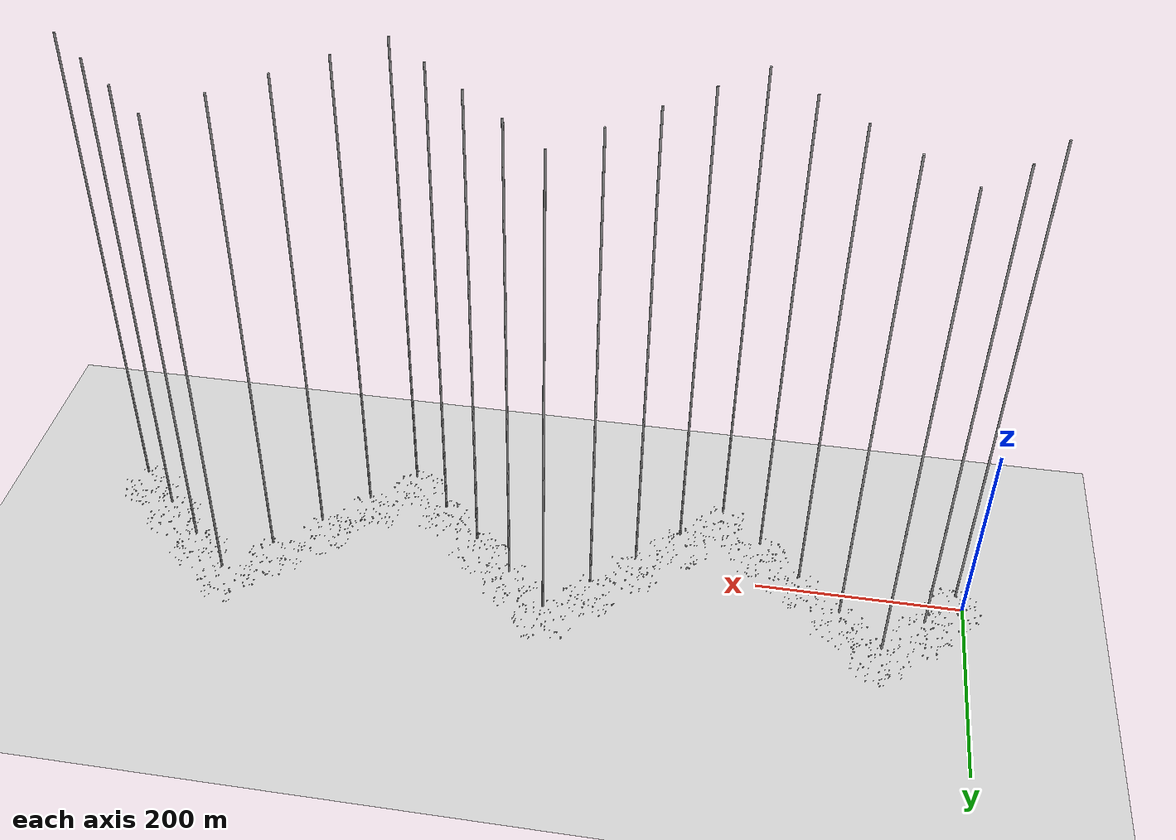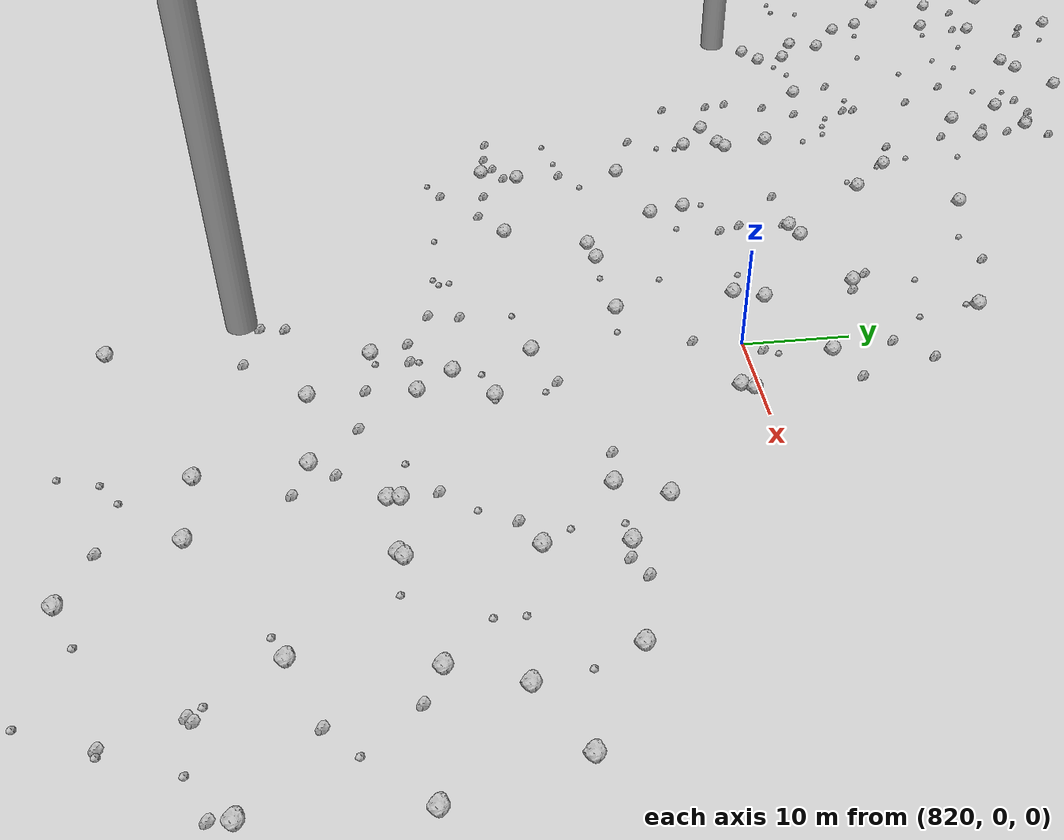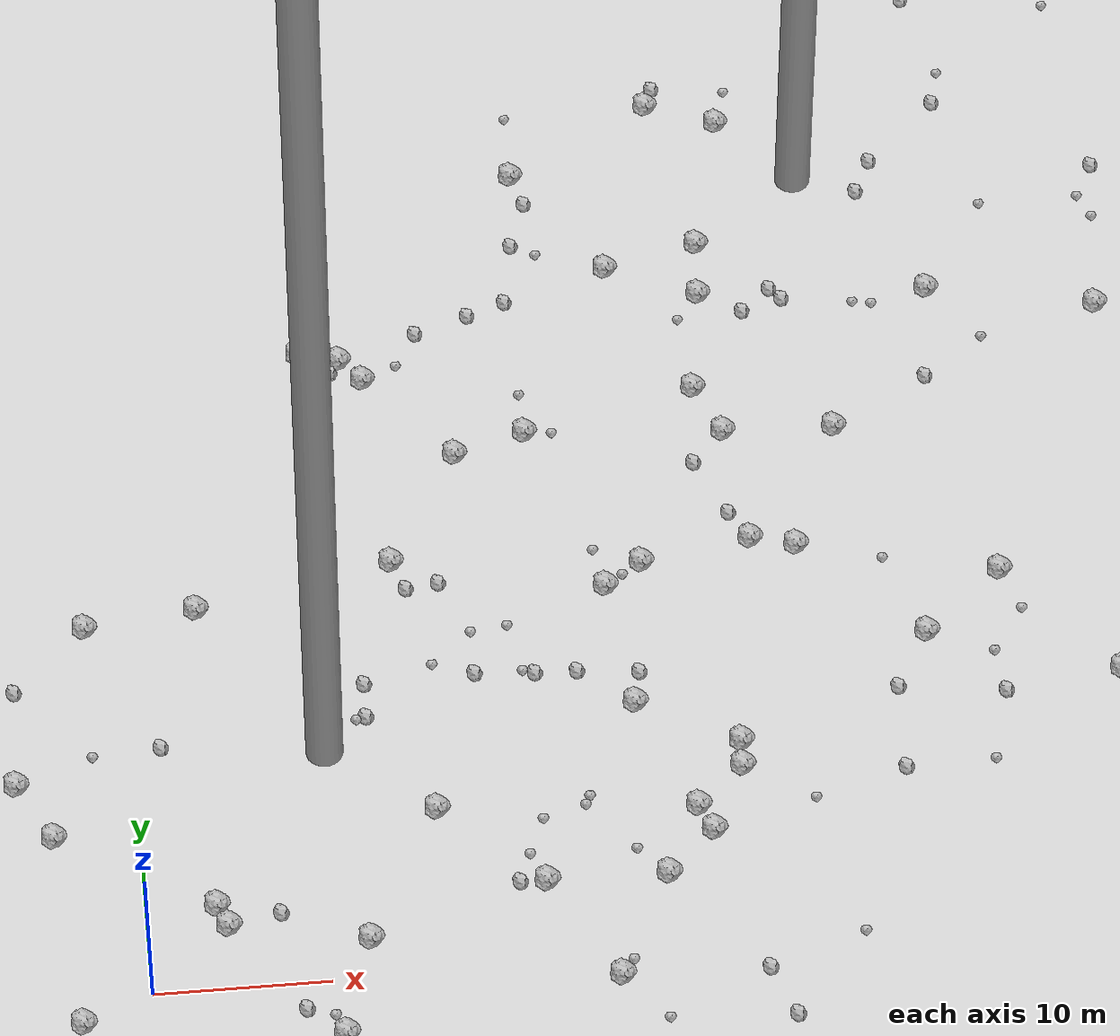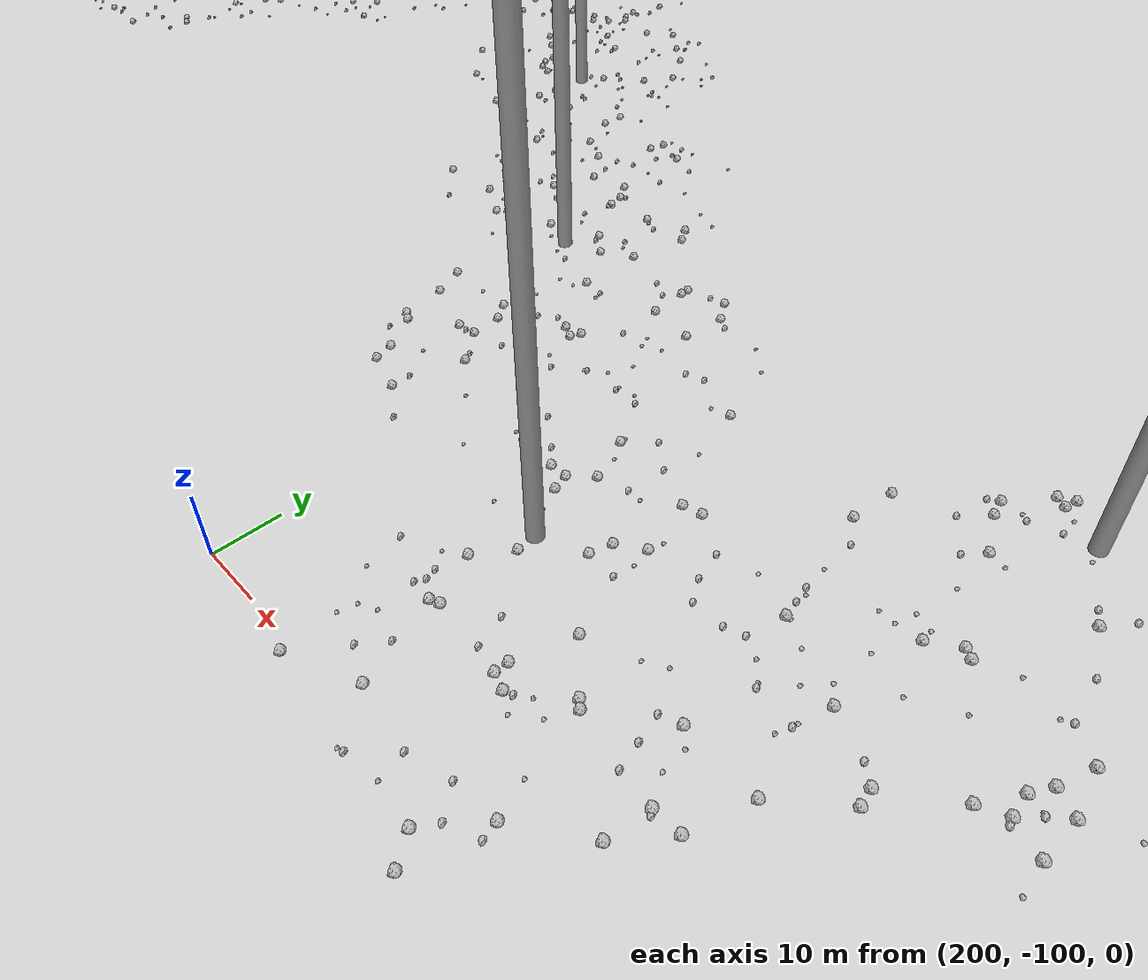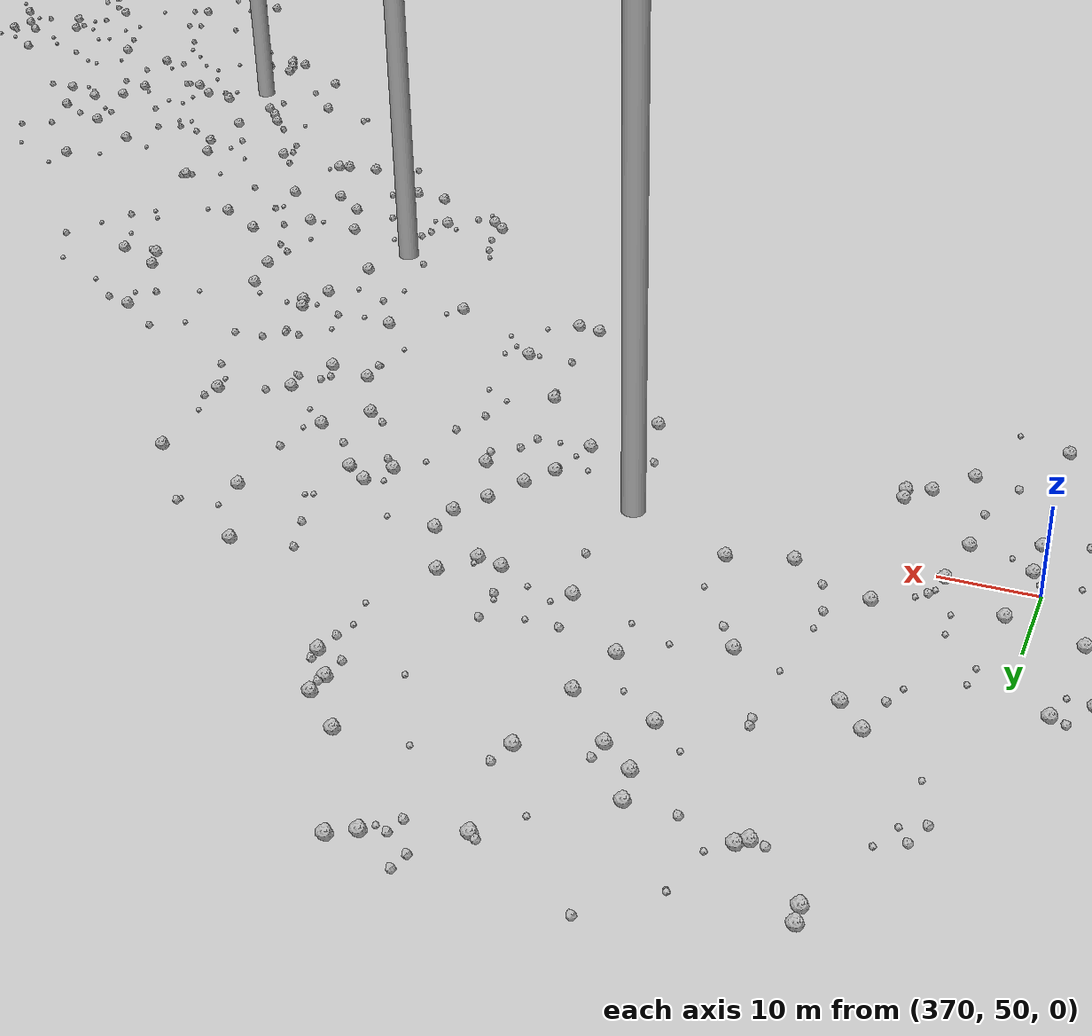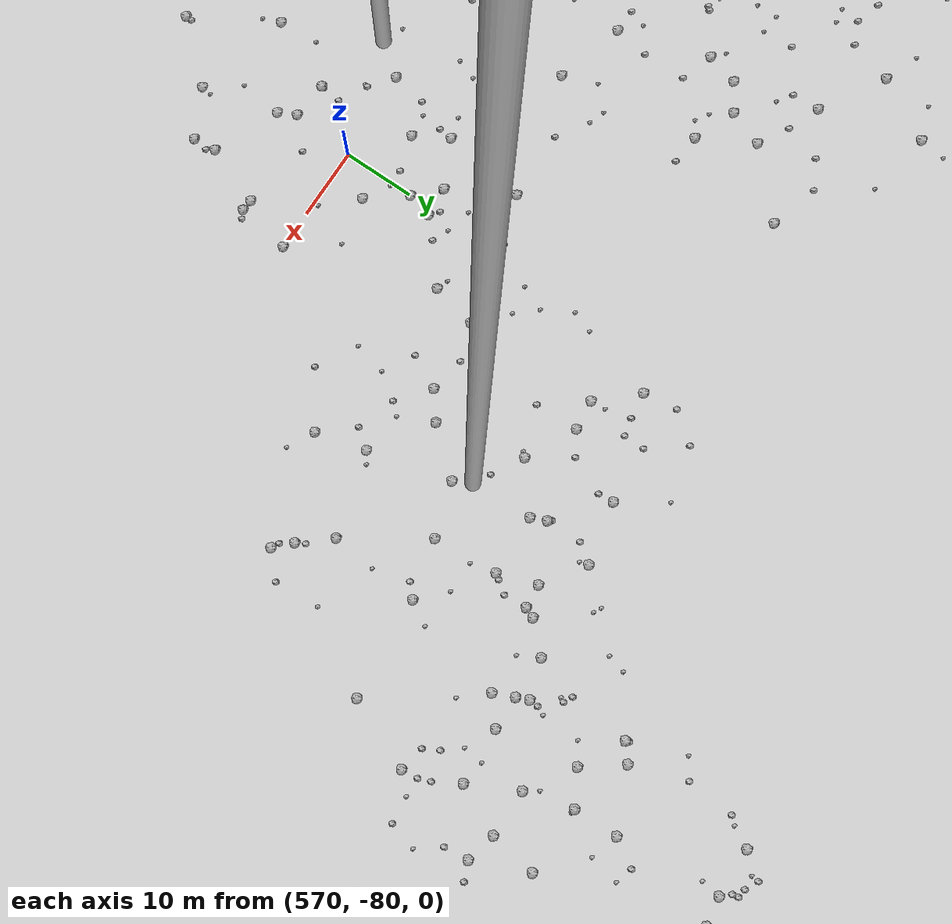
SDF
<sdf version="1.6">
 <world name="default">
  <include><uri>model://custom_ground</uri></include>
  <include><uri>model://sun</uri></include>
  <spherical_coordinates>
   <surface_model>EARTH_WGS84</surface_model>
   <latitude_deg>38.161479</latitude_deg>
   <longitude_deg>-122.454630</longitude_deg>
   <elevation>488.0</elevation>
   <heading_deg>90</heading_deg>
  </spherical_coordinates>
  <model name="rock1_0_0">
   <include><uri>model://rock1</uri><pose>3.9710430038716744 5.708556356414533 0.5 0 0 0</pose></include>
  </model>
  <model name="rock1_0_1">
   <include><uri>model://rock1</uri><pose>16.853954700211887 11.476560595513298 0.5 0 0 0</pose></include>
  </model>
  <model name="rock1_0_2">
   <include><uri>model://rock1</uri><pose>4.140596245764293 27.648088891068497 0.5 0 0 0</pose></include>
  </model>
  <model name="rock1_0_3">
   <include><uri>model://rock1</uri><pose>-6.863370384733212 15.37672874043507 0.5 0 0 0</pose></include>
  </model>
  <model name="rock1_0_4">
   <include><uri>model://rock1</uri><pose>34.6401848849878 14.838353331355755 0.5 0 0 0</pose></include>
  </model>
  <model name="rock1_0_5">
   <include><uri>model://rock1</uri><pose>4.551018157640673 4.199312477890359 0.5 0 0 0</pose></include>
  </model>
  <model name="rock1_0_6">
   <include><uri>model://rock1</uri><pose>12.39956541166297 2.5531214280379118 0.5 0 0 0</pose></include>
  </model>
  <model name="rock1_0_7">
   <include><uri>model://rock1</uri><pose>4.665444129446396 -18.346587485605347 0.5 0 0 0</pose></include>
  </model>
  <model name="rock1_0_8">
   <include><uri>model://rock1</uri><pose>31.672646030934054 10.32085906364636 0.5 0 0 0</pose></include>
  </model>
  <model name="rock1_0_9">
   <include><uri>model://rock1</uri><pose>-2.3947381075441463 26.795589316990103 0.5 0 0 0</pose></include>
  </model>
  <model name="rock1_0_10">
   <include><uri>model://rock1</uri><pose>-11.617834893001024 7.029788933469938 0.5 0 0 0</pose></include>
  </model>
  <model name="rock1_0_11">
   <include><uri>model://rock1</uri><pose>-3.8834087075911796 -1.905886329202989 0.5 0 0 0</pose></include>
  </model>
  <model name="rock1_0_12">
   <include><uri>model://rock1</uri><pose>20.339408433734377 -27.08605104297686 0.5 0 0 0</pose></include>
  </model>
  <model name="rock1_0_13">
   <include><uri>model://rock1</uri><pose>1.050543605518584 -15.246045461044428 0.5 0 0 0</pose></include>
  </model>
  <model name="rock1_0_14">
   <include><uri>model://rock1</uri><pose>7.458846895543655 -26.254186438806133 0.5 0 0 0</pose></include>
  </model>
  <model name="rock1_0_15">
   <include><uri>model://rock1</uri><pose>0.5010604280630808 -7.483004618502601 0.5 0 0 0</pose></include>
  </model>
  <model name="rock1_0_16">
   <include><uri>model://rock1</uri><pose>30.062773463483836 -17.288760991761293 0.5 0 0 0</pose></include>
  </model>
  <model name="rock1_0_17">
   <include><uri>model://rock1</uri><pose>29.475846051713866 5.609228815858401 0.5 0 0 0</pose></include>
  </model>
  <model name="rock1_0_18">
   <include><uri>model://rock1</uri><pose>32.36385191256863 8.500378611252309 0.5 0 0 0</pose></include>
  </model>
  <model name="rock1_0_19">
   <include><uri>model://rock1</uri><pose>-17.400236961657754 3.080138031525962 0.5 0 0 0</pose></include>
  </model>
  <model name="rock1_0_20">
   <include><uri>model://rock1</uri><pose>-12.980300998495157 13.574510438774517 0.5 0 0 0</pose></include>
  </model>
  <model name="rock1_0_21">
   <include><uri>model://rock1</uri><pose>10.630058274808501 18.019633323717223 0.5 0 0 0</pose></include>
  </model>
  <model name="rock1_0_22">
   <include><uri>model://rock1</uri><pose>26.127659771703 -1.3022472675640948 0.5 0 0 0</pose></include>
  </model>
  <model name="rock1_0_23">
   <include><uri>model://rock1</uri><pose>-4.9110949767763135 11.382870153896661 0.5 0 0 0</pose></include>
  </model>
  <model name="rock1_0_24">
   <include><uri>model://rock1</uri><pose>10.540440854423842 -3.9090267721535845 0.5 0 0 0</pose></include>
  </model>
  <model name="rock1_0_25">
   <include><uri>model://rock1</uri><pose>27.1817599159195 -15.842789965667468 0.5 0 0 0</pose></include>
  </model>
  <model name="rock1_0_26">
   <include><uri>model://rock1</uri><pose>22.588441810417102 5.716959018102472 0.5 0 0 0</pose></include>
  </model>
  <model name="rock2_0_0">
   <include><uri>model://rock2</uri><pose>14.17177862590539 -18.133046584436627 0.3 0 0 0</pose></include>
  </model>
  <model name="rock2_0_1">
   <include><uri>model://rock2</uri><pose>13.42217944973116 21.14571390845805 0.3 0 0 0</pose></include>
  </model>
  <model name="rock2_0_2">
   <include><uri>model://rock2</uri><pose>-12.416969177669534 -7.702581743335294 0.3 0 0 0</pose></include>
  </model>
  <model name="rock2_0_3">
   <include><uri>model://rock2</uri><pose>8.450667540446663 -1.9514050008015076 0.3 0 0 0</pose></include>
  </model>
  <model name="rock2_0_4">
   <include><uri>model://rock2</uri><pose>7.491199561298071 4.912482335820208 0.3 0 0 0</pose></include>
  </model>
  <model name="rock2_0_5">
   <include><uri>model://rock2</uri><pose>9.223248350062889 -24.505348295275205 0.3 0 0 0</pose></include>
  </model>
  <model name="rock2_0_6">
   <include><uri>model://rock2</uri><pose>30.132064198689577 -21.84516140750618 0.3 0 0 0</pose></include>
  </model>
  <model name="rock2_0_7">
   <include><uri>model://rock2</uri><pose>-14.923493824025783 14.268268617060649 0.3 0 0 0</pose></include>
  </model>
  <model name="rock2_0_8">
   <include><uri>model://rock2</uri><pose>18.33808117084419 28.447148316543384 0.3 0 0 0</pose></include>
  </model>
  <model name="rock2_0_9">
   <include><uri>model://rock2</uri><pose>11.153759801812939 -25.93612753024732 0.3 0 0 0</pose></include>
  </model>
  <model name="rock2_0_10">
   <include><uri>model://rock2</uri><pose>-8.346750406137453 -17.83372195511092 0.3 0 0 0</pose></include>
  </model>
  <model name="rock2_0_11">
   <include><uri>model://rock2</uri><pose>21.98100304411323 -19.907268991670943 0.3 0 0 0</pose></include>
  </model>
  <model name="rock2_0_12">
   <include><uri>model://rock2</uri><pose>35.473320851581065 -4.864078170385675 0.3 0 0 0</pose></include>
  </model>
  <model name="rock2_0_13">
   <include><uri>model://rock2</uri><pose>13.344942034801221 18.707670051641536 0.3 0 0 0</pose></include>
  </model>
  <model name="rock2_0_14">
   <include><uri>model://rock2</uri><pose>-6.720544227832816 22.396559598043908 0.3 0 0 0</pose></include>
  </model>
  <model name="rock2_0_15">
   <include><uri>model://rock2</uri><pose>23.31315829736814 21.06685442302659 0.3 0 0 0</pose></include>
  </model>
  <model name="rock2_0_16">
   <include><uri>model://rock2</uri><pose>-12.72127784259899 -3.2245156025583874 0.3 0 0 0</pose></include>
  </model>
  <model name="rock2_0_17">
   <include><uri>model://rock2</uri><pose>19.84453679418509 21.38116795033371 0.3 0 0 0</pose></include>
  </model>
  <model name="rock2_0_18">
   <include><uri>model://rock2</uri><pose>34.34625587164329 -1.4907859225286195 0.3 0 0 0</pose></include>
  </model>
  <model name="rock2_0_19">
   <include><uri>model://rock2</uri><pose>-2.0320483852749085 -19.958127814743115 0.3 0 0 0</pose></include>
  </model>
  <model name="rock2_0_20">
   <include><uri>model://rock2</uri><pose>17.84705491074436 -22.076821857598517 0.3 0 0 0</pose></include>
  </model>
  <model name="rock2_0_21">
   <include><uri>model://rock2</uri><pose>30.530383042893952 -11.362448575123722 0.3 0 0 0</pose></include>
  </model>
  <model name="rock2_0_22">
   <include><uri>model://rock2</uri><pose>-4.6670138499545395 -10.467048133621269 0.3 0 0 0</pose></include>
  </model>
  <model name="rock2_0_23">
   <include><uri>model://rock2</uri><pose>3.235107491457555 -11.267621733446092 0.3 0 0 0</pose></include>
  </model>
  <model name="rock2_0_24">
   <include><uri>model://rock2</uri><pose>21.043753553426534 5.858102582804662 0.3 0 0 0</pose></include>
  </model>
  <model name="rock2_0_25">
   <include><uri>model://rock2</uri><pose>1.4763846255794206 17.518639206182996 0.3 0 0 0</pose></include>
  </model>
  <model name="rock2_0_26">
   <include><uri>model://rock2</uri><pose>-2.47174586648773 -14.952047206337431 0.3 0 0 0</pose></include>
  </model>
  <model name="rock3_0_0">
   <include><uri>model://rock3</uri><pose>26.841052948203327 -0.19605645728805499 0.2 0 0 0</pose></include>
  </model>
  <model name="rock3_0_1">
   <include><uri>model://rock3</uri><pose>12.448243242295277 -11.852728842782028 0.2 0 0 0</pose></include>
  </model>
  <model name="rock3_0_2">
   <include><uri>model://rock3</uri><pose>-14.074828372952513 -15.070418107042446 0.2 0 0 0</pose></include>
  </model>
  <model name="rock3_0_3">
   <include><uri>model://rock3</uri><pose>12.777112462095431 18.556736498701042 0.2 0 0 0</pose></include>
  </model>
  <model name="rock3_0_4">
   <include><uri>model://rock3</uri><pose>-17.27517534544655 3.936262496482847 0.2 0 0 0</pose></include>
  </model>
  <model name="rock3_0_5">
   <include><uri>model://rock3</uri><pose>-2.4567649797748246 17.203791498481927 0.2 0 0 0</pose></include>
  </model>
  <model name="rock3_0_6">
   <include><uri>model://rock3</uri><pose>-2.5278049229623214 -16.471382188979035 0.2 0 0 0</pose></include>
  </model>
  <model name="rock3_0_7">
   <include><uri>model://rock3</uri><pose>-7.426001958425708 -7.9821137340854555 0.2 0 0 0</pose></include>
  </model>
  <model name="rock3_0_8">
   <include><uri>model://rock3</uri><pose>1.905804384336804 -9.976099762248005 0.2 0 0 0</pose></include>
  </model>
  <model name="rock3_0_9">
   <include><uri>model://rock3</uri><pose>22.6273192991128 21.33963846714724 0.2 0 0 0</pose></include>
  </model>
  <model name="rock3_0_10">
   <include><uri>model://rock3</uri><pose>31.03053128345841 -10.13774282040994 0.2 0 0 0</pose></include>
  </model>
  <model name="rock3_0_11">
   <include><uri>model://rock3</uri><pose>21.784031945137357 7.812988173867353 0.2 0 0 0</pose></include>
  </model>
  <model name="rock3_0_12">
   <include><uri>model://rock3</uri><pose>27.840687331210617 7.638257549597746 0.2 0 0 0</pose></include>
  </model>
  <model name="rock3_0_13">
   <include><uri>model://rock3</uri><pose>28.422209865122518 -4.431575925745264 0.2 0 0 0</pose></include>
  </model>
  <model name="rock3_0_14">
   <include><uri>model://rock3</uri><pose>-2.1077354877375534 -27.27715964628306 0.2 0 0 0</pose></include>
  </model>
  <model name="rock3_0_15">
   <include><uri>model://rock3</uri><pose>17.452239157688993 22.29035493907012 0.2 0 0 0</pose></include>
  </model>
  <model name="rock3_0_16">
   <include><uri>model://rock3</uri><pose>-17.16007772316537 -9.706231376230186 0.2 0 0 0</pose></include>
  </model>
  <model name="rock3_0_17">
   <include><uri>model://rock3</uri><pose>4.562321703879068 -28.749701306019894 0.2 0 0 0</pose></include>
  </model>
  <model name="rock3_0_18">
   <include><uri>model://rock3</uri><pose>-8.210339601052258 -5.096854722537611 0.2 0 0 0</pose></include>
  </model>
  <model name="rock3_0_19">
   <include><uri>model://rock3</uri><pose>18.965157754198806 -26.469498595599703 0.2 0 0 0</pose></include>
  </model>
  <model name="rock3_0_20">
   <include><uri>model://rock3</uri><pose>22.77253527891898 10.297052813368921 0.2 0 0 0</pose></include>
  </model>
  <model name="rock3_0_21">
   <include><uri>model://rock3</uri><pose>25.279261495413095 11.08008596239884 0.2 0 0 0</pose></include>
  </model>
  <model name="rock3_0_22">
   <include><uri>model://rock3</uri><pose>22.052872830681494 24.857238066510767 0.2 0 0 0</pose></include>
  </model>
  <model name="rock3_0_23">
   <include><uri>model://rock3</uri><pose>25.573313429574938 11.693596549083281 0.2 0 0 0</pose></include>
  </model>
  <model name="rock3_0_24">
   <include><uri>model://rock3</uri><pose>39.9710930422142 0.5687715343288495 0.2 0 0 0</pose></include>
  </model>
  <model name="rock3_0_25">
   <include><uri>model://rock3</uri><pose>10.000373501234808 -2.4962546684213507 0.2 0 0 0</pose></include>
  </model>
  <model name="rock3_0_26">
   <include><uri>model://rock3</uri><pose>0.09741587397869722 -26.245275789831172 0.2 0 0 0</pose></include>
  </model>
  <model name="rock1_1_0">
   <include><uri>model://rock1</uri><pose>39.547599610841445 29.366199813897115 0.5 0 0 0</pose></include>
  </model>
  <model name="rock1_1_1">
   <include><uri>model://rock1</uri><pose>30.656001330001857 52.655506444672625 0.5 0 0 0</pose></include>
  </model>
  <model name="rock1_1_2">
   <include><uri>model://rock1</uri><pose>28.89154984261577 18.24935548848415 0.5 0 0 0</pose></include>
  </model>
  <model name="rock1_1_3">
   <include><uri>model://rock1</uri><pose>13.929408264534294 46.57723159860972 0.5 0 0 0</pose></include>
  </model>
  <model name="rock1_1_4">
   <include><uri>model://rock1</uri><pose>36.29132265885297 38.72036125403501 0.5 0 0 0</pose></include>
  </model>
  <model name="rock1_1_5">
   <include><uri>model://rock1</uri><pose>36.063590201862525 50.02675545421989 0.5 0 0 0</pose></include>
  </model>
  <model name="rock1_1_6">
   <include><uri>model://rock1</uri><pose>24.5067401689588 39.72169552507738 0.5 0 0 0</pose></include>
  </model>
  <model name="rock1_1_7">
   <include><uri>model://rock1</uri><pose>20.208310804242057 38.356251437919305 0.5 0 0 0</pose></include>
  </model>
  <model name="rock1_1_8">
   <include><uri>model://rock1</uri><pose>36.928037307213586 30.127084482556267 0.5 0 0 0</pose></include>
  </model>
  <model name="rock1_1_9">
   <include><uri>model://rock1</uri><pose>36.410750928904015 54.18865630098424 0.5 0 0 0</pose></include>
  </model>
  <model name="rock1_1_10">
   <include><uri>model://rock1</uri><pose>46.31054173712645 21.96760135033954 0.5 0 0 0</pose></include>
  </model>
  <model name="rock1_1_11">
   <include><uri>model://rock1</uri><pose>42.91758014828316 38.45362313363333 0.5 0 0 0</pose></include>
  </model>
  <model name="rock1_1_12">
   <include><uri>model://rock1</uri><pose>25.65544986607127 61.0118866264647 0.5 0 0 0</pose></include>
  </model>
  <model name="rock1_1_13">
   <include><uri>model://rock1</uri><pose>34.90200102939843 42.368385818752174 0.5 0 0 0</pose></include>
  </model>
  <model name="rock1_1_14">
   <include><uri>model://rock1</uri><pose>51.16164543415536 26.296662424014745 0.5 0 0 0</pose></include>
  </model>
  <model name="rock1_1_15">
   <include><uri>model://rock1</uri><pose>34.56622965092178 66.2947403752197 0.5 0 0 0</pose></include>
  </model>
  <model name="rock1_1_16">
   <include><uri>model://rock1</uri><pose>67.7905659723522 49.584509257915364 0.5 0 0 0</pose></include>
  </model>
  <model name="rock1_1_17">
   <include><uri>model://rock1</uri><pose>49.91336892626199 49.20075572214393 0.5 0 0 0</pose></include>
  </model>
  <model name="rock1_1_18">
   <include><uri>model://rock1</uri><pose>15.75321377492845 30.24582275009395 0.5 0 0 0</pose></include>
  </model>
  <model name="rock1_1_19">
   <include><uri>model://rock1</uri><pose>30.361739144834267 28.863450425999698 0.5 0 0 0</pose></include>
  </model>
  <model name="rock1_1_20">
   <include><uri>model://rock1</uri><pose>15.228812092771234 44.858833762034145 0.5 0 0 0</pose></include>
  </model>
  <model name="rock1_1_21">
   <include><uri>model://rock1</uri><pose>38.77521010312965 64.4273382984022 0.5 0 0 0</pose></include>
  </model>
  <model name="rock1_1_22">
   <include><uri>model://rock1</uri><pose>34.50001272250752 12.995073589864266 0.5 0 0 0</pose></include>
  </model>
  <model name="rock1_1_23">
   <include><uri>model://rock1</uri><pose>28.08351390696014 27.241275348210966 0.5 0 0 0</pose></include>
  </model>
  <model name="rock1_1_24">
   <include><uri>model://rock1</uri><pose>59.941849288575995 46.96876659139655 0.5 0 0 0</pose></include>
  </model>
  <model name="rock1_1_25">
   <include><uri>model://rock1</uri><pose>11.51362191039433 47.26180825439106 0.5 0 0 0</pose></include>
  </model>
  <model name="rock1_1_26">
   <include><uri>model://rock1</uri><pose>57.2005188777916 18.125899335187285 0.5 0 0 0</pose></include>
  </model>
  <model name="rock2_1_0">
   <include><uri>model://rock2</uri><pose>13.292251106342643 45.70174819587879 0.3 0 0 0</pose></include>
  </model>
  <model name="rock2_1_1">
   <include><uri>model://rock2</uri><pose>16.41927193023514 28.199535379328232 0.3 0 0 0</pose></include>
  </model>
  <model name="rock2_1_2">
   <include><uri>model://rock2</uri><pose>25.75027287169112 20.98839532305013 0.3 0 0 0</pose></include>
  </model>
  <model name="rock2_1_3">
   <include><uri>model://rock2</uri><pose>11.788249402398176 39.42064110249721 0.3 0 0 0</pose></include>
  </model>
  <model name="rock2_1_4">
   <include><uri>model://rock2</uri><pose>41.04436082922372 49.27085116524356 0.3 0 0 0</pose></include>
  </model>
  <model name="rock2_1_5">
   <include><uri>model://rock2</uri><pose>48.863972515303374 42.10969446801326 0.3 0 0 0</pose></include>
  </model>
  <model name="rock2_1_6">
   <include><uri>model://rock2</uri><pose>61.4292023982925 58.69019543257895 0.3 0 0 0</pose></include>
  </model>
  <model name="rock2_1_7">
   <include><uri>model://rock2</uri><pose>44.09072551587189 18.06100786591889 0.3 0 0 0</pose></include>
  </model>
  <model name="rock2_1_8">
   <include><uri>model://rock2</uri><pose>66.51732668189592 36.55063388929291 0.3 0 0 0</pose></include>
  </model>
  <model name="rock2_1_9">
   <include><uri>model://rock2</uri><pose>25.086173103888285 55.177762365306634 0.3 0 0 0</pose></include>
  </model>
  <model name="rock2_1_10">
   <include><uri>model://rock2</uri><pose>35.852620022878085 32.319981803219235 0.3 0 0 0</pose></include>
  </model>
  <model name="rock2_1_11">
   <include><uri>model://rock2</uri><pose>18.656348708565922 48.418298593368554 0.3 0 0 0</pose></include>
  </model>
  <model name="rock2_1_12">
   <include><uri>model://rock2</uri><pose>29.339017066696304 20.59094587062365 0.3 0 0 0</pose></include>
  </model>
  <model name="rock2_1_13">
   <include><uri>model://rock2</uri><pose>47.82710251100298 60.33041098741931 0.3 0 0 0</pose></include>
  </model>
  <model name="rock2_1_14">
   <include><uri>model://rock2</uri><pose>46.67583761541484 57.82531820704848 0.3 0 0 0</pose></include>
  </model>
  <model name="rock2_1_15">
   <include><uri>model://rock2</uri><pose>21.923855036376516 49.60465684509001 0.3 0 0 0</pose></include>
  </model>
  <model name="rock2_1_16">
   <include><uri>model://rock2</uri><pose>34.24619019837364 36.45325403333308 0.3 0 0 0</pose></include>
  </model>
  <model name="rock2_1_17">
   <include><uri>model://rock2</uri><pose>60.9950310088027 31.26149176108948 0.3 0 0 0</pose></include>
  </model>
  <model name="rock2_1_18">
   <include><uri>model://rock2</uri><pose>26.223961714219172 58.66970979453294 0.3 0 0 0</pose></include>
  </model>
  <model name="rock2_1_19">
   <include><uri>model://rock2</uri><pose>35.10625450430919 67.84336171953169 0.3 0 0 0</pose></include>
  </model>
  <model name="rock2_1_20">
   <include><uri>model://rock2</uri><pose>52.37507367312402 65.01545308121639 0.3 0 0 0</pose></include>
  </model>
  <model name="rock2_1_21">
   <include><uri>model://rock2</uri><pose>67.88032416669735 49.22423792427145 0.3 0 0 0</pose></include>
  </model>
  <model name="rock2_1_22">
   <include><uri>model://rock2</uri><pose>40.38976390749001 50.14294289609707 0.3 0 0 0</pose></include>
  </model>
  <model name="rock2_1_23">
   <include><uri>model://rock2</uri><pose>43.77690020559252 12.094133281979882 0.3 0 0 0</pose></include>
  </model>
  <model name="rock2_1_24">
   <include><uri>model://rock2</uri><pose>24.262145896781277 50.51913913730683 0.3 0 0 0</pose></include>
  </model>
  <model name="rock2_1_25">
   <include><uri>model://rock2</uri><pose>50.27553933634518 17.22312568456135 0.3 0 0 0</pose></include>
  </model>
  <model name="rock2_1_26">
   <include><uri>model://rock2</uri><pose>38.54962936767228 48.45304416384973 0.3 0 0 0</pose></include>
  </model>
  <model name="rock3_1_0">
   <include><uri>model://rock3</uri><pose>29.141009361966347 28.118759949231627 0.2 0 0 0</pose></include>
  </model>
  <model name="rock3_1_1">
   <include><uri>model://rock3</uri><pose>54.10240438578363 56.08780319087682 0.2 0 0 0</pose></include>
  </model>
  <model name="rock3_1_2">
   <include><uri>model://rock3</uri><pose>27.60353310793924 30.169774767745242 0.2 0 0 0</pose></include>
  </model>
  <model name="rock3_1_3">
   <include><uri>model://rock3</uri><pose>19.89543825844218 24.5500420801388 0.2 0 0 0</pose></include>
  </model>
  <model name="rock3_1_4">
   <include><uri>model://rock3</uri><pose>38.3880939595586 10.366638339231006 0.2 0 0 0</pose></include>
  </model>
  <model name="rock3_1_5">
   <include><uri>model://rock3</uri><pose>60.212549687143856 56.16783111272029 0.2 0 0 0</pose></include>
  </model>
  <model name="rock3_1_6">
   <include><uri>model://rock3</uri><pose>52.04170779829864 23.340750253497678 0.2 0 0 0</pose></include>
  </model>
  <model name="rock3_1_7">
   <include><uri>model://rock3</uri><pose>20.403495995317538 38.865482210531425 0.2 0 0 0</pose></include>
  </model>
  <model name="rock3_1_8">
   <include><uri>model://rock3</uri><pose>44.45150459345438 27.960907265228 0.2 0 0 0</pose></include>
  </model>
  <model name="rock3_1_9">
   <include><uri>model://rock3</uri><pose>61.34486747980786 19.394475555884682 0.2 0 0 0</pose></include>
  </model>
  <model name="rock3_1_10">
   <include><uri>model://rock3</uri><pose>39.56809408194495 67.20272596764028 0.2 0 0 0</pose></include>
  </model>
  <model name="rock3_1_11">
   <include><uri>model://rock3</uri><pose>26.536134415610192 54.33768842430592 0.2 0 0 0</pose></include>
  </model>
  <model name="rock3_1_12">
   <include><uri>model://rock3</uri><pose>17.28730888559104 45.93427058165784 0.2 0 0 0</pose></include>
  </model>
  <model name="rock3_1_13">
   <include><uri>model://rock3</uri><pose>12.026599985400486 30.50021607162686 0.2 0 0 0</pose></include>
  </model>
  <model name="rock3_1_14">
   <include><uri>model://rock3</uri><pose>25.730131436146237 66.11018263574822 0.2 0 0 0</pose></include>
  </model>
  <model name="rock3_1_15">
   <include><uri>model://rock3</uri><pose>48.97972649861404 12.242236112341738 0.2 0 0 0</pose></include>
  </model>
  <model name="rock3_1_16">
   <include><uri>model://rock3</uri><pose>24.452085531757003 42.88551783571335 0.2 0 0 0</pose></include>
  </model>
  <model name="rock3_1_17">
   <include><uri>model://rock3</uri><pose>62.8287674656184 36.727816001284054 0.2 0 0 0</pose></include>
  </model>
  <model name="rock3_1_18">
   <include><uri>model://rock3</uri><pose>68.14202710122757 42.70216331787328 0.2 0 0 0</pose></include>
  </model>
  <model name="rock3_1_19">
   <include><uri>model://rock3</uri><pose>45.31954236650388 48.606020832283946 0.2 0 0 0</pose></include>
  </model>
  <model name="rock3_1_20">
   <include><uri>model://rock3</uri><pose>52.6905955760433 45.02117458255658 0.2 0 0 0</pose></include>
  </model>
  <model name="rock3_1_21">
   <include><uri>model://rock3</uri><pose>60.85156720237278 54.39462924811085 0.2 0 0 0</pose></include>
  </model>
  <model name="rock3_1_22">
   <include><uri>model://rock3</uri><pose>26.103036768977216 39.644628485145745 0.2 0 0 0</pose></include>
  </model>
  <model name="rock3_1_23">
   <include><uri>model://rock3</uri><pose>60.85448718293174 22.071985627987743 0.2 0 0 0</pose></include>
  </model>
  <model name="rock3_1_24">
   <include><uri>model://rock3</uri><pose>50.02021531631828 20.260379684964583 0.2 0 0 0</pose></include>
  </model>
  <model name="rock3_1_25">
   <include><uri>model://rock3</uri><pose>46.44304594435444 48.39412279528173 0.2 0 0 0</pose></include>
  </model>
  <model name="rock3_1_26">
   <include><uri>model://rock3</uri><pose>34.60671079090339 48.104000891340405 0.2 0 0 0</pose></include>
  </model>
  <model name="rock1_2_0">
   <include><uri>model://rock1</uri><pose>70.24486673222864 88.0337994291963 0.5 0 0 0</pose></include>
  </model>
  <model name="rock1_2_1">
   <include><uri>model://rock1</uri><pose>87.48596564453584 56.37542297130342 0.5 0 0 0</pose></include>
  </model>
  <model name="rock1_2_2">
   <include><uri>model://rock1</uri><pose>89.22649121975255 73.56675198549561 0.5 0 0 0</pose></include>
  </model>
  <model name="rock1_2_3">
   <include><uri>model://rock1</uri><pose>105.53491507973834 65.0004295077046 0.5 0 0 0</pose></include>
  </model>
  <model name="rock1_2_4">
   <include><uri>model://rock1</uri><pose>65.68586360123854 64.61506510829281 0.5 0 0 0</pose></include>
  </model>
  <model name="rock1_2_5">
   <include><uri>model://rock1</uri><pose>104.64801245808032 78.5028275605944 0.5 0 0 0</pose></include>
  </model>
  <model name="rock1_2_6">
   <include><uri>model://rock1</uri><pose>69.82030331920697 93.61117676125005 0.5 0 0 0</pose></include>
  </model>
  <model name="rock1_2_7">
   <include><uri>model://rock1</uri><pose>96.97615936818354 84.62001212828864 0.5 0 0 0</pose></include>
  </model>
  <model name="rock1_2_8">
   <include><uri>model://rock1</uri><pose>97.94841251956773 61.292294591127636 0.5 0 0 0</pose></include>
  </model>
  <model name="rock1_2_9">
   <include><uri>model://rock1</uri><pose>78.2593233403162 58.246486499676706 0.5 0 0 0</pose></include>
  </model>
  <model name="rock1_2_10">
   <include><uri>model://rock1</uri><pose>71.66606471396663 93.25741419563059 0.5 0 0 0</pose></include>
  </model>
  <model name="rock1_2_11">
   <include><uri>model://rock1</uri><pose>82.30481893540795 50.50826938168194 0.5 0 0 0</pose></include>
  </model>
  <model name="rock1_2_12">
   <include><uri>model://rock1</uri><pose>103.07975485657064 61.49445307743291 0.5 0 0 0</pose></include>
  </model>
  <model name="rock1_2_13">
   <include><uri>model://rock1</uri><pose>57.115768895879285 81.98426158407699 0.5 0 0 0</pose></include>
  </model>
  <model name="rock1_2_14">
   <include><uri>model://rock1</uri><pose>78.53123297169813 70.07345353190469 0.5 0 0 0</pose></include>
  </model>
  <model name="rock1_2_15">
   <include><uri>model://rock1</uri><pose>94.08806094319723 88.17231198953755 0.5 0 0 0</pose></include>
  </model>
  <model name="rock1_2_16">
   <include><uri>model://rock1</uri><pose>76.7900143049579 83.00357786327999 0.5 0 0 0</pose></include>
  </model>
  <model name="rock1_2_17">
   <include><uri>model://rock1</uri><pose>78.72622867402646 109.10418390898093 0.5 0 0 0</pose></include>
  </model>
  <model name="rock1_2_18">
   <include><uri>model://rock1</uri><pose>91.49853477520169 59.52136926561016 0.5 0 0 0</pose></include>
  </model>
  <model name="rock1_2_19">
   <include><uri>model://rock1</uri><pose>92.14693297203463 104.72845092726658 0.5 0 0 0</pose></include>
  </model>
  <model name="rock1_2_20">
   <include><uri>model://rock1</uri><pose>83.34478479646035 74.38832514822204 0.5 0 0 0</pose></include>
  </model>
  <model name="rock1_2_21">
   <include><uri>model://rock1</uri><pose>103.74325877542857 66.95054760867475 0.5 0 0 0</pose></include>
  </model>
  <model name="rock1_2_22">
   <include><uri>model://rock1</uri><pose>71.42480966996052 63.497510341736096 0.5 0 0 0</pose></include>
  </model>
  <model name="rock1_2_23">
   <include><uri>model://rock1</uri><pose>102.82039981670269 70.48135374302655 0.5 0 0 0</pose></include>
  </model>
  <model name="rock1_2_24">
   <include><uri>model://rock1</uri><pose>78.90779634103862 101.23699033584198 0.5 0 0 0</pose></include>
  </model>
  <model name="rock1_2_25">
   <include><uri>model://rock1</uri><pose>79.69365656326107 91.91403491440346 0.5 0 0 0</pose></include>
  </model>
  <model name="rock1_2_26">
   <include><uri>model://rock1</uri><pose>70.20164957173414 95.83017636498388 0.5 0 0 0</pose></include>
  </model>
  <model name="rock2_2_0">
   <include><uri>model://rock2</uri><pose>84.50132554203387 103.40802229256846 0.3 0 0 0</pose></include>
  </model>
  <model name="rock2_2_1">
   <include><uri>model://rock2</uri><pose>62.46186983649714 76.08383370527375 0.3 0 0 0</pose></include>
  </model>
  <model name="rock2_2_2">
   <include><uri>model://rock2</uri><pose>90.24566149203405 95.6376021674849 0.3 0 0 0</pose></include>
  </model>
  <model name="rock2_2_3">
   <include><uri>model://rock2</uri><pose>87.69747596688045 52.77338242170023 0.3 0 0 0</pose></include>
  </model>
  <model name="rock2_2_4">
   <include><uri>model://rock2</uri><pose>105.2878346660566 91.28244135079993 0.3 0 0 0</pose></include>
  </model>
  <model name="rock2_2_5">
   <include><uri>model://rock2</uri><pose>83.54872282081666 70.66642093288749 0.3 0 0 0</pose></include>
  </model>
  <model name="rock2_2_6">
   <include><uri>model://rock2</uri><pose>78.98639396306955 95.41081435196787 0.3 0 0 0</pose></include>
  </model>
  <model name="rock2_2_7">
   <include><uri>model://rock2</uri><pose>92.34053550160255 97.75421648169956 0.3 0 0 0</pose></include>
  </model>
  <model name="rock2_2_8">
   <include><uri>model://rock2</uri><pose>65.23929466579837 60.751076390705165 0.3 0 0 0</pose></include>
  </model>
  <model name="rock2_2_9">
   <include><uri>model://rock2</uri><pose>72.82460024124774 80.32566370768193 0.3 0 0 0</pose></include>
  </model>
  <model name="rock2_2_10">
   <include><uri>model://rock2</uri><pose>100.70893028842814 63.078072647384346 0.3 0 0 0</pose></include>
  </model>
  <model name="rock2_2_11">
   <include><uri>model://rock2</uri><pose>81.20231974972513 61.83782862842705 0.3 0 0 0</pose></include>
  </model>
  <model name="rock2_2_12">
   <include><uri>model://rock2</uri><pose>59.3345785780991 84.87327662264849 0.3 0 0 0</pose></include>
  </model>
  <model name="rock2_2_13">
   <include><uri>model://rock2</uri><pose>80.04101025666522 105.80282633404782 0.3 0 0 0</pose></include>
  </model>
  <model name="rock2_2_14">
   <include><uri>model://rock2</uri><pose>104.41099716663649 70.52262896738287 0.3 0 0 0</pose></include>
  </model>
  <model name="rock2_2_15">
   <include><uri>model://rock2</uri><pose>51.6483463209574 74.34030716486579 0.3 0 0 0</pose></include>
  </model>
  <model name="rock2_2_16">
   <include><uri>model://rock2</uri><pose>50.08935063391807 79.9129827161634 0.3 0 0 0</pose></include>
  </model>
  <model name="rock2_2_17">
   <include><uri>model://rock2</uri><pose>71.44414463988028 67.81927935050925 0.3 0 0 0</pose></include>
  </model>
  <model name="rock2_2_18">
   <include><uri>model://rock2</uri><pose>74.11489340182722 99.30130592630829 0.3 0 0 0</pose></include>
  </model>
  <model name="rock2_2_19">
   <include><uri>model://rock2</uri><pose>59.03423925740414 95.95930923441429 0.3 0 0 0</pose></include>
  </model>
  <model name="rock2_2_20">
   <include><uri>model://rock2</uri><pose>75.83725083984854 107.25764383934708 0.3 0 0 0</pose></include>
  </model>
  <model name="rock2_2_21">
   <include><uri>model://rock2</uri><pose>77.42187298446453 109.25574791349493 0.3 0 0 0</pose></include>
  </model>
  <model name="rock2_2_22">
   <include><uri>model://rock2</uri><pose>99.39714319857664 92.09845522441256 0.3 0 0 0</pose></include>
  </model>
  <model name="rock2_2_23">
   <include><uri>model://rock2</uri><pose>105.76208215830016 73.70104611707947 0.3 0 0 0</pose></include>
  </model>
  <model name="rock2_2_24">
   <include><uri>model://rock2</uri><pose>68.74557056584128 68.6709800426396 0.3 0 0 0</pose></include>
  </model>
  <model name="rock2_2_25">
   <include><uri>model://rock2</uri><pose>79.597897383484 96.57264918457199 0.3 0 0 0</pose></include>
  </model>
  <model name="rock2_2_26">
   <include><uri>model://rock2</uri><pose>74.10774654956148 88.01780969111006 0.3 0 0 0</pose></include>
  </model>
  <model name="rock3_2_0">
   <include><uri>model://rock3</uri><pose>86.15954754387545 60.257853230724955 0.2 0 0 0</pose></include>
  </model>
  <model name="rock3_2_1">
   <include><uri>model://rock3</uri><pose>86.21891172269402 70.95642455496616 0.2 0 0 0</pose></include>
  </model>
  <model name="rock3_2_2">
   <include><uri>model://rock3</uri><pose>60.47855352113187 72.98168005929433 0.2 0 0 0</pose></include>
  </model>
  <model name="rock3_2_3">
   <include><uri>model://rock3</uri><pose>83.14718523032644 69.57765753909625 0.2 0 0 0</pose></include>
  </model>
  <model name="rock3_2_4">
   <include><uri>model://rock3</uri><pose>53.0487835277051 67.60976164657032 0.2 0 0 0</pose></include>
  </model>
  <model name="rock3_2_5">
   <include><uri>model://rock3</uri><pose>88.66722180258242 62.401453165745195 0.2 0 0 0</pose></include>
  </model>
  <model name="rock3_2_6">
   <include><uri>model://rock3</uri><pose>74.23823029808918 52.19310338215085 0.2 0 0 0</pose></include>
  </model>
  <model name="rock3_2_7">
   <include><uri>model://rock3</uri><pose>61.0232503274505 90.0558008115546 0.2 0 0 0</pose></include>
  </model>
  <model name="rock3_2_8">
   <include><uri>model://rock3</uri><pose>76.7605498826613 99.61857282931962 0.2 0 0 0</pose></include>
  </model>
  <model name="rock3_2_9">
   <include><uri>model://rock3</uri><pose>100.78567989394196 100.37213101653333 0.2 0 0 0</pose></include>
  </model>
  <model name="rock3_2_10">
   <include><uri>model://rock3</uri><pose>71.04986302718619 97.20348155628741 0.2 0 0 0</pose></include>
  </model>
  <model name="rock3_2_11">
   <include><uri>model://rock3</uri><pose>73.46639324011363 65.36925868820663 0.2 0 0 0</pose></include>
  </model>
  <model name="rock3_2_12">
   <include><uri>model://rock3</uri><pose>86.89006175642797 71.25284289216505 0.2 0 0 0</pose></include>
  </model>
  <model name="rock3_2_13">
   <include><uri>model://rock3</uri><pose>86.99206813378377 79.39078815563771 0.2 0 0 0</pose></include>
  </model>
  <model name="rock3_2_14">
   <include><uri>model://rock3</uri><pose>98.54118269222414 90.34955062430961 0.2 0 0 0</pose></include>
  </model>
  <model name="rock3_2_15">
   <include><uri>model://rock3</uri><pose>106.23934986830369 85.06051572824529 0.2 0 0 0</pose></include>
  </model>
  <model name="rock3_2_16">
   <include><uri>model://rock3</uri><pose>105.45012003199378 90.98373594736138 0.2 0 0 0</pose></include>
  </model>
  <model name="rock3_2_17">
   <include><uri>model://rock3</uri><pose>87.10914119892871 64.96683371595208 0.2 0 0 0</pose></include>
  </model>
  <model name="rock3_2_18">
   <include><uri>model://rock3</uri><pose>86.72583334545891 60.41923892730965 0.2 0 0 0</pose></include>
  </model>
  <model name="rock3_2_19">
   <include><uri>model://rock3</uri><pose>89.59009908876433 88.32975808470181 0.2 0 0 0</pose></include>
  </model>
  <model name="rock3_2_20">
   <include><uri>model://rock3</uri><pose>59.65716583026978 96.5780227501867 0.2 0 0 0</pose></include>
  </model>
  <model name="rock3_2_21">
   <include><uri>model://rock3</uri><pose>69.30809692730749 76.61056728480175 0.2 0 0 0</pose></include>
  </model>
  <model name="rock3_2_22">
   <include><uri>model://rock3</uri><pose>106.85051326213105 91.45896277826304 0.2 0 0 0</pose></include>
  </model>
  <model name="rock3_2_23">
   <include><uri>model://rock3</uri><pose>97.21978825864451 84.09819178856657 0.2 0 0 0</pose></include>
  </model>
  <model name="rock3_2_24">
   <include><uri>model://rock3</uri><pose>97.50609596454836 71.25859066148425 0.2 0 0 0</pose></include>
  </model>
  <model name="rock3_2_25">
   <include><uri>model://rock3</uri><pose>58.7846417890091 91.5382194711941 0.2 0 0 0</pose></include>
  </model>
  <model name="rock3_2_26">
   <include><uri>model://rock3</uri><pose>73.0129561899798 93.74271090967218 0.2 0 0 0</pose></include>
  </model>
  <model name="rock1_3_0">
   <include><uri>model://rock1</uri><pose>145.32768560724844 24.535787007714703 0.5 0 0 0</pose></include>
  </model>
  <model name="rock1_3_1">
   <include><uri>model://rock1</uri><pose>116.18918841723567 29.32536017002372 0.5 0 0 0</pose></include>
  </model>
  <model name="rock1_3_2">
   <include><uri>model://rock1</uri><pose>109.3859548345224 46.88295419116331 0.5 0 0 0</pose></include>
  </model>
  <model name="rock1_3_3">
   <include><uri>model://rock1</uri><pose>113.22214117648454 30.396499934582003 0.5 0 0 0</pose></include>
  </model>
  <model name="rock1_3_4">
   <include><uri>model://rock1</uri><pose>104.37167590870618 42.5706717914811 0.5 0 0 0</pose></include>
  </model>
  <model name="rock1_3_5">
   <include><uri>model://rock1</uri><pose>138.6881305679899 47.81031411600656 0.5 0 0 0</pose></include>
  </model>
  <model name="rock1_3_6">
   <include><uri>model://rock1</uri><pose>105.00118424415342 40.43269207609629 0.5 0 0 0</pose></include>
  </model>
  <model name="rock1_3_7">
   <include><uri>model://rock1</uri><pose>125.14901645709321 19.060884211460824 0.5 0 0 0</pose></include>
  </model>
  <model name="rock1_3_8">
   <include><uri>model://rock1</uri><pose>111.09819306384743 35.48878665359756 0.5 0 0 0</pose></include>
  </model>
  <model name="rock1_3_9">
   <include><uri>model://rock1</uri><pose>120.6903376050609 10.357284470251649 0.5 0 0 0</pose></include>
  </model>
  <model name="rock1_3_10">
   <include><uri>model://rock1</uri><pose>125.39140398150823 23.560315379863944 0.5 0 0 0</pose></include>
  </model>
  <model name="rock1_3_11">
   <include><uri>model://rock1</uri><pose>109.99848978738234 54.52856464270363 0.5 0 0 0</pose></include>
  </model>
  <model name="rock1_3_12">
   <include><uri>model://rock1</uri><pose>134.39269439527573 19.683794720612365 0.5 0 0 0</pose></include>
  </model>
  <model name="rock1_3_13">
   <include><uri>model://rock1</uri><pose>117.19205830717394 33.4543612862667 0.5 0 0 0</pose></include>
  </model>
  <model name="rock1_3_14">
   <include><uri>model://rock1</uri><pose>95.96485724117403 26.112296146435906 0.5 0 0 0</pose></include>
  </model>
  <model name="rock1_3_15">
   <include><uri>model://rock1</uri><pose>106.22595788081308 16.3216428052702 0.5 0 0 0</pose></include>
  </model>
  <model name="rock1_3_16">
   <include><uri>model://rock1</uri><pose>100.60539906875451 43.8337206296226 0.5 0 0 0</pose></include>
  </model>
  <model name="rock1_3_17">
   <include><uri>model://rock1</uri><pose>120.72365233983786 66.70142259152217 0.5 0 0 0</pose></include>
  </model>
  <model name="rock1_3_18">
   <include><uri>model://rock1</uri><pose>111.5947487903045 32.681736797187064 0.5 0 0 0</pose></include>
  </model>
  <model name="rock1_3_19">
   <include><uri>model://rock1</uri><pose>133.00500168535442 56.33715685890317 0.5 0 0 0</pose></include>
  </model>
  <model name="rock1_3_20">
   <include><uri>model://rock1</uri><pose>90.6619522072863 36.55584327590026 0.5 0 0 0</pose></include>
  </model>
  <model name="rock1_3_21">
   <include><uri>model://rock1</uri><pose>135.3210608551656 41.801002657733804 0.5 0 0 0</pose></include>
  </model>
  <model name="rock1_3_22">
   <include><uri>model://rock1</uri><pose>117.00513609000738 50.31656097117577 0.5 0 0 0</pose></include>
  </model>
  <model name="rock1_3_23">
   <include><uri>model://rock1</uri><pose>127.36331559562514 60.96243064072026 0.5 0 0 0</pose></include>
  </model>
  <model name="rock1_3_24">
   <include><uri>model://rock1</uri><pose>128.09470468198828 35.98354489522768 0.5 0 0 0</pose></include>
  </model>
  <model name="rock1_3_25">
   <include><uri>model://rock1</uri><pose>99.87094798039837 59.140038270990544 0.5 0 0 0</pose></include>
  </model>
  <model name="rock1_3_26">
   <include><uri>model://rock1</uri><pose>115.28357252272716 62.98958621677581 0.5 0 0 0</pose></include>
  </model>
  <model name="rock2_3_0">
   <include><uri>model://rock2</uri><pose>117.34939484793026 48.85673792796637 0.3 0 0 0</pose></include>
  </model>
  <model name="rock2_3_1">
   <include><uri>model://rock2</uri><pose>108.81389699336158 21.053596186118696 0.3 0 0 0</pose></include>
  </model>
  <model name="rock2_3_2">
   <include><uri>model://rock2</uri><pose>140.78638413038468 39.041954968769545 0.3 0 0 0</pose></include>
  </model>
  <model name="rock2_3_3">
   <include><uri>model://rock2</uri><pose>96.10454778484974 32.774202703626685 0.3 0 0 0</pose></include>
  </model>
  <model name="rock2_3_4">
   <include><uri>model://rock2</uri><pose>140.9506219715014 27.873349947510214 0.3 0 0 0</pose></include>
  </model>
  <model name="rock2_3_5">
   <include><uri>model://rock2</uri><pose>116.48734415483626 32.63895747749925 0.3 0 0 0</pose></include>
  </model>
  <model name="rock2_3_6">
   <include><uri>model://rock2</uri><pose>125.27458033763578 34.80482652846072 0.3 0 0 0</pose></include>
  </model>
  <model name="rock2_3_7">
   <include><uri>model://rock2</uri><pose>126.74651710696574 48.65733769905537 0.3 0 0 0</pose></include>
  </model>
  <model name="rock2_3_8">
   <include><uri>model://rock2</uri><pose>95.42740094594878 52.97379946673816 0.3 0 0 0</pose></include>
  </model>
  <model name="rock2_3_9">
   <include><uri>model://rock2</uri><pose>128.81188399567097 62.447191847509245 0.3 0 0 0</pose></include>
  </model>
  <model name="rock2_3_10">
   <include><uri>model://rock2</uri><pose>106.89979309903869 46.122585454089034 0.3 0 0 0</pose></include>
  </model>
  <model name="rock2_3_11">
   <include><uri>model://rock2</uri><pose>114.90211421705422 46.32837228785587 0.3 0 0 0</pose></include>
  </model>
  <model name="rock2_3_12">
   <include><uri>model://rock2</uri><pose>123.97794463254539 56.272157585593504 0.3 0 0 0</pose></include>
  </model>
  <model name="rock2_3_13">
   <include><uri>model://rock2</uri><pose>128.62327201807756 67.71414006368364 0.3 0 0 0</pose></include>
  </model>
  <model name="rock2_3_14">
   <include><uri>model://rock2</uri><pose>111.18321038755371 51.10666662694585 0.3 0 0 0</pose></include>
  </model>
  <model name="rock2_3_15">
   <include><uri>model://rock2</uri><pose>103.7333792565454 53.22972895101531 0.3 0 0 0</pose></include>
  </model>
  <model name="rock2_3_16">
   <include><uri>model://rock2</uri><pose>132.92050558553248 25.63458862686512 0.3 0 0 0</pose></include>
  </model>
  <model name="rock2_3_17">
   <include><uri>model://rock2</uri><pose>99.1241571667683 34.497977253216845 0.3 0 0 0</pose></include>
  </model>
  <model name="rock2_3_18">
   <include><uri>model://rock2</uri><pose>131.60364596816999 26.151672460729234 0.3 0 0 0</pose></include>
  </model>
  <model name="rock2_3_19">
   <include><uri>model://rock2</uri><pose>127.67054244876365 18.707867586936725 0.3 0 0 0</pose></include>
  </model>
  <model name="rock2_3_20">
   <include><uri>model://rock2</uri><pose>119.47241473269133 32.78303671686245 0.3 0 0 0</pose></include>
  </model>
  <model name="rock2_3_21">
   <include><uri>model://rock2</uri><pose>128.44724485838182 40.20589558630468 0.3 0 0 0</pose></include>
  </model>
  <model name="rock2_3_22">
   <include><uri>model://rock2</uri><pose>104.14329871076748 57.569360839172276 0.3 0 0 0</pose></include>
  </model>
  <model name="rock2_3_23">
   <include><uri>model://rock2</uri><pose>130.73122518666165 38.76325023155416 0.3 0 0 0</pose></include>
  </model>
  <model name="rock2_3_24">
   <include><uri>model://rock2</uri><pose>144.42676206495923 54.95917575576535 0.3 0 0 0</pose></include>
  </model>
  <model name="rock2_3_25">
   <include><uri>model://rock2</uri><pose>126.48519494746103 66.12482613265425 0.3 0 0 0</pose></include>
  </model>
  <model name="rock2_3_26">
   <include><uri>model://rock2</uri><pose>101.56019858849639 46.658705746592865 0.3 0 0 0</pose></include>
  </model>
  <model name="rock3_3_0">
   <include><uri>model://rock3</uri><pose>108.95168402465029 60.98421997571129 0.2 0 0 0</pose></include>
  </model>
  <model name="rock3_3_1">
   <include><uri>model://rock3</uri><pose>129.37905565088926 32.2574786441898 0.2 0 0 0</pose></include>
  </model>
  <model name="rock3_3_2">
   <include><uri>model://rock3</uri><pose>138.14165537577492 59.7243075251285 0.2 0 0 0</pose></include>
  </model>
  <model name="rock3_3_3">
   <include><uri>model://rock3</uri><pose>145.76983051237613 49.7623833842208 0.2 0 0 0</pose></include>
  </model>
  <model name="rock3_3_4">
   <include><uri>model://rock3</uri><pose>134.20092076974458 36.024549519058226 0.2 0 0 0</pose></include>
  </model>
  <model name="rock3_3_5">
   <include><uri>model://rock3</uri><pose>142.00324065316158 37.59954297886826 0.2 0 0 0</pose></include>
  </model>
  <model name="rock3_3_6">
   <include><uri>model://rock3</uri><pose>126.64273605184815 55.66138036378789 0.2 0 0 0</pose></include>
  </model>
  <model name="rock3_3_7">
   <include><uri>model://rock3</uri><pose>105.5153531558229 63.10130402060386 0.2 0 0 0</pose></include>
  </model>
  <model name="rock3_3_8">
   <include><uri>model://rock3</uri><pose>140.2326731931094 49.51768816488548 0.2 0 0 0</pose></include>
  </model>
  <model name="rock3_3_9">
   <include><uri>model://rock3</uri><pose>138.68836426852687 31.472021380156658 0.2 0 0 0</pose></include>
  </model>
  <model name="rock3_3_10">
   <include><uri>model://rock3</uri><pose>122.65755328883694 26.388874785029667 0.2 0 0 0</pose></include>
  </model>
  <model name="rock3_3_11">
   <include><uri>model://rock3</uri><pose>125.89463070124191 52.04699497177717 0.2 0 0 0</pose></include>
  </model>
  <model name="rock3_3_12">
   <include><uri>model://rock3</uri><pose>115.84495031619213 30.602096284303954 0.2 0 0 0</pose></include>
  </model>
  <model name="rock3_3_13">
   <include><uri>model://rock3</uri><pose>140.6316586345652 43.67082290058755 0.2 0 0 0</pose></include>
  </model>
  <model name="rock3_3_14">
   <include><uri>model://rock3</uri><pose>134.01559383583816 34.93473004805661 0.2 0 0 0</pose></include>
  </model>
  <model name="rock3_3_15">
   <include><uri>model://rock3</uri><pose>128.40311759238207 21.65430702566903 0.2 0 0 0</pose></include>
  </model>
  <model name="rock3_3_16">
   <include><uri>model://rock3</uri><pose>143.32421687192257 52.33396517160035 0.2 0 0 0</pose></include>
  </model>
  <model name="rock3_3_17">
   <include><uri>model://rock3</uri><pose>117.16033549673249 69.50359892268901 0.2 0 0 0</pose></include>
  </model>
  <model name="rock3_3_18">
   <include><uri>model://rock3</uri><pose>112.98377636198427 50.72680878874525 0.2 0 0 0</pose></include>
  </model>
  <model name="rock3_3_19">
   <include><uri>model://rock3</uri><pose>143.36195671076356 38.34727102666877 0.2 0 0 0</pose></include>
  </model>
  <model name="rock3_3_20">
   <include><uri>model://rock3</uri><pose>105.76973581046501 54.91368318974807 0.2 0 0 0</pose></include>
  </model>
  <model name="rock3_3_21">
   <include><uri>model://rock3</uri><pose>103.2168465305111 34.80527501156428 0.2 0 0 0</pose></include>
  </model>
  <model name="rock3_3_22">
   <include><uri>model://rock3</uri><pose>108.31364603865111 57.92693045254482 0.2 0 0 0</pose></include>
  </model>
  <model name="rock3_3_23">
   <include><uri>model://rock3</uri><pose>108.79386160038018 15.995457391575801 0.2 0 0 0</pose></include>
  </model>
  <model name="rock3_3_24">
   <include><uri>model://rock3</uri><pose>96.22324023266002 37.924593783671185 0.2 0 0 0</pose></include>
  </model>
  <model name="rock3_3_25">
   <include><uri>model://rock3</uri><pose>141.1966907873844 37.222710434872994 0.2 0 0 0</pose></include>
  </model>
  <model name="rock3_3_26">
   <include><uri>model://rock3</uri><pose>147.98543584255935 36.301460894485885 0.2 0 0 0</pose></include>
  </model>
  <model name="rock1_4_0">
   <include><uri>model://rock1</uri><pose>158.36946326658537 -5.997313264200287 0.5 0 0 0</pose></include>
  </model>
  <model name="rock1_4_1">
   <include><uri>model://rock1</uri><pose>187.1204161911848 -12.815648800759092 0.5 0 0 0</pose></include>
  </model>
  <model name="rock1_4_2">
   <include><uri>model://rock1</uri><pose>171.1115816782095 -2.803136185188329 0.5 0 0 0</pose></include>
  </model>
  <model name="rock1_4_3">
   <include><uri>model://rock1</uri><pose>141.2246622575208 4.485849248454322 0.5 0 0 0</pose></include>
  </model>
  <model name="rock1_4_4">
   <include><uri>model://rock1</uri><pose>177.88840234369596 -12.396864987381417 0.5 0 0 0</pose></include>
  </model>
  <model name="rock1_4_5">
   <include><uri>model://rock1</uri><pose>167.00656370888856 19.36475588498687 0.5 0 0 0</pose></include>
  </model>
  <model name="rock1_4_6">
   <include><uri>model://rock1</uri><pose>151.0959023063089 -15.975238629605874 0.5 0 0 0</pose></include>
  </model>
  <model name="rock1_4_7">
   <include><uri>model://rock1</uri><pose>144.30309144016704 -3.555091549206246 0.5 0 0 0</pose></include>
  </model>
  <model name="rock1_4_8">
   <include><uri>model://rock1</uri><pose>145.33725598773617 20.046755080096098 0.5 0 0 0</pose></include>
  </model>
  <model name="rock1_4_9">
   <include><uri>model://rock1</uri><pose>169.1239515369769 -12.942885576576955 0.5 0 0 0</pose></include>
  </model>
  <model name="rock1_4_10">
   <include><uri>model://rock1</uri><pose>161.0651226579298 2.05123961117026 0.5 0 0 0</pose></include>
  </model>
  <model name="rock1_4_11">
   <include><uri>model://rock1</uri><pose>170.41829720337492 0.17532179153624483 0.5 0 0 0</pose></include>
  </model>
  <model name="rock1_4_12">
   <include><uri>model://rock1</uri><pose>149.44533988581355 11.898068182410533 0.5 0 0 0</pose></include>
  </model>
  <model name="rock1_4_13">
   <include><uri>model://rock1</uri><pose>188.9631464271765 -2.579429580321058 0.5 0 0 0</pose></include>
  </model>
  <model name="rock1_4_14">
   <include><uri>model://rock1</uri><pose>155.3588319672132 8.686211733596167 0.5 0 0 0</pose></include>
  </model>
  <model name="rock1_4_15">
   <include><uri>model://rock1</uri><pose>179.69809600154838 -1.985422838662732 0.5 0 0 0</pose></include>
  </model>
  <model name="rock1_4_16">
   <include><uri>model://rock1</uri><pose>141.64150398137093 -0.6208308745679787 0.5 0 0 0</pose></include>
  </model>
  <model name="rock1_4_17">
   <include><uri>model://rock1</uri><pose>158.2970970246982 -20.146010556416634 0.5 0 0 0</pose></include>
  </model>
  <model name="rock1_4_18">
   <include><uri>model://rock1</uri><pose>160.8759913461946 21.797687789129824 0.5 0 0 0</pose></include>
  </model>
  <model name="rock1_4_19">
   <include><uri>model://rock1</uri><pose>168.84395681992555 -15.95402158137211 0.5 0 0 0</pose></include>
  </model>
  <model name="rock1_4_20">
   <include><uri>model://rock1</uri><pose>160.1593422917112 18.788759035527512 0.5 0 0 0</pose></include>
  </model>
  <model name="rock1_4_21">
   <include><uri>model://rock1</uri><pose>146.93828696053052 -8.564170865935829 0.5 0 0 0</pose></include>
  </model>
  <model name="rock1_4_22">
   <include><uri>model://rock1</uri><pose>187.06162820945613 0.31210907090894224 0.5 0 0 0</pose></include>
  </model>
  <model name="rock1_4_23">
   <include><uri>model://rock1</uri><pose>139.83366658362544 -16.18086701679941 0.5 0 0 0</pose></include>
  </model>
  <model name="rock1_4_24">
   <include><uri>model://rock1</uri><pose>159.58289532596137 -18.50771692173701 0.5 0 0 0</pose></include>
  </model>
  <model name="rock1_4_25">
   <include><uri>model://rock1</uri><pose>168.08427662780505 3.524922751194268 0.5 0 0 0</pose></include>
  </model>
  <model name="rock1_4_26">
   <include><uri>model://rock1</uri><pose>181.9735384465771 -15.9095873585947 0.5 0 0 0</pose></include>
  </model>
  <model name="rock2_4_0">
   <include><uri>model://rock2</uri><pose>141.9359560907021 -0.3685897929400994 0.3 0 0 0</pose></include>
  </model>
  <model name="rock2_4_1">
   <include><uri>model://rock2</uri><pose>164.65414991444305 23.2581777940212 0.3 0 0 0</pose></include>
  </model>
  <model name="rock2_4_2">
   <include><uri>model://rock2</uri><pose>155.14584996682558 -6.626616284462379 0.3 0 0 0</pose></include>
  </model>
  <model name="rock2_4_3">
   <include><uri>model://rock2</uri><pose>178.40267640527338 -13.679559526286347 0.3 0 0 0</pose></include>
  </model>
  <model name="rock2_4_4">
   <include><uri>model://rock2</uri><pose>147.22193441893128 -22.738087881849744 0.3 0 0 0</pose></include>
  </model>
  <model name="rock2_4_5">
   <include><uri>model://rock2</uri><pose>159.2619484947104 10.15804922251236 0.3 0 0 0</pose></include>
  </model>
  <model name="rock2_4_6">
   <include><uri>model://rock2</uri><pose>170.1265862766824 -8.738449401466916 0.3 0 0 0</pose></include>
  </model>
  <model name="rock2_4_7">
   <include><uri>model://rock2</uri><pose>182.35801592341844 -10.279950981227465 0.3 0 0 0</pose></include>
  </model>
  <model name="rock2_4_8">
   <include><uri>model://rock2</uri><pose>138.70085009515165 8.059613939040489 0.3 0 0 0</pose></include>
  </model>
  <model name="rock2_4_9">
   <include><uri>model://rock2</uri><pose>172.33676419429543 -15.382988098881947 0.3 0 0 0</pose></include>
  </model>
  <model name="rock2_4_10">
   <include><uri>model://rock2</uri><pose>171.25147941749276 10.11285030643591 0.3 0 0 0</pose></include>
  </model>
  <model name="rock2_4_11">
   <include><uri>model://rock2</uri><pose>162.0091600479542 -8.6998149047233 0.3 0 0 0</pose></include>
  </model>
  <model name="rock2_4_12">
   <include><uri>model://rock2</uri><pose>147.7682717934197 3.185017600671358 0.3 0 0 0</pose></include>
  </model>
  <model name="rock2_4_13">
   <include><uri>model://rock2</uri><pose>162.5979899921553 11.400297746935735 0.3 0 0 0</pose></include>
  </model>
  <model name="rock2_4_14">
   <include><uri>model://rock2</uri><pose>172.1064056135566 17.53128983935531 0.3 0 0 0</pose></include>
  </model>
  <model name="rock2_4_15">
   <include><uri>model://rock2</uri><pose>165.08773692657186 20.040597140284277 0.3 0 0 0</pose></include>
  </model>
  <model name="rock2_4_16">
   <include><uri>model://rock2</uri><pose>182.83508007229216 -3.4355713980580376 0.3 0 0 0</pose></include>
  </model>
  <model name="rock2_4_17">
   <include><uri>model://rock2</uri><pose>170.9255112387907 -3.4341794237115693 0.3 0 0 0</pose></include>
  </model>
  <model name="rock2_4_18">
   <include><uri>model://rock2</uri><pose>164.93478915002476 -10.414165114126103 0.3 0 0 0</pose></include>
  </model>
  <model name="rock2_4_19">
   <include><uri>model://rock2</uri><pose>140.13327559032135 14.587314779987459 0.3 0 0 0</pose></include>
  </model>
  <model name="rock2_4_20">
   <include><uri>model://rock2</uri><pose>155.23954785621464 -3.3204785278943305 0.3 0 0 0</pose></include>
  </model>
  <model name="rock2_4_21">
   <include><uri>model://rock2</uri><pose>160.04754881442412 6.156189683145449 0.3 0 0 0</pose></include>
  </model>
  <model name="rock2_4_22">
   <include><uri>model://rock2</uri><pose>147.6092497808437 -8.598359445579028 0.3 0 0 0</pose></include>
  </model>
  <model name="rock2_4_23">
   <include><uri>model://rock2</uri><pose>163.963658479769 16.5744618348865 0.3 0 0 0</pose></include>
  </model>
  <model name="rock2_4_24">
   <include><uri>model://rock2</uri><pose>171.51521991572253 -2.857437143592822 0.3 0 0 0</pose></include>
  </model>
  <model name="rock2_4_25">
   <include><uri>model://rock2</uri><pose>171.09026809551517 0.947237531418871 0.3 0 0 0</pose></include>
  </model>
  <model name="rock2_4_26">
   <include><uri>model://rock2</uri><pose>162.18991753833507 -7.541581690217463 0.3 0 0 0</pose></include>
  </model>
  <model name="rock3_4_0">
   <include><uri>model://rock3</uri><pose>144.18398269878773 7.9799712771025355 0.2 0 0 0</pose></include>
  </model>
  <model name="rock3_4_1">
   <include><uri>model://rock3</uri><pose>184.85111026286202 6.859874355188971 0.2 0 0 0</pose></include>
  </model>
  <model name="rock3_4_2">
   <include><uri>model://rock3</uri><pose>176.19047889873616 -20.96861530371625 0.2 0 0 0</pose></include>
  </model>
  <model name="rock3_4_3">
   <include><uri>model://rock3</uri><pose>155.20551831726672 -16.01279569345528 0.2 0 0 0</pose></include>
  </model>
  <model name="rock3_4_4">
   <include><uri>model://rock3</uri><pose>160.96246838187724 24.131920799420172 0.2 0 0 0</pose></include>
  </model>
  <model name="rock3_4_5">
   <include><uri>model://rock3</uri><pose>187.44620216681244 0.4583444833049981 0.2 0 0 0</pose></include>
  </model>
  <model name="rock3_4_6">
   <include><uri>model://rock3</uri><pose>171.6623826341085 -18.364847470931153 0.2 0 0 0</pose></include>
  </model>
  <model name="rock3_4_7">
   <include><uri>model://rock3</uri><pose>152.1000925414314 11.046412305714732 0.2 0 0 0</pose></include>
  </model>
  <model name="rock3_4_8">
   <include><uri>model://rock3</uri><pose>145.68486589270032 9.776398972031046 0.2 0 0 0</pose></include>
  </model>
  <model name="rock3_4_9">
   <include><uri>model://rock3</uri><pose>180.56759764263347 -2.483473996079205 0.2 0 0 0</pose></include>
  </model>
  <model name="rock3_4_10">
   <include><uri>model://rock3</uri><pose>132.49168489268556 9.053935658621356 0.2 0 0 0</pose></include>
  </model>
  <model name="rock3_4_11">
   <include><uri>model://rock3</uri><pose>149.28714803727502 26.822707765745342 0.2 0 0 0</pose></include>
  </model>
  <model name="rock3_4_12">
   <include><uri>model://rock3</uri><pose>167.26704938047206 23.55602707070709 0.2 0 0 0</pose></include>
  </model>
  <model name="rock3_4_13">
   <include><uri>model://rock3</uri><pose>171.77865766697678 -11.07249780432289 0.2 0 0 0</pose></include>
  </model>
  <model name="rock3_4_14">
   <include><uri>model://rock3</uri><pose>153.9207485140764 5.511591257604955 0.2 0 0 0</pose></include>
  </model>
  <model name="rock3_4_15">
   <include><uri>model://rock3</uri><pose>183.35842695363863 -11.762264729640052 0.2 0 0 0</pose></include>
  </model>
  <model name="rock3_4_16">
   <include><uri>model://rock3</uri><pose>166.89599573708745 11.186983082225922 0.2 0 0 0</pose></include>
  </model>
  <model name="rock3_4_17">
   <include><uri>model://rock3</uri><pose>176.61641506855707 23.855261798143317 0.2 0 0 0</pose></include>
  </model>
  <model name="rock3_4_18">
   <include><uri>model://rock3</uri><pose>140.59659361740677 -5.6467426332388335 0.2 0 0 0</pose></include>
  </model>
  <model name="rock3_4_19">
   <include><uri>model://rock3</uri><pose>142.96117782355404 -6.534667688096853 0.2 0 0 0</pose></include>
  </model>
  <model name="rock3_4_20">
   <include><uri>model://rock3</uri><pose>149.83333594729135 -11.360647859291308 0.2 0 0 0</pose></include>
  </model>
  <model name="rock3_4_21">
   <include><uri>model://rock3</uri><pose>140.41121315912724 6.760089929498577 0.2 0 0 0</pose></include>
  </model>
  <model name="rock3_4_22">
   <include><uri>model://rock3</uri><pose>148.47359026817773 17.676622596214898 0.2 0 0 0</pose></include>
  </model>
  <model name="rock3_4_23">
   <include><uri>model://rock3</uri><pose>163.70295083455665 -25.60981551601813 0.2 0 0 0</pose></include>
  </model>
  <model name="rock3_4_24">
   <include><uri>model://rock3</uri><pose>177.3631100617435 10.557096189283115 0.2 0 0 0</pose></include>
  </model>
  <model name="rock3_4_25">
   <include><uri>model://rock3</uri><pose>189.2610698619869 5.16207351558689 0.2 0 0 0</pose></include>
  </model>
  <model name="rock3_4_26">
   <include><uri>model://rock3</uri><pose>149.7917607408094 -8.127443452075319 0.2 0 0 0</pose></include>
  </model>
  <model name="rock1_5_0">
   <include><uri>model://rock1</uri><pose>196.8289754013046 -36.59951398746979 0.5 0 0 0</pose></include>
  </model>
  <model name="rock1_5_1">
   <include><uri>model://rock1</uri><pose>220.97425905324383 -61.11039391436205 0.5 0 0 0</pose></include>
  </model>
  <model name="rock1_5_2">
   <include><uri>model://rock1</uri><pose>179.60723743288398 -58.711144914108914 0.5 0 0 0</pose></include>
  </model>
  <model name="rock1_5_3">
   <include><uri>model://rock1</uri><pose>176.58973968171517 -29.256826281936057 0.5 0 0 0</pose></include>
  </model>
  <model name="rock1_5_4">
   <include><uri>model://rock1</uri><pose>180.75260432547967 -62.07261775295342 0.5 0 0 0</pose></include>
  </model>
  <model name="rock1_5_5">
   <include><uri>model://rock1</uri><pose>220.28424456647613 -48.24331803954479 0.5 0 0 0</pose></include>
  </model>
  <model name="rock1_5_6">
   <include><uri>model://rock1</uri><pose>170.06149975405305 -38.29369594414544 0.5 0 0 0</pose></include>
  </model>
  <model name="rock1_5_7">
   <include><uri>model://rock1</uri><pose>183.03342134971362 -38.789516790458975 0.5 0 0 0</pose></include>
  </model>
  <model name="rock1_5_8">
   <include><uri>model://rock1</uri><pose>175.58206201514795 -52.58907594246239 0.5 0 0 0</pose></include>
  </model>
  <model name="rock1_5_9">
   <include><uri>model://rock1</uri><pose>187.97243721488772 -64.28941906038884 0.5 0 0 0</pose></include>
  </model>
  <model name="rock1_5_10">
   <include><uri>model://rock1</uri><pose>185.82853150946084 -47.10693811145502 0.5 0 0 0</pose></include>
  </model>
  <model name="rock1_5_11">
   <include><uri>model://rock1</uri><pose>226.9962622412204 -32.70779619925779 0.5 0 0 0</pose></include>
  </model>
  <model name="rock1_5_12">
   <include><uri>model://rock1</uri><pose>217.1905591034871 -58.453452663435655 0.5 0 0 0</pose></include>
  </model>
  <model name="rock1_5_13">
   <include><uri>model://rock1</uri><pose>209.9997290995521 -15.754919850457853 0.5 0 0 0</pose></include>
  </model>
  <model name="rock1_5_14">
   <include><uri>model://rock1</uri><pose>173.95429416041216 -51.64091416673294 0.5 0 0 0</pose></include>
  </model>
  <model name="rock1_5_15">
   <include><uri>model://rock1</uri><pose>197.59283932489183 -34.89777958598087 0.5 0 0 0</pose></include>
  </model>
  <model name="rock1_5_16">
   <include><uri>model://rock1</uri><pose>194.55546556563078 -35.42561334841507 0.5 0 0 0</pose></include>
  </model>
  <model name="rock1_5_17">
   <include><uri>model://rock1</uri><pose>200.75150055225657 -15.122770437717811 0.5 0 0 0</pose></include>
  </model>
  <model name="rock1_5_18">
   <include><uri>model://rock1</uri><pose>207.57528387699728 -12.088546267611385 0.5 0 0 0</pose></include>
  </model>
  <model name="rock1_5_19">
   <include><uri>model://rock1</uri><pose>185.277834236948 -41.82135319784862 0.5 0 0 0</pose></include>
  </model>
  <model name="rock1_5_20">
   <include><uri>model://rock1</uri><pose>201.30052995820026 -21.90632759332067 0.5 0 0 0</pose></include>
  </model>
  <model name="rock1_5_21">
   <include><uri>model://rock1</uri><pose>172.47448172289435 -43.85508816566028 0.5 0 0 0</pose></include>
  </model>
  <model name="rock1_5_22">
   <include><uri>model://rock1</uri><pose>209.4402333744779 -23.269740497552363 0.5 0 0 0</pose></include>
  </model>
  <model name="rock1_5_23">
   <include><uri>model://rock1</uri><pose>187.47870830336728 -24.333443007048878 0.5 0 0 0</pose></include>
  </model>
  <model name="rock1_5_24">
   <include><uri>model://rock1</uri><pose>190.47594815745944 -52.508278480504266 0.5 0 0 0</pose></include>
  </model>
  <model name="rock1_5_25">
   <include><uri>model://rock1</uri><pose>182.54521937413304 -47.499248070145 0.5 0 0 0</pose></include>
  </model>
  <model name="rock1_5_26">
   <include><uri>model://rock1</uri><pose>200.76085143827035 -13.641116028095254 0.5 0 0 0</pose></include>
  </model>
  <model name="rock2_5_0">
   <include><uri>model://rock2</uri><pose>215.838119934056 -30.174390739767283 0.3 0 0 0</pose></include>
  </model>
  <model name="rock2_5_1">
   <include><uri>model://rock2</uri><pose>210.15327347527847 -57.78489171939333 0.3 0 0 0</pose></include>
  </model>
  <model name="rock2_5_2">
   <include><uri>model://rock2</uri><pose>212.00190754410016 -16.98547709349942 0.3 0 0 0</pose></include>
  </model>
  <model name="rock2_5_3">
   <include><uri>model://rock2</uri><pose>179.23236476652335 -21.823619207471182 0.3 0 0 0</pose></include>
  </model>
  <model name="rock2_5_4">
   <include><uri>model://rock2</uri><pose>211.3695703244883 -40.487763688386664 0.3 0 0 0</pose></include>
  </model>
  <model name="rock2_5_5">
   <include><uri>model://rock2</uri><pose>189.46538330205172 -50.8781592731075 0.3 0 0 0</pose></include>
  </model>
  <model name="rock2_5_6">
   <include><uri>model://rock2</uri><pose>187.66629090432954 -60.933396623988386 0.3 0 0 0</pose></include>
  </model>
  <model name="rock2_5_7">
   <include><uri>model://rock2</uri><pose>191.2173295493612 -24.74175952967103 0.3 0 0 0</pose></include>
  </model>
  <model name="rock2_5_8">
   <include><uri>model://rock2</uri><pose>201.94538440494443 -29.800198112339686 0.3 0 0 0</pose></include>
  </model>
  <model name="rock2_5_9">
   <include><uri>model://rock2</uri><pose>198.7251002596301 -17.51933362230941 0.3 0 0 0</pose></include>
  </model>
  <model name="rock2_5_10">
   <include><uri>model://rock2</uri><pose>191.27084690984697 -45.92091070699394 0.3 0 0 0</pose></include>
  </model>
  <model name="rock2_5_11">
   <include><uri>model://rock2</uri><pose>195.8147347954885 -44.67596582763534 0.3 0 0 0</pose></include>
  </model>
  <model name="rock2_5_12">
   <include><uri>model://rock2</uri><pose>223.91658908852045 -44.25845005988173 0.3 0 0 0</pose></include>
  </model>
  <model name="rock2_5_13">
   <include><uri>model://rock2</uri><pose>175.0250098749574 -55.73032986404901 0.3 0 0 0</pose></include>
  </model>
  <model name="rock2_5_14">
   <include><uri>model://rock2</uri><pose>189.03203922575418 -36.49338511588973 0.3 0 0 0</pose></include>
  </model>
  <model name="rock2_5_15">
   <include><uri>model://rock2</uri><pose>204.78122224373647 -12.38054128231795 0.3 0 0 0</pose></include>
  </model>
  <model name="rock2_5_16">
   <include><uri>model://rock2</uri><pose>215.58735000131855 -40.69733512629416 0.3 0 0 0</pose></include>
  </model>
  <model name="rock2_5_17">
   <include><uri>model://rock2</uri><pose>193.91719023618444 -68.20093755760364 0.3 0 0 0</pose></include>
  </model>
  <model name="rock2_5_18">
   <include><uri>model://rock2</uri><pose>205.060863156061 -40.492239313115256 0.3 0 0 0</pose></include>
  </model>
  <model name="rock2_5_19">
   <include><uri>model://rock2</uri><pose>214.3488950015582 -55.887934337011615 0.3 0 0 0</pose></include>
  </model>
  <model name="rock2_5_20">
   <include><uri>model://rock2</uri><pose>191.67036631673514 -34.50874870836588 0.3 0 0 0</pose></include>
  </model>
  <model name="rock2_5_21">
   <include><uri>model://rock2</uri><pose>200.62258179244103 -43.884235051990814 0.3 0 0 0</pose></include>
  </model>
  <model name="rock2_5_22">
   <include><uri>model://rock2</uri><pose>228.2745388014922 -47.78352975357797 0.3 0 0 0</pose></include>
  </model>
  <model name="rock2_5_23">
   <include><uri>model://rock2</uri><pose>218.79324001985475 -29.224816961501737 0.3 0 0 0</pose></include>
  </model>
  <model name="rock2_5_24">
   <include><uri>model://rock2</uri><pose>195.62144653985902 -15.699693007741786 0.3 0 0 0</pose></include>
  </model>
  <model name="rock2_5_25">
   <include><uri>model://rock2</uri><pose>209.05635542041514 -51.90621555164071 0.3 0 0 0</pose></include>
  </model>
  <model name="rock2_5_26">
   <include><uri>model://rock2</uri><pose>184.10421274770553 -47.40049985632831 0.3 0 0 0</pose></include>
  </model>
  <model name="rock3_5_0">
   <include><uri>model://rock3</uri><pose>209.10443820234735 -28.46603863422446 0.2 0 0 0</pose></include>
  </model>
  <model name="rock3_5_1">
   <include><uri>model://rock3</uri><pose>205.2945059698631 -64.38648079741154 0.2 0 0 0</pose></include>
  </model>
  <model name="rock3_5_2">
   <include><uri>model://rock3</uri><pose>208.36572956928018 -57.32970634153265 0.2 0 0 0</pose></include>
  </model>
  <model name="rock3_5_3">
   <include><uri>model://rock3</uri><pose>197.05447509372462 -57.56773663907282 0.2 0 0 0</pose></include>
  </model>
  <model name="rock3_5_4">
   <include><uri>model://rock3</uri><pose>198.0425582660782 -41.984775922434594 0.2 0 0 0</pose></include>
  </model>
  <model name="rock3_5_5">
   <include><uri>model://rock3</uri><pose>204.54517854439092 -40.663866064752234 0.2 0 0 0</pose></include>
  </model>
  <model name="rock3_5_6">
   <include><uri>model://rock3</uri><pose>184.0225001787589 -32.593205816835685 0.2 0 0 0</pose></include>
  </model>
  <model name="rock3_5_7">
   <include><uri>model://rock3</uri><pose>222.00186536973624 -51.16117053716768 0.2 0 0 0</pose></include>
  </model>
  <model name="rock3_5_8">
   <include><uri>model://rock3</uri><pose>206.14855502075997 -29.880806025394307 0.2 0 0 0</pose></include>
  </model>
  <model name="rock3_5_9">
   <include><uri>model://rock3</uri><pose>183.81957118555113 -55.6007085872585 0.2 0 0 0</pose></include>
  </model>
  <model name="rock3_5_10">
   <include><uri>model://rock3</uri><pose>183.25592531899588 -26.6297130217364 0.2 0 0 0</pose></include>
  </model>
  <model name="rock3_5_11">
   <include><uri>model://rock3</uri><pose>211.18085852466336 -39.749451427893156 0.2 0 0 0</pose></include>
  </model>
  <model name="rock3_5_12">
   <include><uri>model://rock3</uri><pose>207.42485237598396 -38.47354937719972 0.2 0 0 0</pose></include>
  </model>
  <model name="rock3_5_13">
   <include><uri>model://rock3</uri><pose>214.07296371065289 -39.430980274124884 0.2 0 0 0</pose></include>
  </model>
  <model name="rock3_5_14">
   <include><uri>model://rock3</uri><pose>177.16778045191853 -38.496610207368754 0.2 0 0 0</pose></include>
  </model>
  <model name="rock3_5_15">
   <include><uri>model://rock3</uri><pose>208.9891361081322 -34.61817775711384 0.2 0 0 0</pose></include>
  </model>
  <model name="rock3_5_16">
   <include><uri>model://rock3</uri><pose>220.0398951368669 -47.08603610034538 0.2 0 0 0</pose></include>
  </model>
  <model name="rock3_5_17">
   <include><uri>model://rock3</uri><pose>191.44435376173024 -26.02896189060293 0.2 0 0 0</pose></include>
  </model>
  <model name="rock3_5_18">
   <include><uri>model://rock3</uri><pose>223.24037879413984 -21.39094802513504 0.2 0 0 0</pose></include>
  </model>
  <model name="rock3_5_19">
   <include><uri>model://rock3</uri><pose>174.89299515011274 -29.361208822230395 0.2 0 0 0</pose></include>
  </model>
  <model name="rock3_5_20">
   <include><uri>model://rock3</uri><pose>185.49830550042992 -37.13684235934298 0.2 0 0 0</pose></include>
  </model>
  <model name="rock3_5_21">
   <include><uri>model://rock3</uri><pose>223.78921316744962 -33.293326875130234 0.2 0 0 0</pose></include>
  </model>
  <model name="rock3_5_22">
   <include><uri>model://rock3</uri><pose>229.28601867069142 -41.87309644005491 0.2 0 0 0</pose></include>
  </model>
  <model name="rock3_5_23">
   <include><uri>model://rock3</uri><pose>175.26558921549392 -26.56372804807355 0.2 0 0 0</pose></include>
  </model>
  <model name="rock3_5_24">
   <include><uri>model://rock3</uri><pose>218.89312061474914 -17.523800143414107 0.2 0 0 0</pose></include>
  </model>
  <model name="rock3_5_25">
   <include><uri>model://rock3</uri><pose>205.34129059338136 -27.897127906430065 0.2 0 0 0</pose></include>
  </model>
  <model name="rock3_5_26">
   <include><uri>model://rock3</uri><pose>186.12073382526114 -26.271248974501106 0.2 0 0 0</pose></include>
  </model>
  <model name="rock1_6_0">
   <include><uri>model://rock1</uri><pose>265.9032515600555 -84.25160648478841 0.5 0 0 0</pose></include>
  </model>
  <model name="rock1_6_1">
   <include><uri>model://rock1</uri><pose>222.39320953979237 -76.8264795011883 0.5 0 0 0</pose></include>
  </model>
  <model name="rock1_6_2">
   <include><uri>model://rock1</uri><pose>229.522420232294 -97.21565886757425 0.5 0 0 0</pose></include>
  </model>
  <model name="rock1_6_3">
   <include><uri>model://rock1</uri><pose>234.7047401513957 -50.966941577468944 0.5 0 0 0</pose></include>
  </model>
  <model name="rock1_6_4">
   <include><uri>model://rock1</uri><pose>268.5562990171209 -75.77045259894987 0.5 0 0 0</pose></include>
  </model>
  <model name="rock1_6_5">
   <include><uri>model://rock1</uri><pose>220.09738987865788 -58.45660197016846 0.5 0 0 0</pose></include>
  </model>
  <model name="rock1_6_6">
   <include><uri>model://rock1</uri><pose>237.17312876102943 -59.84431793316173 0.5 0 0 0</pose></include>
  </model>
  <model name="rock1_6_7">
   <include><uri>model://rock1</uri><pose>261.1337005152421 -90.3457300573344 0.5 0 0 0</pose></include>
  </model>
  <model name="rock1_6_8">
   <include><uri>model://rock1</uri><pose>252.39926543934922 -96.57601662702115 0.5 0 0 0</pose></include>
  </model>
  <model name="rock1_6_9">
   <include><uri>model://rock1</uri><pose>224.8365573672151 -84.66337262285069 0.5 0 0 0</pose></include>
  </model>
  <model name="rock1_6_10">
   <include><uri>model://rock1</uri><pose>257.5176104489038 -75.0373582078288 0.5 0 0 0</pose></include>
  </model>
  <model name="rock1_6_11">
   <include><uri>model://rock1</uri><pose>232.52784126854112 -65.6996974580293 0.5 0 0 0</pose></include>
  </model>
  <model name="rock1_6_12">
   <include><uri>model://rock1</uri><pose>238.37569038849188 -83.54301405659983 0.5 0 0 0</pose></include>
  </model>
  <model name="rock1_6_13">
   <include><uri>model://rock1</uri><pose>223.19683242113663 -55.40437274119275 0.5 0 0 0</pose></include>
  </model>
  <model name="rock1_6_14">
   <include><uri>model://rock1</uri><pose>240.99380885606865 -75.05824875943068 0.5 0 0 0</pose></include>
  </model>
  <model name="rock1_6_15">
   <include><uri>model://rock1</uri><pose>246.97825056945192 -103.41015336347247 0.5 0 0 0</pose></include>
  </model>
  <model name="rock1_6_16">
   <include><uri>model://rock1</uri><pose>249.66869010166755 -106.96983209005215 0.5 0 0 0</pose></include>
  </model>
  <model name="rock1_6_17">
   <include><uri>model://rock1</uri><pose>238.34734582559366 -85.56877956160051 0.5 0 0 0</pose></include>
  </model>
  <model name="rock1_6_18">
   <include><uri>model://rock1</uri><pose>248.5070408445905 -81.84874014466979 0.5 0 0 0</pose></include>
  </model>
  <model name="rock1_6_19">
   <include><uri>model://rock1</uri><pose>219.3083048370832 -101.58441172912067 0.5 0 0 0</pose></include>
  </model>
  <model name="rock1_6_20">
   <include><uri>model://rock1</uri><pose>237.606919304584 -50.32113183204202 0.5 0 0 0</pose></include>
  </model>
  <model name="rock1_6_21">
   <include><uri>model://rock1</uri><pose>240.84215066747868 -86.41002422610168 0.5 0 0 0</pose></include>
  </model>
  <model name="rock1_6_22">
   <include><uri>model://rock1</uri><pose>233.40560189229402 -62.358254566338566 0.5 0 0 0</pose></include>
  </model>
  <model name="rock1_6_23">
   <include><uri>model://rock1</uri><pose>225.98108678646645 -71.77151851936166 0.5 0 0 0</pose></include>
  </model>
  <model name="rock1_6_24">
   <include><uri>model://rock1</uri><pose>261.91870546442385 -84.3402683885007 0.5 0 0 0</pose></include>
  </model>
  <model name="rock1_6_25">
   <include><uri>model://rock1</uri><pose>226.25901656089923 -84.07942479806933 0.5 0 0 0</pose></include>
  </model>
  <model name="rock1_6_26">
   <include><uri>model://rock1</uri><pose>247.40207847216917 -80.938521979974 0.5 0 0 0</pose></include>
  </model>
  <model name="rock2_6_0">
   <include><uri>model://rock2</uri><pose>262.33263875211856 -84.87899007210473 0.3 0 0 0</pose></include>
  </model>
  <model name="rock2_6_1">
   <include><uri>model://rock2</uri><pose>254.2309505639213 -60.941545914450224 0.3 0 0 0</pose></include>
  </model>
  <model name="rock2_6_2">
   <include><uri>model://rock2</uri><pose>252.8627751584846 -98.82798713253871 0.3 0 0 0</pose></include>
  </model>
  <model name="rock2_6_3">
   <include><uri>model://rock2</uri><pose>251.47580740158233 -61.86439030991553 0.3 0 0 0</pose></include>
  </model>
  <model name="rock2_6_4">
   <include><uri>model://rock2</uri><pose>243.43035449842026 -54.02228531202914 0.3 0 0 0</pose></include>
  </model>
  <model name="rock2_6_5">
   <include><uri>model://rock2</uri><pose>235.16800035056386 -103.41163893512478 0.3 0 0 0</pose></include>
  </model>
  <model name="rock2_6_6">
   <include><uri>model://rock2</uri><pose>224.20336062363518 -94.86872266844105 0.3 0 0 0</pose></include>
  </model>
  <model name="rock2_6_7">
   <include><uri>model://rock2</uri><pose>227.81907762465679 -54.101251383137964 0.3 0 0 0</pose></include>
  </model>
  <model name="rock2_6_8">
   <include><uri>model://rock2</uri><pose>265.5516318600226 -66.54236383316243 0.3 0 0 0</pose></include>
  </model>
  <model name="rock2_6_9">
   <include><uri>model://rock2</uri><pose>254.5840105653283 -75.97448975351587 0.3 0 0 0</pose></include>
  </model>
  <model name="rock2_6_10">
   <include><uri>model://rock2</uri><pose>239.55345801742175 -98.74015579143291 0.3 0 0 0</pose></include>
  </model>
  <model name="rock2_6_11">
   <include><uri>model://rock2</uri><pose>232.64006975116018 -79.8609554663002 0.3 0 0 0</pose></include>
  </model>
  <model name="rock2_6_12">
   <include><uri>model://rock2</uri><pose>241.97493582556234 -85.86632738041779 0.3 0 0 0</pose></include>
  </model>
  <model name="rock2_6_13">
   <include><uri>model://rock2</uri><pose>226.75588804523457 -91.32654791602613 0.3 0 0 0</pose></include>
  </model>
  <model name="rock2_6_14">
   <include><uri>model://rock2</uri><pose>259.6920416501991 -65.52375987883649 0.3 0 0 0</pose></include>
  </model>
  <model name="rock2_6_15">
   <include><uri>model://rock2</uri><pose>255.59788288411596 -79.91688782761409 0.3 0 0 0</pose></include>
  </model>
  <model name="rock2_6_16">
   <include><uri>model://rock2</uri><pose>213.91076396416506 -81.08102818825756 0.3 0 0 0</pose></include>
  </model>
  <model name="rock2_6_17">
   <include><uri>model://rock2</uri><pose>256.5573305898838 -83.68312033553748 0.3 0 0 0</pose></include>
  </model>
  <model name="rock2_6_18">
   <include><uri>model://rock2</uri><pose>248.66851394563224 -100.62444813045269 0.3 0 0 0</pose></include>
  </model>
  <model name="rock2_6_19">
   <include><uri>model://rock2</uri><pose>221.18298766201445 -84.270255972169 0.3 0 0 0</pose></include>
  </model>
  <model name="rock2_6_20">
   <include><uri>model://rock2</uri><pose>245.7679633289211 -97.04394775423569 0.3 0 0 0</pose></include>
  </model>
  <model name="rock2_6_21">
   <include><uri>model://rock2</uri><pose>221.35353630757504 -81.21593081258749 0.3 0 0 0</pose></include>
  </model>
  <model name="rock2_6_22">
   <include><uri>model://rock2</uri><pose>244.59772360553282 -58.54603308348552 0.3 0 0 0</pose></include>
  </model>
  <model name="rock2_6_23">
   <include><uri>model://rock2</uri><pose>246.6082494456251 -61.782154294549656 0.3 0 0 0</pose></include>
  </model>
  <model name="rock2_6_24">
   <include><uri>model://rock2</uri><pose>237.23152784842068 -65.93687715422945 0.3 0 0 0</pose></include>
  </model>
  <model name="rock2_6_25">
   <include><uri>model://rock2</uri><pose>221.85920135786606 -82.87505226633182 0.3 0 0 0</pose></include>
  </model>
  <model name="rock2_6_26">
   <include><uri>model://rock2</uri><pose>234.19833233943731 -84.5681641842911 0.3 0 0 0</pose></include>
  </model>
  <model name="rock3_6_0">
   <include><uri>model://rock3</uri><pose>234.26086864616374 -103.67647323968501 0.2 0 0 0</pose></include>
  </model>
  <model name="rock3_6_1">
   <include><uri>model://rock3</uri><pose>243.75135615012977 -84.5272100917755 0.2 0 0 0</pose></include>
  </model>
  <model name="rock3_6_2">
   <include><uri>model://rock3</uri><pose>251.24581280546383 -70.62450961754362 0.2 0 0 0</pose></include>
  </model>
  <model name="rock3_6_3">
   <include><uri>model://rock3</uri><pose>240.40361147792848 -102.67727666116285 0.2 0 0 0</pose></include>
  </model>
  <model name="rock3_6_4">
   <include><uri>model://rock3</uri><pose>259.5266419223426 -76.93323084732272 0.2 0 0 0</pose></include>
  </model>
  <model name="rock3_6_5">
   <include><uri>model://rock3</uri><pose>259.7227505287787 -57.62140122244831 0.2 0 0 0</pose></include>
  </model>
  <model name="rock3_6_6">
   <include><uri>model://rock3</uri><pose>262.79339551700025 -61.7521275913953 0.2 0 0 0</pose></include>
  </model>
  <model name="rock3_6_7">
   <include><uri>model://rock3</uri><pose>259.73429903273626 -80.56298015635956 0.2 0 0 0</pose></include>
  </model>
  <model name="rock3_6_8">
   <include><uri>model://rock3</uri><pose>222.50635541963038 -64.61625178026753 0.2 0 0 0</pose></include>
  </model>
  <model name="rock3_6_9">
   <include><uri>model://rock3</uri><pose>257.1279221308702 -62.58673248219698 0.2 0 0 0</pose></include>
  </model>
  <model name="rock3_6_10">
   <include><uri>model://rock3</uri><pose>219.30162541655648 -91.15282059152814 0.2 0 0 0</pose></include>
  </model>
  <model name="rock3_6_11">
   <include><uri>model://rock3</uri><pose>230.05755997209064 -54.1919805215584 0.2 0 0 0</pose></include>
  </model>
  <model name="rock3_6_12">
   <include><uri>model://rock3</uri><pose>218.69711641021755 -93.72045169034728 0.2 0 0 0</pose></include>
  </model>
  <model name="rock3_6_13">
   <include><uri>model://rock3</uri><pose>219.4083899625659 -78.74201805662862 0.2 0 0 0</pose></include>
  </model>
  <model name="rock3_6_14">
   <include><uri>model://rock3</uri><pose>221.71608046473494 -89.95524390439877 0.2 0 0 0</pose></include>
  </model>
  <model name="rock3_6_15">
   <include><uri>model://rock3</uri><pose>237.6209544952358 -62.797041549763904 0.2 0 0 0</pose></include>
  </model>
  <model name="rock3_6_16">
   <include><uri>model://rock3</uri><pose>265.7122208033179 -65.75837555315049 0.2 0 0 0</pose></include>
  </model>
  <model name="rock3_6_17">
   <include><uri>model://rock3</uri><pose>248.35898508998577 -72.30719826088472 0.2 0 0 0</pose></include>
  </model>
  <model name="rock3_6_18">
   <include><uri>model://rock3</uri><pose>246.56021168123672 -85.39492111854874 0.2 0 0 0</pose></include>
  </model>
  <model name="rock3_6_19">
   <include><uri>model://rock3</uri><pose>215.05285237178643 -87.02940559208504 0.2 0 0 0</pose></include>
  </model>
  <model name="rock3_6_20">
   <include><uri>model://rock3</uri><pose>243.44523544065157 -87.8856872884579 0.2 0 0 0</pose></include>
  </model>
  <model name="rock3_6_21">
   <include><uri>model://rock3</uri><pose>216.99763791431866 -68.379167595361 0.2 0 0 0</pose></include>
  </model>
  <model name="rock3_6_22">
   <include><uri>model://rock3</uri><pose>237.52458322565968 -57.469389104850706 0.2 0 0 0</pose></include>
  </model>
  <model name="rock3_6_23">
   <include><uri>model://rock3</uri><pose>250.5570433825945 -91.52872664895624 0.2 0 0 0</pose></include>
  </model>
  <model name="rock3_6_24">
   <include><uri>model://rock3</uri><pose>259.3686522728546 -64.90306245358164 0.2 0 0 0</pose></include>
  </model>
  <model name="rock3_6_25">
   <include><uri>model://rock3</uri><pose>249.03468564375902 -52.598331760100194 0.2 0 0 0</pose></include>
  </model>
  <model name="rock3_6_26">
   <include><uri>model://rock3</uri><pose>264.77077653644665 -68.56129827625932 0.2 0 0 0</pose></include>
  </model>
  <model name="rock1_7_0">
   <include><uri>model://rock1</uri><pose>287.1946821131445 -58.733491227892706 0.5 0 0 0</pose></include>
  </model>
  <model name="rock1_7_1">
   <include><uri>model://rock1</uri><pose>269.1606922918007 -14.646120615509304 0.5 0 0 0</pose></include>
  </model>
  <model name="rock1_7_2">
   <include><uri>model://rock1</uri><pose>267.48065252673354 -13.709862494641605 0.5 0 0 0</pose></include>
  </model>
  <model name="rock1_7_3">
   <include><uri>model://rock1</uri><pose>291.745091675745 -54.24738516711319 0.5 0 0 0</pose></include>
  </model>
  <model name="rock1_7_4">
   <include><uri>model://rock1</uri><pose>252.16165964392115 -29.09000168514661 0.5 0 0 0</pose></include>
  </model>
  <model name="rock1_7_5">
   <include><uri>model://rock1</uri><pose>272.6071401670456 -43.96293045718807 0.5 0 0 0</pose></include>
  </model>
  <model name="rock1_7_6">
   <include><uri>model://rock1</uri><pose>269.6968316125146 -12.564379549637422 0.5 0 0 0</pose></include>
  </model>
  <model name="rock1_7_7">
   <include><uri>model://rock1</uri><pose>267.0869880117121 -61.32000472421307 0.5 0 0 0</pose></include>
  </model>
  <model name="rock1_7_8">
   <include><uri>model://rock1</uri><pose>291.61028086123 -60.6628409373329 0.5 0 0 0</pose></include>
  </model>
  <model name="rock1_7_9">
   <include><uri>model://rock1</uri><pose>251.3301582662659 -36.38815719792513 0.5 0 0 0</pose></include>
  </model>
  <model name="rock1_7_10">
   <include><uri>model://rock1</uri><pose>263.52053141509504 -22.688280417082467 0.5 0 0 0</pose></include>
  </model>
  <model name="rock1_7_11">
   <include><uri>model://rock1</uri><pose>275.6602422306874 -66.42321513330951 0.5 0 0 0</pose></include>
  </model>
  <model name="rock1_7_12">
   <include><uri>model://rock1</uri><pose>268.6532014357466 -46.70979364572601 0.5 0 0 0</pose></include>
  </model>
  <model name="rock1_7_13">
   <include><uri>model://rock1</uri><pose>283.73998544812684 -60.40545010757003 0.5 0 0 0</pose></include>
  </model>
  <model name="rock1_7_14">
   <include><uri>model://rock1</uri><pose>273.9872152184523 -44.92826938132997 0.5 0 0 0</pose></include>
  </model>
  <model name="rock1_7_15">
   <include><uri>model://rock1</uri><pose>295.5887906573421 -24.76713713965367 0.5 0 0 0</pose></include>
  </model>
  <model name="rock1_7_16">
   <include><uri>model://rock1</uri><pose>266.65882422340314 -29.010202236907126 0.5 0 0 0</pose></include>
  </model>
  <model name="rock1_7_17">
   <include><uri>model://rock1</uri><pose>298.48135408112967 -33.27258935029454 0.5 0 0 0</pose></include>
  </model>
  <model name="rock1_7_18">
   <include><uri>model://rock1</uri><pose>300.2978711993703 -27.57763818342967 0.5 0 0 0</pose></include>
  </model>
  <model name="rock1_7_19">
   <include><uri>model://rock1</uri><pose>281.6251097438628 -29.902156058764312 0.5 0 0 0</pose></include>
  </model>
  <model name="rock1_7_20">
   <include><uri>model://rock1</uri><pose>288.5019550792254 -52.508403230348264 0.5 0 0 0</pose></include>
  </model>
  <model name="rock1_7_21">
   <include><uri>model://rock1</uri><pose>276.15425415958646 -68.9131109982628 0.5 0 0 0</pose></include>
  </model>
  <model name="rock1_7_22">
   <include><uri>model://rock1</uri><pose>274.93151345448376 -12.924388266283557 0.5 0 0 0</pose></include>
  </model>
  <model name="rock1_7_23">
   <include><uri>model://rock1</uri><pose>286.8873904704035 -55.33852785552264 0.5 0 0 0</pose></include>
  </model>
  <model name="rock1_7_24">
   <include><uri>model://rock1</uri><pose>255.58518805599368 -55.3573273191775 0.5 0 0 0</pose></include>
  </model>
  <model name="rock1_7_25">
   <include><uri>model://rock1</uri><pose>290.29904513982893 -47.37219344157404 0.5 0 0 0</pose></include>
  </model>
  <model name="rock1_7_26">
   <include><uri>model://rock1</uri><pose>262.8225066270545 -19.78924631413541 0.5 0 0 0</pose></include>
  </model>
  <model name="rock2_7_0">
   <include><uri>model://rock2</uri><pose>254.45181150309418 -50.04950271328393 0.3 0 0 0</pose></include>
  </model>
  <model name="rock2_7_1">
   <include><uri>model://rock2</uri><pose>266.94898578100947 -20.387718358965905 0.3 0 0 0</pose></include>
  </model>
  <model name="rock2_7_2">
   <include><uri>model://rock2</uri><pose>289.3912038537176 -56.147192464219515 0.3 0 0 0</pose></include>
  </model>
  <model name="rock2_7_3">
   <include><uri>model://rock2</uri><pose>293.0225368191287 -39.558561378842384 0.3 0 0 0</pose></include>
  </model>
  <model name="rock2_7_4">
   <include><uri>model://rock2</uri><pose>271.33088866344565 -19.029399167602875 0.3 0 0 0</pose></include>
  </model>
  <model name="rock2_7_5">
   <include><uri>model://rock2</uri><pose>304.5954399477103 -39.53232039552822 0.3 0 0 0</pose></include>
  </model>
  <model name="rock2_7_6">
   <include><uri>model://rock2</uri><pose>261.26981950187024 -20.604249525149186 0.3 0 0 0</pose></include>
  </model>
  <model name="rock2_7_7">
   <include><uri>model://rock2</uri><pose>284.52015378087543 -25.841761251352267 0.3 0 0 0</pose></include>
  </model>
  <model name="rock2_7_8">
   <include><uri>model://rock2</uri><pose>288.8916440251021 -15.77522875055984 0.3 0 0 0</pose></include>
  </model>
  <model name="rock2_7_9">
   <include><uri>model://rock2</uri><pose>267.17211201788746 -12.903547519371138 0.3 0 0 0</pose></include>
  </model>
  <model name="rock2_7_10">
   <include><uri>model://rock2</uri><pose>296.6304025530404 -17.06195107766611 0.3 0 0 0</pose></include>
  </model>
  <model name="rock2_7_11">
   <include><uri>model://rock2</uri><pose>305.5354793294987 -47.590398066013805 0.3 0 0 0</pose></include>
  </model>
  <model name="rock2_7_12">
   <include><uri>model://rock2</uri><pose>264.2828967336016 -31.65568950832919 0.3 0 0 0</pose></include>
  </model>
  <model name="rock2_7_13">
   <include><uri>model://rock2</uri><pose>284.8972910756291 -36.82392047201662 0.3 0 0 0</pose></include>
  </model>
  <model name="rock2_7_14">
   <include><uri>model://rock2</uri><pose>273.3057871184386 -64.30046379592643 0.3 0 0 0</pose></include>
  </model>
  <model name="rock2_7_15">
   <include><uri>model://rock2</uri><pose>253.92413389086437 -40.392392805245564 0.3 0 0 0</pose></include>
  </model>
  <model name="rock2_7_16">
   <include><uri>model://rock2</uri><pose>287.4589965236463 -59.60416549960261 0.3 0 0 0</pose></include>
  </model>
  <model name="rock2_7_17">
   <include><uri>model://rock2</uri><pose>299.08127346612656 -33.67436052299978 0.3 0 0 0</pose></include>
  </model>
  <model name="rock2_7_18">
   <include><uri>model://rock2</uri><pose>280.33789103140725 -27.4184762035191 0.3 0 0 0</pose></include>
  </model>
  <model name="rock2_7_19">
   <include><uri>model://rock2</uri><pose>285.35190612120016 -18.548035940754907 0.3 0 0 0</pose></include>
  </model>
  <model name="rock2_7_20">
   <include><uri>model://rock2</uri><pose>286.07717847661786 -43.97087000440566 0.3 0 0 0</pose></include>
  </model>
  <model name="rock2_7_21">
   <include><uri>model://rock2</uri><pose>290.39721196274905 -31.700670536351403 0.3 0 0 0</pose></include>
  </model>
  <model name="rock2_7_22">
   <include><uri>model://rock2</uri><pose>308.67830296354225 -45.05377738528073 0.3 0 0 0</pose></include>
  </model>
  <model name="rock2_7_23">
   <include><uri>model://rock2</uri><pose>300.8907637618951 -27.119127449958484 0.3 0 0 0</pose></include>
  </model>
  <model name="rock2_7_24">
   <include><uri>model://rock2</uri><pose>260.24934917795076 -26.20901974699057 0.3 0 0 0</pose></include>
  </model>
  <model name="rock2_7_25">
   <include><uri>model://rock2</uri><pose>255.0313536684058 -52.68516819673155 0.3 0 0 0</pose></include>
  </model>
  <model name="rock2_7_26">
   <include><uri>model://rock2</uri><pose>301.422773812236 -52.53964898485314 0.3 0 0 0</pose></include>
  </model>
  <model name="rock3_7_0">
   <include><uri>model://rock3</uri><pose>254.08486101775762 -46.056029755221594 0.2 0 0 0</pose></include>
  </model>
  <model name="rock3_7_1">
   <include><uri>model://rock3</uri><pose>301.7490086209045 -32.93229053854102 0.2 0 0 0</pose></include>
  </model>
  <model name="rock3_7_2">
   <include><uri>model://rock3</uri><pose>292.01557775350454 -65.13736684998078 0.2 0 0 0</pose></include>
  </model>
  <model name="rock3_7_3">
   <include><uri>model://rock3</uri><pose>256.16780377631744 -55.18771036824727 0.2 0 0 0</pose></include>
  </model>
  <model name="rock3_7_4">
   <include><uri>model://rock3</uri><pose>276.1326459849029 -20.832010733329938 0.2 0 0 0</pose></include>
  </model>
  <model name="rock3_7_5">
   <include><uri>model://rock3</uri><pose>271.5054535983333 -54.652594195816036 0.2 0 0 0</pose></include>
  </model>
  <model name="rock3_7_6">
   <include><uri>model://rock3</uri><pose>255.10717174807516 -50.974092266128125 0.2 0 0 0</pose></include>
  </model>
  <model name="rock3_7_7">
   <include><uri>model://rock3</uri><pose>266.99918908113636 -36.79405605122184 0.2 0 0 0</pose></include>
  </model>
  <model name="rock3_7_8">
   <include><uri>model://rock3</uri><pose>265.154822460146 -58.806402756597585 0.2 0 0 0</pose></include>
  </model>
  <model name="rock3_7_9">
   <include><uri>model://rock3</uri><pose>284.7521971926678 -44.6311033743532 0.2 0 0 0</pose></include>
  </model>
  <model name="rock3_7_10">
   <include><uri>model://rock3</uri><pose>297.3704785643077 -51.61669431335535 0.2 0 0 0</pose></include>
  </model>
  <model name="rock3_7_11">
   <include><uri>model://rock3</uri><pose>286.2925808794519 -22.376301606493456 0.2 0 0 0</pose></include>
  </model>
  <model name="rock3_7_12">
   <include><uri>model://rock3</uri><pose>296.3995319537805 -28.20326942463221 0.2 0 0 0</pose></include>
  </model>
  <model name="rock3_7_13">
   <include><uri>model://rock3</uri><pose>309.01956229520016 -42.15296395261477 0.2 0 0 0</pose></include>
  </model>
  <model name="rock3_7_14">
   <include><uri>model://rock3</uri><pose>289.06256126194506 -55.90487026600919 0.2 0 0 0</pose></include>
  </model>
  <model name="rock3_7_15">
   <include><uri>model://rock3</uri><pose>264.9286051301827 -46.73156345884253 0.2 0 0 0</pose></include>
  </model>
  <model name="rock3_7_16">
   <include><uri>model://rock3</uri><pose>265.90040603079393 -19.645933448485913 0.2 0 0 0</pose></include>
  </model>
  <model name="rock3_7_17">
   <include><uri>model://rock3</uri><pose>309.22876578389196 -35.69131238670139 0.2 0 0 0</pose></include>
  </model>
  <model name="rock3_7_18">
   <include><uri>model://rock3</uri><pose>279.15519879036566 -42.686140984780565 0.2 0 0 0</pose></include>
  </model>
  <model name="rock3_7_19">
   <include><uri>model://rock3</uri><pose>268.5032641319308 -44.654636292341976 0.2 0 0 0</pose></include>
  </model>
  <model name="rock3_7_20">
   <include><uri>model://rock3</uri><pose>271.16219051680434 -16.001762858269124 0.2 0 0 0</pose></include>
  </model>
  <model name="rock3_7_21">
   <include><uri>model://rock3</uri><pose>277.6909456388588 -51.391203602825414 0.2 0 0 0</pose></include>
  </model>
  <model name="rock3_7_22">
   <include><uri>model://rock3</uri><pose>265.85650176020505 -43.68835220481379 0.2 0 0 0</pose></include>
  </model>
  <model name="rock3_7_23">
   <include><uri>model://rock3</uri><pose>265.57422385612324 -52.33903706151399 0.2 0 0 0</pose></include>
  </model>
  <model name="rock3_7_24">
   <include><uri>model://rock3</uri><pose>262.5235861669371 -46.557024894971114 0.2 0 0 0</pose></include>
  </model>
  <model name="rock3_7_25">
   <include><uri>model://rock3</uri><pose>293.6121939917968 -29.879076990900387 0.2 0 0 0</pose></include>
  </model>
  <model name="rock3_7_26">
   <include><uri>model://rock3</uri><pose>269.2145686608937 -29.55570278325238 0.2 0 0 0</pose></include>
  </model>
  <model name="rock1_8_0">
   <include><uri>model://rock1</uri><pose>327.83794612554107 1.366873154811298 0.5 0 0 0</pose></include>
  </model>
  <model name="rock1_8_1">
   <include><uri>model://rock1</uri><pose>328.27083225295434 13.74335884468244 0.5 0 0 0</pose></include>
  </model>
  <model name="rock1_8_2">
   <include><uri>model://rock1</uri><pose>302.3791914639564 -9.627679530322123 0.5 0 0 0</pose></include>
  </model>
  <model name="rock1_8_3">
   <include><uri>model://rock1</uri><pose>325.5360667840325 -19.176329981253016 0.5 0 0 0</pose></include>
  </model>
  <model name="rock1_8_4">
   <include><uri>model://rock1</uri><pose>337.0965668542134 19.217510771627637 0.5 0 0 0</pose></include>
  </model>
  <model name="rock1_8_5">
   <include><uri>model://rock1</uri><pose>297.6387656893085 12.139953859888706 0.5 0 0 0</pose></include>
  </model>
  <model name="rock1_8_6">
   <include><uri>model://rock1</uri><pose>338.6084703517587 -8.564640475429243 0.5 0 0 0</pose></include>
  </model>
  <model name="rock1_8_7">
   <include><uri>model://rock1</uri><pose>338.50501387643857 7.1095136998895185 0.5 0 0 0</pose></include>
  </model>
  <model name="rock1_8_8">
   <include><uri>model://rock1</uri><pose>322.55524619920084 5.112860862548729 0.5 0 0 0</pose></include>
  </model>
  <model name="rock1_8_9">
   <include><uri>model://rock1</uri><pose>330.0800489041929 25.789993478687677 0.5 0 0 0</pose></include>
  </model>
  <model name="rock1_8_10">
   <include><uri>model://rock1</uri><pose>307.91154797282184 2.7123815474220194 0.5 0 0 0</pose></include>
  </model>
  <model name="rock1_8_11">
   <include><uri>model://rock1</uri><pose>338.5454711957595 18.818186615960748 0.5 0 0 0</pose></include>
  </model>
  <model name="rock1_8_12">
   <include><uri>model://rock1</uri><pose>321.79840168310386 -17.268771658646944 0.5 0 0 0</pose></include>
  </model>
  <model name="rock1_8_13">
   <include><uri>model://rock1</uri><pose>315.32713319432776 -4.795768151702678 0.5 0 0 0</pose></include>
  </model>
  <model name="rock1_8_14">
   <include><uri>model://rock1</uri><pose>319.7978172988096 21.159679949803454 0.5 0 0 0</pose></include>
  </model>
  <model name="rock1_8_15">
   <include><uri>model://rock1</uri><pose>299.64401028547604 -19.44883813502558 0.5 0 0 0</pose></include>
  </model>
  <model name="rock1_8_16">
   <include><uri>model://rock1</uri><pose>307.59748977284903 -0.07689318286555391 0.5 0 0 0</pose></include>
  </model>
  <model name="rock1_8_17">
   <include><uri>model://rock1</uri><pose>320.1844808328052 29.647288433401805 0.5 0 0 0</pose></include>
  </model>
  <model name="rock1_8_18">
   <include><uri>model://rock1</uri><pose>345.17324779731337 -16.022033005690435 0.5 0 0 0</pose></include>
  </model>
  <model name="rock1_8_19">
   <include><uri>model://rock1</uri><pose>336.8760851679374 -4.451740943960537 0.5 0 0 0</pose></include>
  </model>
  <model name="rock1_8_20">
   <include><uri>model://rock1</uri><pose>303.6705102415601 18.50020228006747 0.5 0 0 0</pose></include>
  </model>
  <model name="rock1_8_21">
   <include><uri>model://rock1</uri><pose>343.04069357782726 17.36721984499175 0.5 0 0 0</pose></include>
  </model>
  <model name="rock1_8_22">
   <include><uri>model://rock1</uri><pose>335.1999728310768 -15.93421351232158 0.5 0 0 0</pose></include>
  </model>
  <model name="rock1_8_23">
   <include><uri>model://rock1</uri><pose>310.39754033965926 6.5967078686636285 0.5 0 0 0</pose></include>
  </model>
  <model name="rock1_8_24">
   <include><uri>model://rock1</uri><pose>302.58574179871545 3.5104368953219023 0.5 0 0 0</pose></include>
  </model>
  <model name="rock1_8_25">
   <include><uri>model://rock1</uri><pose>312.8036793782777 2.3867870316538173 0.5 0 0 0</pose></include>
  </model>
  <model name="rock1_8_26">
   <include><uri>model://rock1</uri><pose>313.0315651943446 23.462214616910487 0.5 0 0 0</pose></include>
  </model>
  <model name="rock2_8_0">
   <include><uri>model://rock2</uri><pose>296.29768175078283 -7.641451572288432 0.3 0 0 0</pose></include>
  </model>
  <model name="rock2_8_1">
   <include><uri>model://rock2</uri><pose>315.3931679761087 4.812445963037028 0.3 0 0 0</pose></include>
  </model>
  <model name="rock2_8_2">
   <include><uri>model://rock2</uri><pose>318.6273996823745 -26.037837443605806 0.3 0 0 0</pose></include>
  </model>
  <model name="rock2_8_3">
   <include><uri>model://rock2</uri><pose>316.7803391655601 7.723392892719922 0.3 0 0 0</pose></include>
  </model>
  <model name="rock2_8_4">
   <include><uri>model://rock2</uri><pose>335.07898993227315 -2.221460494222349 0.3 0 0 0</pose></include>
  </model>
  <model name="rock2_8_5">
   <include><uri>model://rock2</uri><pose>335.1779027105888 3.1095033278067774 0.3 0 0 0</pose></include>
  </model>
  <model name="rock2_8_6">
   <include><uri>model://rock2</uri><pose>307.93859600072415 -24.068155416894854 0.3 0 0 0</pose></include>
  </model>
  <model name="rock2_8_7">
   <include><uri>model://rock2</uri><pose>315.68087444779087 -17.728555464476454 0.3 0 0 0</pose></include>
  </model>
  <model name="rock2_8_8">
   <include><uri>model://rock2</uri><pose>323.1660328508001 -3.8506759829338506 0.3 0 0 0</pose></include>
  </model>
  <model name="rock2_8_9">
   <include><uri>model://rock2</uri><pose>348.2725915349631 0.638748487631112 0.3 0 0 0</pose></include>
  </model>
  <model name="rock2_8_10">
   <include><uri>model://rock2</uri><pose>317.41648235894303 18.543607310687285 0.3 0 0 0</pose></include>
  </model>
  <model name="rock2_8_11">
   <include><uri>model://rock2</uri><pose>340.77604170015576 4.289560206466966 0.3 0 0 0</pose></include>
  </model>
  <model name="rock2_8_12">
   <include><uri>model://rock2</uri><pose>300.9172523102942 -11.394730701706678 0.3 0 0 0</pose></include>
  </model>
  <model name="rock2_8_13">
   <include><uri>model://rock2</uri><pose>337.35276033160847 21.436201021094433 0.3 0 0 0</pose></include>
  </model>
  <model name="rock2_8_14">
   <include><uri>model://rock2</uri><pose>327.5455741134689 -5.860256015825122 0.3 0 0 0</pose></include>
  </model>
  <model name="rock2_8_15">
   <include><uri>model://rock2</uri><pose>323.3029482097107 18.65693861734613 0.3 0 0 0</pose></include>
  </model>
  <model name="rock2_8_16">
   <include><uri>model://rock2</uri><pose>338.1513018515666 -20.014089114430522 0.3 0 0 0</pose></include>
  </model>
  <model name="rock2_8_17">
   <include><uri>model://rock2</uri><pose>330.115557981999 17.14812758303482 0.3 0 0 0</pose></include>
  </model>
  <model name="rock2_8_18">
   <include><uri>model://rock2</uri><pose>333.8455654678827 -15.56490737508933 0.3 0 0 0</pose></include>
  </model>
  <model name="rock2_8_19">
   <include><uri>model://rock2</uri><pose>300.8768891734408 -7.109551523765202 0.3 0 0 0</pose></include>
  </model>
  <model name="rock2_8_20">
   <include><uri>model://rock2</uri><pose>310.81698522865275 -0.6710308695018483 0.3 0 0 0</pose></include>
  </model>
  <model name="rock2_8_21">
   <include><uri>model://rock2</uri><pose>315.69681450245406 11.305841947594345 0.3 0 0 0</pose></include>
  </model>
  <model name="rock2_8_22">
   <include><uri>model://rock2</uri><pose>300.6160762320567 8.675762515777457 0.3 0 0 0</pose></include>
  </model>
  <model name="rock2_8_23">
   <include><uri>model://rock2</uri><pose>347.82063392457246 10.97270715968098 0.3 0 0 0</pose></include>
  </model>
  <model name="rock2_8_24">
   <include><uri>model://rock2</uri><pose>322.9306477824679 3.637115454513392 0.3 0 0 0</pose></include>
  </model>
  <model name="rock2_8_25">
   <include><uri>model://rock2</uri><pose>310.46222721527226 2.8402154925708913 0.3 0 0 0</pose></include>
  </model>
  <model name="rock2_8_26">
   <include><uri>model://rock2</uri><pose>304.18550445371943 25.037026187534615 0.3 0 0 0</pose></include>
  </model>
  <model name="rock3_8_0">
   <include><uri>model://rock3</uri><pose>319.21388647837097 -25.654908002063202 0.2 0 0 0</pose></include>
  </model>
  <model name="rock3_8_1">
   <include><uri>model://rock3</uri><pose>337.789499952463 -11.043571211219295 0.2 0 0 0</pose></include>
  </model>
  <model name="rock3_8_2">
   <include><uri>model://rock3</uri><pose>315.1259838590998 0.04689543069986968 0.2 0 0 0</pose></include>
  </model>
  <model name="rock3_8_3">
   <include><uri>model://rock3</uri><pose>303.01590264384566 13.125707714754753 0.2 0 0 0</pose></include>
  </model>
  <model name="rock3_8_4">
   <include><uri>model://rock3</uri><pose>328.998491974327 -16.219620115380756 0.2 0 0 0</pose></include>
  </model>
  <model name="rock3_8_5">
   <include><uri>model://rock3</uri><pose>313.85693815515003 21.49785825878621 0.2 0 0 0</pose></include>
  </model>
  <model name="rock3_8_6">
   <include><uri>model://rock3</uri><pose>316.2307129107457 29.240114736289677 0.2 0 0 0</pose></include>
  </model>
  <model name="rock3_8_7">
   <include><uri>model://rock3</uri><pose>320.4842983012379 -22.567618515277662 0.2 0 0 0</pose></include>
  </model>
  <model name="rock3_8_8">
   <include><uri>model://rock3</uri><pose>312.88527315707364 -24.305732763260178 0.2 0 0 0</pose></include>
  </model>
  <model name="rock3_8_9">
   <include><uri>model://rock3</uri><pose>335.52888660752154 -18.68931910307425 0.2 0 0 0</pose></include>
  </model>
  <model name="rock3_8_10">
   <include><uri>model://rock3</uri><pose>311.31053216279355 5.044452342513857 0.2 0 0 0</pose></include>
  </model>
  <model name="rock3_8_11">
   <include><uri>model://rock3</uri><pose>305.4679026273447 -6.492778922992418 0.2 0 0 0</pose></include>
  </model>
  <model name="rock3_8_12">
   <include><uri>model://rock3</uri><pose>308.02880757441585 23.931988535594613 0.2 0 0 0</pose></include>
  </model>
  <model name="rock3_8_13">
   <include><uri>model://rock3</uri><pose>291.34419043926835 2.5071944505011814 0.2 0 0 0</pose></include>
  </model>
  <model name="rock3_8_14">
   <include><uri>model://rock3</uri><pose>314.4191340381424 -6.777249331449234 0.2 0 0 0</pose></include>
  </model>
  <model name="rock3_8_15">
   <include><uri>model://rock3</uri><pose>318.9007258176562 -11.601989438399002 0.2 0 0 0</pose></include>
  </model>
  <model name="rock3_8_16">
   <include><uri>model://rock3</uri><pose>303.63187698341943 -9.31331929346888 0.2 0 0 0</pose></include>
  </model>
  <model name="rock3_8_17">
   <include><uri>model://rock3</uri><pose>308.74229346585383 -7.089817915847362 0.2 0 0 0</pose></include>
  </model>
  <model name="rock3_8_18">
   <include><uri>model://rock3</uri><pose>330.13534012758527 -18.450300274165087 0.2 0 0 0</pose></include>
  </model>
  <model name="rock3_8_19">
   <include><uri>model://rock3</uri><pose>312.94858919241676 26.210771247396018 0.2 0 0 0</pose></include>
  </model>
  <model name="rock3_8_20">
   <include><uri>model://rock3</uri><pose>348.8959077337679 -0.4779777133895564 0.2 0 0 0</pose></include>
  </model>
  <model name="rock3_8_21">
   <include><uri>model://rock3</uri><pose>343.8936254254555 -10.926367295455005 0.2 0 0 0</pose></include>
  </model>
  <model name="rock3_8_22">
   <include><uri>model://rock3</uri><pose>311.19914280701397 17.64476861076676 0.2 0 0 0</pose></include>
  </model>
  <model name="rock3_8_23">
   <include><uri>model://rock3</uri><pose>316.50741553415264 -3.153278758498125 0.2 0 0 0</pose></include>
  </model>
  <model name="rock3_8_24">
   <include><uri>model://rock3</uri><pose>319.79754556773406 5.208439635085092 0.2 0 0 0</pose></include>
  </model>
  <model name="rock3_8_25">
   <include><uri>model://rock3</uri><pose>295.7380748723016 -9.35283985894731 0.2 0 0 0</pose></include>
  </model>
  <model name="rock3_8_26">
   <include><uri>model://rock3</uri><pose>343.3596991988806 14.28523265326342 0.2 0 0 0</pose></include>
  </model>
  <model name="rock1_9_0">
   <include><uri>model://rock1</uri><pose>341.65889770798265 49.19069028645074 0.5 0 0 0</pose></include>
  </model>
  <model name="rock1_9_1">
   <include><uri>model://rock1</uri><pose>342.76184345099495 17.702179938796412 0.5 0 0 0</pose></include>
  </model>
  <model name="rock1_9_2">
   <include><uri>model://rock1</uri><pose>371.50461268444855 41.39722186112692 0.5 0 0 0</pose></include>
  </model>
  <model name="rock1_9_3">
   <include><uri>model://rock1</uri><pose>341.3935465659805 58.82601010264899 0.5 0 0 0</pose></include>
  </model>
  <model name="rock1_9_4">
   <include><uri>model://rock1</uri><pose>380.42980981720757 30.28348898035854 0.5 0 0 0</pose></include>
  </model>
  <model name="rock1_9_5">
   <include><uri>model://rock1</uri><pose>364.0849427811356 52.508135027559945 0.5 0 0 0</pose></include>
  </model>
  <model name="rock1_9_6">
   <include><uri>model://rock1</uri><pose>384.0463816077422 34.543571820100055 0.5 0 0 0</pose></include>
  </model>
  <model name="rock1_9_7">
   <include><uri>model://rock1</uri><pose>386.5825131960089 35.41451093991142 0.5 0 0 0</pose></include>
  </model>
  <model name="rock1_9_8">
   <include><uri>model://rock1</uri><pose>379.2417405159081 50.40594674582063 0.5 0 0 0</pose></include>
  </model>
  <model name="rock1_9_9">
   <include><uri>model://rock1</uri><pose>371.4988167340423 46.435267466818445 0.5 0 0 0</pose></include>
  </model>
  <model name="rock1_9_10">
   <include><uri>model://rock1</uri><pose>354.45523726467997 23.29316723515558 0.5 0 0 0</pose></include>
  </model>
  <model name="rock1_9_11">
   <include><uri>model://rock1</uri><pose>378.21540419791177 43.799386129351056 0.5 0 0 0</pose></include>
  </model>
  <model name="rock1_9_12">
   <include><uri>model://rock1</uri><pose>347.33706907124656 37.382863951957006 0.5 0 0 0</pose></include>
  </model>
  <model name="rock1_9_13">
   <include><uri>model://rock1</uri><pose>386.4073117253959 37.167450368374375 0.5 0 0 0</pose></include>
  </model>
  <model name="rock1_9_14">
   <include><uri>model://rock1</uri><pose>364.9186313651587 57.14180810176327 0.5 0 0 0</pose></include>
  </model>
  <model name="rock1_9_15">
   <include><uri>model://rock1</uri><pose>352.5411732786119 44.44446480245719 0.5 0 0 0</pose></include>
  </model>
  <model name="rock1_9_16">
   <include><uri>model://rock1</uri><pose>372.6294418089365 54.9487209388503 0.5 0 0 0</pose></include>
  </model>
  <model name="rock1_9_17">
   <include><uri>model://rock1</uri><pose>335.52584350426605 47.61152614524627 0.5 0 0 0</pose></include>
  </model>
  <model name="rock1_9_18">
   <include><uri>model://rock1</uri><pose>354.8952633326318 54.77534007510001 0.5 0 0 0</pose></include>
  </model>
  <model name="rock1_9_19">
   <include><uri>model://rock1</uri><pose>362.6460782362011 65.88428256326813 0.5 0 0 0</pose></include>
  </model>
  <model name="rock1_9_20">
   <include><uri>model://rock1</uri><pose>336.76441562079344 49.27702520959747 0.5 0 0 0</pose></include>
  </model>
  <model name="rock1_9_21">
   <include><uri>model://rock1</uri><pose>344.20730789144864 56.66473325921764 0.5 0 0 0</pose></include>
  </model>
  <model name="rock1_9_22">
   <include><uri>model://rock1</uri><pose>347.2986981586993 65.60841148798718 0.5 0 0 0</pose></include>
  </model>
  <model name="rock1_9_23">
   <include><uri>model://rock1</uri><pose>354.4396369869894 18.0397786629197 0.5 0 0 0</pose></include>
  </model>
  <model name="rock1_9_24">
   <include><uri>model://rock1</uri><pose>348.02524949425447 24.50117214966629 0.5 0 0 0</pose></include>
  </model>
  <model name="rock1_9_25">
   <include><uri>model://rock1</uri><pose>372.0482566268693 21.82690152270446 0.5 0 0 0</pose></include>
  </model>
  <model name="rock1_9_26">
   <include><uri>model://rock1</uri><pose>366.1314488023338 68.70160020740767 0.5 0 0 0</pose></include>
  </model>
  <model name="rock2_9_0">
   <include><uri>model://rock2</uri><pose>354.6064140281179 42.79218384717374 0.3 0 0 0</pose></include>
  </model>
  <model name="rock2_9_1">
   <include><uri>model://rock2</uri><pose>375.6667276719303 31.185889099017686 0.3 0 0 0</pose></include>
  </model>
  <model name="rock2_9_2">
   <include><uri>model://rock2</uri><pose>360.74522020127426 36.23724487887263 0.3 0 0 0</pose></include>
  </model>
  <model name="rock2_9_3">
   <include><uri>model://rock2</uri><pose>359.3648584460393 53.03925298908305 0.3 0 0 0</pose></include>
  </model>
  <model name="rock2_9_4">
   <include><uri>model://rock2</uri><pose>365.7580567681961 29.74922612368336 0.3 0 0 0</pose></include>
  </model>
  <model name="rock2_9_5">
   <include><uri>model://rock2</uri><pose>359.4193761119261 19.228384515164006 0.3 0 0 0</pose></include>
  </model>
  <model name="rock2_9_6">
   <include><uri>model://rock2</uri><pose>377.9568297984966 37.37161466625335 0.3 0 0 0</pose></include>
  </model>
  <model name="rock2_9_7">
   <include><uri>model://rock2</uri><pose>358.82408394649866 59.4973230361491 0.3 0 0 0</pose></include>
  </model>
  <model name="rock2_9_8">
   <include><uri>model://rock2</uri><pose>344.0643686467388 50.89279294477224 0.3 0 0 0</pose></include>
  </model>
  <model name="rock2_9_9">
   <include><uri>model://rock2</uri><pose>347.6005593683971 15.924618423516236 0.3 0 0 0</pose></include>
  </model>
  <model name="rock2_9_10">
   <include><uri>model://rock2</uri><pose>349.12125432676305 36.658941098415525 0.3 0 0 0</pose></include>
  </model>
  <model name="rock2_9_11">
   <include><uri>model://rock2</uri><pose>353.1695188346931 48.76022850446286 0.3 0 0 0</pose></include>
  </model>
  <model name="rock2_9_12">
   <include><uri>model://rock2</uri><pose>366.92843181591 40.009211803816 0.3 0 0 0</pose></include>
  </model>
  <model name="rock2_9_13">
   <include><uri>model://rock2</uri><pose>370.18825109246137 13.678917835665086 0.3 0 0 0</pose></include>
  </model>
  <model name="rock2_9_14">
   <include><uri>model://rock2</uri><pose>344.6502337473085 37.67604372319639 0.3 0 0 0</pose></include>
  </model>
  <model name="rock2_9_15">
   <include><uri>model://rock2</uri><pose>341.64741961815497 32.72381272678758 0.3 0 0 0</pose></include>
  </model>
  <model name="rock2_9_16">
   <include><uri>model://rock2</uri><pose>360.1267148502933 47.2047029821014 0.3 0 0 0</pose></include>
  </model>
  <model name="rock2_9_17">
   <include><uri>model://rock2</uri><pose>380.10889937216336 53.49716128230918 0.3 0 0 0</pose></include>
  </model>
  <model name="rock2_9_18">
   <include><uri>model://rock2</uri><pose>364.2446185421311 49.43152884734961 0.3 0 0 0</pose></include>
  </model>
  <model name="rock2_9_19">
   <include><uri>model://rock2</uri><pose>346.37405142195905 13.876433636244098 0.3 0 0 0</pose></include>
  </model>
  <model name="rock2_9_20">
   <include><uri>model://rock2</uri><pose>364.58998465611154 69.23647632831177 0.3 0 0 0</pose></include>
  </model>
  <model name="rock2_9_21">
   <include><uri>model://rock2</uri><pose>353.90797276629957 61.48644694718488 0.3 0 0 0</pose></include>
  </model>
  <model name="rock2_9_22">
   <include><uri>model://rock2</uri><pose>365.2934426873198 33.92442764078719 0.3 0 0 0</pose></include>
  </model>
  <model name="rock2_9_23">
   <include><uri>model://rock2</uri><pose>364.7311363186493 51.18730579300621 0.3 0 0 0</pose></include>
  </model>
  <model name="rock2_9_24">
   <include><uri>model://rock2</uri><pose>360.4389327219991 45.93302021040263 0.3 0 0 0</pose></include>
  </model>
  <model name="rock2_9_25">
   <include><uri>model://rock2</uri><pose>339.3976609613506 19.193675638543468 0.3 0 0 0</pose></include>
  </model>
  <model name="rock2_9_26">
   <include><uri>model://rock2</uri><pose>360.09794229402047 20.455037038957677 0.3 0 0 0</pose></include>
  </model>
  <model name="rock3_9_0">
   <include><uri>model://rock3</uri><pose>345.09685160070114 29.425147528709253 0.2 0 0 0</pose></include>
  </model>
  <model name="rock3_9_1">
   <include><uri>model://rock3</uri><pose>370.2474632339794 14.161549414013999 0.2 0 0 0</pose></include>
  </model>
  <model name="rock3_9_2">
   <include><uri>model://rock3</uri><pose>349.109889862458 17.69867136424614 0.2 0 0 0</pose></include>
  </model>
  <model name="rock3_9_3">
   <include><uri>model://rock3</uri><pose>362.3048109437523 28.75870572306598 0.2 0 0 0</pose></include>
  </model>
  <model name="rock3_9_4">
   <include><uri>model://rock3</uri><pose>354.64365556984507 19.286405279857878 0.2 0 0 0</pose></include>
  </model>
  <model name="rock3_9_5">
   <include><uri>model://rock3</uri><pose>373.816050973623 44.38768925244873 0.2 0 0 0</pose></include>
  </model>
  <model name="rock3_9_6">
   <include><uri>model://rock3</uri><pose>336.59527072970707 55.29239444059208 0.2 0 0 0</pose></include>
  </model>
  <model name="rock3_9_7">
   <include><uri>model://rock3</uri><pose>358.4435660932479 67.12914474278116 0.2 0 0 0</pose></include>
  </model>
  <model name="rock3_9_8">
   <include><uri>model://rock3</uri><pose>359.7715564983775 29.126962212089943 0.2 0 0 0</pose></include>
  </model>
  <model name="rock3_9_9">
   <include><uri>model://rock3</uri><pose>379.58260952945136 52.54545169181177 0.2 0 0 0</pose></include>
  </model>
  <model name="rock3_9_10">
   <include><uri>model://rock3</uri><pose>336.84863114958216 23.812782238850772 0.2 0 0 0</pose></include>
  </model>
  <model name="rock3_9_11">
   <include><uri>model://rock3</uri><pose>349.22848650752627 42.6144702529738 0.2 0 0 0</pose></include>
  </model>
  <model name="rock3_9_12">
   <include><uri>model://rock3</uri><pose>365.1302246469057 65.29179225654224 0.2 0 0 0</pose></include>
  </model>
  <model name="rock3_9_13">
   <include><uri>model://rock3</uri><pose>355.84840081774024 30.79938431147258 0.2 0 0 0</pose></include>
  </model>
  <model name="rock3_9_14">
   <include><uri>model://rock3</uri><pose>377.11996130756427 59.423866061585606 0.2 0 0 0</pose></include>
  </model>
  <model name="rock3_9_15">
   <include><uri>model://rock3</uri><pose>360.8163861786823 15.554117449446096 0.2 0 0 0</pose></include>
  </model>
  <model name="rock3_9_16">
   <include><uri>model://rock3</uri><pose>345.1377306313963 63.695488809574385 0.2 0 0 0</pose></include>
  </model>
  <model name="rock3_9_17">
   <include><uri>model://rock3</uri><pose>370.5353850074519 48.221528546416664 0.2 0 0 0</pose></include>
  </model>
  <model name="rock3_9_18">
   <include><uri>model://rock3</uri><pose>353.7524600672277 24.06897712286166 0.2 0 0 0</pose></include>
  </model>
  <model name="rock3_9_19">
   <include><uri>model://rock3</uri><pose>366.5684359869663 47.54738682788496 0.2 0 0 0</pose></include>
  </model>
  <model name="rock3_9_20">
   <include><uri>model://rock3</uri><pose>381.12101934822107 54.35044513174224 0.2 0 0 0</pose></include>
  </model>
  <model name="rock3_9_21">
   <include><uri>model://rock3</uri><pose>354.4738372566616 18.453388535787518 0.2 0 0 0</pose></include>
  </model>
  <model name="rock3_9_22">
   <include><uri>model://rock3</uri><pose>373.37687230364327 63.72365603496762 0.2 0 0 0</pose></include>
  </model>
  <model name="rock3_9_23">
   <include><uri>model://rock3</uri><pose>341.8723426166766 61.4442756281001 0.2 0 0 0</pose></include>
  </model>
  <model name="rock3_9_24">
   <include><uri>model://rock3</uri><pose>348.9615480769825 58.24463881256233 0.2 0 0 0</pose></include>
  </model>
  <model name="rock3_9_25">
   <include><uri>model://rock3</uri><pose>377.63545014801844 19.421729898543713 0.2 0 0 0</pose></include>
  </model>
  <model name="rock3_9_26">
   <include><uri>model://rock3</uri><pose>377.3351747080438 56.145160334632536 0.2 0 0 0</pose></include>
  </model>
  <model name="rock1_10_0">
   <include><uri>model://rock1</uri><pose>419.66437616220077 63.671622256764906 0.5 0 0 0</pose></include>
  </model>
  <model name="rock1_10_1">
   <include><uri>model://rock1</uri><pose>397.4540376075052 81.42773749292456 0.5 0 0 0</pose></include>
  </model>
  <model name="rock1_10_2">
   <include><uri>model://rock1</uri><pose>411.3788284745639 65.73366137758663 0.5 0 0 0</pose></include>
  </model>
  <model name="rock1_10_3">
   <include><uri>model://rock1</uri><pose>393.55222654554655 52.4106924950701 0.5 0 0 0</pose></include>
  </model>
  <model name="rock1_10_4">
   <include><uri>model://rock1</uri><pose>397.1393663423723 88.26866996410114 0.5 0 0 0</pose></include>
  </model>
  <model name="rock1_10_5">
   <include><uri>model://rock1</uri><pose>379.6090378440404 98.73615617364912 0.5 0 0 0</pose></include>
  </model>
  <model name="rock1_10_6">
   <include><uri>model://rock1</uri><pose>407.5655198499711 88.579616221237 0.5 0 0 0</pose></include>
  </model>
  <model name="rock1_10_7">
   <include><uri>model://rock1</uri><pose>427.094149044109 88.06097349218342 0.5 0 0 0</pose></include>
  </model>
  <model name="rock1_10_8">
   <include><uri>model://rock1</uri><pose>386.3248591383803 93.81199596859982 0.5 0 0 0</pose></include>
  </model>
  <model name="rock1_10_9">
   <include><uri>model://rock1</uri><pose>396.3547692198471 92.09645419986343 0.5 0 0 0</pose></include>
  </model>
  <model name="rock1_10_10">
   <include><uri>model://rock1</uri><pose>404.16170252285553 73.1397769139885 0.5 0 0 0</pose></include>
  </model>
  <model name="rock1_10_11">
   <include><uri>model://rock1</uri><pose>416.8695211795523 104.23043339104724 0.5 0 0 0</pose></include>
  </model>
  <model name="rock1_10_12">
   <include><uri>model://rock1</uri><pose>380.659590225541 76.17695255562627 0.5 0 0 0</pose></include>
  </model>
  <model name="rock1_10_13">
   <include><uri>model://rock1</uri><pose>379.41183265406835 100.69482024939934 0.5 0 0 0</pose></include>
  </model>
  <model name="rock1_10_14">
   <include><uri>model://rock1</uri><pose>425.24440384956307 66.38616150931402 0.5 0 0 0</pose></include>
  </model>
  <model name="rock1_10_15">
   <include><uri>model://rock1</uri><pose>394.51289031147905 68.68629564489268 0.5 0 0 0</pose></include>
  </model>
  <model name="rock1_10_16">
   <include><uri>model://rock1</uri><pose>400.45718840581696 85.64077415067464 0.5 0 0 0</pose></include>
  </model>
  <model name="rock1_10_17">
   <include><uri>model://rock1</uri><pose>383.45754650164264 72.97196918902424 0.5 0 0 0</pose></include>
  </model>
  <model name="rock1_10_18">
   <include><uri>model://rock1</uri><pose>414.58173672037145 102.89471501017499 0.5 0 0 0</pose></include>
  </model>
  <model name="rock1_10_19">
   <include><uri>model://rock1</uri><pose>426.9246203920903 85.62582926864276 0.5 0 0 0</pose></include>
  </model>
  <model name="rock1_10_20">
   <include><uri>model://rock1</uri><pose>400.053627858706 54.15387841038815 0.5 0 0 0</pose></include>
  </model>
  <model name="rock1_10_21">
   <include><uri>model://rock1</uri><pose>422.752495579661 92.0312873736245 0.5 0 0 0</pose></include>
  </model>
  <model name="rock1_10_22">
   <include><uri>model://rock1</uri><pose>384.91181506302 56.64667680539667 0.5 0 0 0</pose></include>
  </model>
  <model name="rock1_10_23">
   <include><uri>model://rock1</uri><pose>385.38458719023544 92.98942614561244 0.5 0 0 0</pose></include>
  </model>
  <model name="rock1_10_24">
   <include><uri>model://rock1</uri><pose>406.25201572218515 100.0636469852628 0.5 0 0 0</pose></include>
  </model>
  <model name="rock1_10_25">
   <include><uri>model://rock1</uri><pose>405.71328297112143 79.66821389913684 0.5 0 0 0</pose></include>
  </model>
  <model name="rock1_10_26">
   <include><uri>model://rock1</uri><pose>429.50878176709836 82.20592634412156 0.5 0 0 0</pose></include>
  </model>
  <model name="rock2_10_0">
   <include><uri>model://rock2</uri><pose>418.424039490653 68.09676727102584 0.3 0 0 0</pose></include>
  </model>
  <model name="rock2_10_1">
   <include><uri>model://rock2</uri><pose>427.19950755766246 86.35293385102237 0.3 0 0 0</pose></include>
  </model>
  <model name="rock2_10_2">
   <include><uri>model://rock2</uri><pose>412.89392996465824 58.5254487729028 0.3 0 0 0</pose></include>
  </model>
  <model name="rock2_10_3">
   <include><uri>model://rock2</uri><pose>391.5475775801435 92.15228355000272 0.3 0 0 0</pose></include>
  </model>
  <model name="rock2_10_4">
   <include><uri>model://rock2</uri><pose>389.84770846797255 77.8870261260006 0.3 0 0 0</pose></include>
  </model>
  <model name="rock2_10_5">
   <include><uri>model://rock2</uri><pose>412.37584262160846 102.21097917473388 0.3 0 0 0</pose></include>
  </model>
  <model name="rock2_10_6">
   <include><uri>model://rock2</uri><pose>428.98357952677776 79.5505304727936 0.3 0 0 0</pose></include>
  </model>
  <model name="rock2_10_7">
   <include><uri>model://rock2</uri><pose>410.52048515599193 71.17835188634649 0.3 0 0 0</pose></include>
  </model>
  <model name="rock2_10_8">
   <include><uri>model://rock2</uri><pose>389.741632703267 78.97263357314192 0.3 0 0 0</pose></include>
  </model>
  <model name="rock2_10_9">
   <include><uri>model://rock2</uri><pose>383.96703262385256 93.21604518121399 0.3 0 0 0</pose></include>
  </model>
  <model name="rock2_10_10">
   <include><uri>model://rock2</uri><pose>373.6547055341343 88.8604058816764 0.3 0 0 0</pose></include>
  </model>
  <model name="rock2_10_11">
   <include><uri>model://rock2</uri><pose>405.5038566698181 100.50034308915308 0.3 0 0 0</pose></include>
  </model>
  <model name="rock2_10_12">
   <include><uri>model://rock2</uri><pose>426.65213748971973 82.93043463320716 0.3 0 0 0</pose></include>
  </model>
  <model name="rock2_10_13">
   <include><uri>model://rock2</uri><pose>411.8543447210449 100.37951858379445 0.3 0 0 0</pose></include>
  </model>
  <model name="rock2_10_14">
   <include><uri>model://rock2</uri><pose>395.25138119728086 105.73184773860567 0.3 0 0 0</pose></include>
  </model>
  <model name="rock2_10_15">
   <include><uri>model://rock2</uri><pose>386.05493134821364 93.11051939832757 0.3 0 0 0</pose></include>
  </model>
  <model name="rock2_10_16">
   <include><uri>model://rock2</uri><pose>408.3649397401424 91.18152281132124 0.3 0 0 0</pose></include>
  </model>
  <model name="rock2_10_17">
   <include><uri>model://rock2</uri><pose>372.64960238783397 86.23879048963724 0.3 0 0 0</pose></include>
  </model>
  <model name="rock2_10_18">
   <include><uri>model://rock2</uri><pose>429.4303950890116 83.52209351639135 0.3 0 0 0</pose></include>
  </model>
  <model name="rock2_10_19">
   <include><uri>model://rock2</uri><pose>388.5584578580077 59.93166084881204 0.3 0 0 0</pose></include>
  </model>
  <model name="rock2_10_20">
   <include><uri>model://rock2</uri><pose>389.83756746978776 55.620362807571595 0.3 0 0 0</pose></include>
  </model>
  <model name="rock2_10_21">
   <include><uri>model://rock2</uri><pose>409.7439393055242 104.01659016141454 0.3 0 0 0</pose></include>
  </model>
  <model name="rock2_10_22">
   <include><uri>model://rock2</uri><pose>379.67436398070276 71.52952513860944 0.3 0 0 0</pose></include>
  </model>
  <model name="rock2_10_23">
   <include><uri>model://rock2</uri><pose>396.4287477349307 65.63446284799392 0.3 0 0 0</pose></include>
  </model>
  <model name="rock2_10_24">
   <include><uri>model://rock2</uri><pose>418.08974181921263 72.26288364505608 0.3 0 0 0</pose></include>
  </model>
  <model name="rock2_10_25">
   <include><uri>model://rock2</uri><pose>400.7445517576295 87.74773324462043 0.3 0 0 0</pose></include>
  </model>
  <model name="rock2_10_26">
   <include><uri>model://rock2</uri><pose>410.1849937314534 105.91412921002774 0.3 0 0 0</pose></include>
  </model>
  <model name="rock3_10_0">
   <include><uri>model://rock3</uri><pose>388.6328605796099 62.79065449346908 0.2 0 0 0</pose></include>
  </model>
  <model name="rock3_10_1">
   <include><uri>model://rock3</uri><pose>389.5523367292216 100.52539885073887 0.2 0 0 0</pose></include>
  </model>
  <model name="rock3_10_2">
   <include><uri>model://rock3</uri><pose>400.16187900860655 69.90417895948906 0.2 0 0 0</pose></include>
  </model>
  <model name="rock3_10_3">
   <include><uri>model://rock3</uri><pose>389.61210403538 70.28399784114185 0.2 0 0 0</pose></include>
  </model>
  <model name="rock3_10_4">
   <include><uri>model://rock3</uri><pose>374.3722375200428 80.76408682174569 0.2 0 0 0</pose></include>
  </model>
  <model name="rock3_10_5">
   <include><uri>model://rock3</uri><pose>428.3882281588861 77.34644147051597 0.2 0 0 0</pose></include>
  </model>
  <model name="rock3_10_6">
   <include><uri>model://rock3</uri><pose>422.3997604818283 63.84624324808476 0.2 0 0 0</pose></include>
  </model>
  <model name="rock3_10_7">
   <include><uri>model://rock3</uri><pose>378.70767780182405 68.99321626965985 0.2 0 0 0</pose></include>
  </model>
  <model name="rock3_10_8">
   <include><uri>model://rock3</uri><pose>388.30539021184654 95.29349289242708 0.2 0 0 0</pose></include>
  </model>
  <model name="rock3_10_9">
   <include><uri>model://rock3</uri><pose>389.4896567425527 100.64793150570964 0.2 0 0 0</pose></include>
  </model>
  <model name="rock3_10_10">
   <include><uri>model://rock3</uri><pose>394.11478930880804 84.2111633573663 0.2 0 0 0</pose></include>
  </model>
  <model name="rock3_10_11">
   <include><uri>model://rock3</uri><pose>401.50071612357243 78.02571905979498 0.2 0 0 0</pose></include>
  </model>
  <model name="rock3_10_12">
   <include><uri>model://rock3</uri><pose>373.6633281728411 66.37734313097481 0.2 0 0 0</pose></include>
  </model>
  <model name="rock3_10_13">
   <include><uri>model://rock3</uri><pose>413.59676124097103 101.68538740674092 0.2 0 0 0</pose></include>
  </model>
  <model name="rock3_10_14">
   <include><uri>model://rock3</uri><pose>393.5410915790302 52.337631436663365 0.2 0 0 0</pose></include>
  </model>
  <model name="rock3_10_15">
   <include><uri>model://rock3</uri><pose>418.00723492017045 68.94797239828523 0.2 0 0 0</pose></include>
  </model>
  <model name="rock3_10_16">
   <include><uri>model://rock3</uri><pose>402.8609063737456 96.40788775130684 0.2 0 0 0</pose></include>
  </model>
  <model name="rock3_10_17">
   <include><uri>model://rock3</uri><pose>400.2251432485776 59.80096876445003 0.2 0 0 0</pose></include>
  </model>
  <model name="rock3_10_18">
   <include><uri>model://rock3</uri><pose>413.97426901542474 70.94209723022524 0.2 0 0 0</pose></include>
  </model>
  <model name="rock3_10_19">
   <include><uri>model://rock3</uri><pose>415.6135401260319 91.57233834259938 0.2 0 0 0</pose></include>
  </model>
  <model name="rock3_10_20">
   <include><uri>model://rock3</uri><pose>420.4579730486581 82.68539094276261 0.2 0 0 0</pose></include>
  </model>
  <model name="rock3_10_21">
   <include><uri>model://rock3</uri><pose>428.98224455152246 73.76925256599733 0.2 0 0 0</pose></include>
  </model>
  <model name="rock3_10_22">
   <include><uri>model://rock3</uri><pose>376.12887302609255 90.04530650782542 0.2 0 0 0</pose></include>
  </model>
  <model name="rock3_10_23">
   <include><uri>model://rock3</uri><pose>374.7866601926723 87.08918987725767 0.2 0 0 0</pose></include>
  </model>
  <model name="rock3_10_24">
   <include><uri>model://rock3</uri><pose>412.93359815272714 67.33676278519869 0.2 0 0 0</pose></include>
  </model>
  <model name="rock3_10_25">
   <include><uri>model://rock3</uri><pose>404.506026994321 68.02175015383494 0.2 0 0 0</pose></include>
  </model>
  <model name="rock3_10_26">
   <include><uri>model://rock3</uri><pose>415.9193239756956 65.76364058694796 0.2 0 0 0</pose></include>
  </model>
  <model name="rock1_11_0">
   <include><uri>model://rock1</uri><pose>457.3013251987575 37.58951211901312 0.5 0 0 0</pose></include>
  </model>
  <model name="rock1_11_1">
   <include><uri>model://rock1</uri><pose>426.2169499863198 52.22203615881347 0.5 0 0 0</pose></include>
  </model>
  <model name="rock1_11_2">
   <include><uri>model://rock1</uri><pose>437.95833233885264 50.339898019544556 0.5 0 0 0</pose></include>
  </model>
  <model name="rock1_11_3">
   <include><uri>model://rock1</uri><pose>447.66029317281067 12.025147682010637 0.5 0 0 0</pose></include>
  </model>
  <model name="rock1_11_4">
   <include><uri>model://rock1</uri><pose>454.35926386834336 18.89220785744473 0.5 0 0 0</pose></include>
  </model>
  <model name="rock1_11_5">
   <include><uri>model://rock1</uri><pose>450.2675520795486 32.49397133848993 0.5 0 0 0</pose></include>
  </model>
  <model name="rock1_11_6">
   <include><uri>model://rock1</uri><pose>445.9350129491891 40.02874405523319 0.5 0 0 0</pose></include>
  </model>
  <model name="rock1_11_7">
   <include><uri>model://rock1</uri><pose>429.40619252679267 45.640588479330006 0.5 0 0 0</pose></include>
  </model>
  <model name="rock1_11_8">
   <include><uri>model://rock1</uri><pose>423.99414129089 47.99009111076019 0.5 0 0 0</pose></include>
  </model>
  <model name="rock1_11_9">
   <include><uri>model://rock1</uri><pose>429.71837792876966 11.925359922426598 0.5 0 0 0</pose></include>
  </model>
  <model name="rock1_11_10">
   <include><uri>model://rock1</uri><pose>415.2009587800853 31.29556200838216 0.5 0 0 0</pose></include>
  </model>
  <model name="rock1_11_11">
   <include><uri>model://rock1</uri><pose>420.2543610158913 38.63939219329798 0.5 0 0 0</pose></include>
  </model>
  <model name="rock1_11_12">
   <include><uri>model://rock1</uri><pose>464.92930204773893 40.84810925535163 0.5 0 0 0</pose></include>
  </model>
  <model name="rock1_11_13">
   <include><uri>model://rock1</uri><pose>446.828096050266 68.50665093941423 0.5 0 0 0</pose></include>
  </model>
  <model name="rock1_11_14">
   <include><uri>model://rock1</uri><pose>421.9040001583488 44.70770660985407 0.5 0 0 0</pose></include>
  </model>
  <model name="rock1_11_15">
   <include><uri>model://rock1</uri><pose>451.5674316337898 59.00555092480518 0.5 0 0 0</pose></include>
  </model>
  <model name="rock1_11_16">
   <include><uri>model://rock1</uri><pose>455.35549053638215 31.3425660709673 0.5 0 0 0</pose></include>
  </model>
  <model name="rock1_11_17">
   <include><uri>model://rock1</uri><pose>439.78915860052 53.49318273635683 0.5 0 0 0</pose></include>
  </model>
  <model name="rock1_11_18">
   <include><uri>model://rock1</uri><pose>442.4758094946277 51.53689633777251 0.5 0 0 0</pose></include>
  </model>
  <model name="rock1_11_19">
   <include><uri>model://rock1</uri><pose>449.7667384004903 44.28003891931253 0.5 0 0 0</pose></include>
  </model>
  <model name="rock1_11_20">
   <include><uri>model://rock1</uri><pose>428.757044100488 59.478389453330315 0.5 0 0 0</pose></include>
  </model>
  <model name="rock1_11_21">
   <include><uri>model://rock1</uri><pose>432.5165700146181 11.38286334821181 0.5 0 0 0</pose></include>
  </model>
  <model name="rock1_11_22">
   <include><uri>model://rock1</uri><pose>422.4144925913218 62.98727153798393 0.5 0 0 0</pose></include>
  </model>
  <model name="rock1_11_23">
   <include><uri>model://rock1</uri><pose>428.24662395400617 29.598655035866415 0.5 0 0 0</pose></include>
  </model>
  <model name="rock1_11_24">
   <include><uri>model://rock1</uri><pose>435.21432401366445 20.595039382424915 0.5 0 0 0</pose></include>
  </model>
  <model name="rock1_11_25">
   <include><uri>model://rock1</uri><pose>463.5047629452639 54.55091755374547 0.5 0 0 0</pose></include>
  </model>
  <model name="rock1_11_26">
   <include><uri>model://rock1</uri><pose>428.44133052519385 55.793487613640394 0.5 0 0 0</pose></include>
  </model>
  <model name="rock2_11_0">
   <include><uri>model://rock2</uri><pose>435.3860043131512 40.20112054046995 0.3 0 0 0</pose></include>
  </model>
  <model name="rock2_11_1">
   <include><uri>model://rock2</uri><pose>465.10857061897116 24.72078543620218 0.3 0 0 0</pose></include>
  </model>
  <model name="rock2_11_2">
   <include><uri>model://rock2</uri><pose>427.24613411685743 41.406246918416365 0.3 0 0 0</pose></include>
  </model>
  <model name="rock2_11_3">
   <include><uri>model://rock2</uri><pose>450.40881195785585 29.311097146332756 0.3 0 0 0</pose></include>
  </model>
  <model name="rock2_11_4">
   <include><uri>model://rock2</uri><pose>440.11519001816197 67.60593965606404 0.3 0 0 0</pose></include>
  </model>
  <model name="rock2_11_5">
   <include><uri>model://rock2</uri><pose>433.72003373865516 36.17641263369411 0.3 0 0 0</pose></include>
  </model>
  <model name="rock2_11_6">
   <include><uri>model://rock2</uri><pose>416.0799246881164 39.154552614217465 0.3 0 0 0</pose></include>
  </model>
  <model name="rock2_11_7">
   <include><uri>model://rock2</uri><pose>459.6218244968913 39.274174711432025 0.3 0 0 0</pose></include>
  </model>
  <model name="rock2_11_8">
   <include><uri>model://rock2</uri><pose>465.3480231333974 42.956738530824886 0.3 0 0 0</pose></include>
  </model>
  <model name="rock2_11_9">
   <include><uri>model://rock2</uri><pose>454.29796138026063 33.73526165022896 0.3 0 0 0</pose></include>
  </model>
  <model name="rock2_11_10">
   <include><uri>model://rock2</uri><pose>439.43458541528656 48.60383142226012 0.3 0 0 0</pose></include>
  </model>
  <model name="rock2_11_11">
   <include><uri>model://rock2</uri><pose>441.738894271508 63.10447362561746 0.3 0 0 0</pose></include>
  </model>
  <model name="rock2_11_12">
   <include><uri>model://rock2</uri><pose>463.0950291814021 25.463089586592666 0.3 0 0 0</pose></include>
  </model>
  <model name="rock2_11_13">
   <include><uri>model://rock2</uri><pose>428.53681612905945 28.316966709013652 0.3 0 0 0</pose></include>
  </model>
  <model name="rock2_11_14">
   <include><uri>model://rock2</uri><pose>443.7093712779627 41.55412582298996 0.3 0 0 0</pose></include>
  </model>
  <model name="rock2_11_15">
   <include><uri>model://rock2</uri><pose>429.7604393972696 20.556191006105514 0.3 0 0 0</pose></include>
  </model>
  <model name="rock2_11_16">
   <include><uri>model://rock2</uri><pose>412.7653432460488 39.29728521422011 0.3 0 0 0</pose></include>
  </model>
  <model name="rock2_11_17">
   <include><uri>model://rock2</uri><pose>466.99008842383927 27.317542327614262 0.3 0 0 0</pose></include>
  </model>
  <model name="rock2_11_18">
   <include><uri>model://rock2</uri><pose>455.027292796067 34.768465362671506 0.3 0 0 0</pose></include>
  </model>
  <model name="rock2_11_19">
   <include><uri>model://rock2</uri><pose>429.87554965317645 43.3299127154471 0.3 0 0 0</pose></include>
  </model>
  <model name="rock2_11_20">
   <include><uri>model://rock2</uri><pose>445.5242773519661 47.15357946190518 0.3 0 0 0</pose></include>
  </model>
  <model name="rock2_11_21">
   <include><uri>model://rock2</uri><pose>451.54294802015477 50.20792998533866 0.3 0 0 0</pose></include>
  </model>
  <model name="rock2_11_22">
   <include><uri>model://rock2</uri><pose>467.6992073453757 35.477065080016246 0.3 0 0 0</pose></include>
  </model>
  <model name="rock2_11_23">
   <include><uri>model://rock2</uri><pose>421.89154184377685 43.89118035491524 0.3 0 0 0</pose></include>
  </model>
  <model name="rock2_11_24">
   <include><uri>model://rock2</uri><pose>426.3098325832152 38.960797082442504 0.3 0 0 0</pose></include>
  </model>
  <model name="rock2_11_25">
   <include><uri>model://rock2</uri><pose>455.75571774263165 63.966179068434265 0.3 0 0 0</pose></include>
  </model>
  <model name="rock2_11_26">
   <include><uri>model://rock2</uri><pose>457.7674653226103 34.931389034724404 0.3 0 0 0</pose></include>
  </model>
  <model name="rock3_11_0">
   <include><uri>model://rock3</uri><pose>458.4648576015603 34.340382128979364 0.2 0 0 0</pose></include>
  </model>
  <model name="rock3_11_1">
   <include><uri>model://rock3</uri><pose>452.709674707949 41.43857603978289 0.2 0 0 0</pose></include>
  </model>
  <model name="rock3_11_2">
   <include><uri>model://rock3</uri><pose>465.3684219829918 38.382665645283836 0.2 0 0 0</pose></include>
  </model>
  <model name="rock3_11_3">
   <include><uri>model://rock3</uri><pose>435.4261944597464 47.57996656184774 0.2 0 0 0</pose></include>
  </model>
  <model name="rock3_11_4">
   <include><uri>model://rock3</uri><pose>451.30570547827836 45.5035179852042 0.2 0 0 0</pose></include>
  </model>
  <model name="rock3_11_5">
   <include><uri>model://rock3</uri><pose>433.9537359527837 20.19566566285164 0.2 0 0 0</pose></include>
  </model>
  <model name="rock3_11_6">
   <include><uri>model://rock3</uri><pose>443.28469745955715 57.77539683314623 0.2 0 0 0</pose></include>
  </model>
  <model name="rock3_11_7">
   <include><uri>model://rock3</uri><pose>460.26312102766207 22.369294257559176 0.2 0 0 0</pose></include>
  </model>
  <model name="rock3_11_8">
   <include><uri>model://rock3</uri><pose>442.198946437535 51.80148051021444 0.2 0 0 0</pose></include>
  </model>
  <model name="rock3_11_9">
   <include><uri>model://rock3</uri><pose>421.02614948144503 40.76671716732263 0.2 0 0 0</pose></include>
  </model>
  <model name="rock3_11_10">
   <include><uri>model://rock3</uri><pose>433.00018267733793 31.88366494981462 0.2 0 0 0</pose></include>
  </model>
  <model name="rock3_11_11">
   <include><uri>model://rock3</uri><pose>444.0939972995367 58.13214893096906 0.2 0 0 0</pose></include>
  </model>
  <model name="rock3_11_12">
   <include><uri>model://rock3</uri><pose>434.2312818070337 58.96603739722636 0.2 0 0 0</pose></include>
  </model>
  <model name="rock3_11_13">
   <include><uri>model://rock3</uri><pose>438.0331831878628 21.000220593978533 0.2 0 0 0</pose></include>
  </model>
  <model name="rock3_11_14">
   <include><uri>model://rock3</uri><pose>450.1284317813224 29.07539189737699 0.2 0 0 0</pose></include>
  </model>
  <model name="rock3_11_15">
   <include><uri>model://rock3</uri><pose>437.77804337303934 52.755384160323764 0.2 0 0 0</pose></include>
  </model>
  <model name="rock3_11_16">
   <include><uri>model://rock3</uri><pose>449.55597257297745 24.28522979373672 0.2 0 0 0</pose></include>
  </model>
  <model name="rock3_11_17">
   <include><uri>model://rock3</uri><pose>464.1706125755296 46.04827215466876 0.2 0 0 0</pose></include>
  </model>
  <model name="rock3_11_18">
   <include><uri>model://rock3</uri><pose>423.73074871175453 38.65111527263471 0.2 0 0 0</pose></include>
  </model>
  <model name="rock3_11_19">
   <include><uri>model://rock3</uri><pose>435.8725205067216 13.07261150632228 0.2 0 0 0</pose></include>
  </model>
  <model name="rock3_11_20">
   <include><uri>model://rock3</uri><pose>435.999011185334 30.060178760335063 0.2 0 0 0</pose></include>
  </model>
  <model name="rock3_11_21">
   <include><uri>model://rock3</uri><pose>437.51092001135436 18.75376221911487 0.2 0 0 0</pose></include>
  </model>
  <model name="rock3_11_22">
   <include><uri>model://rock3</uri><pose>455.59920497298003 63.43899428124027 0.2 0 0 0</pose></include>
  </model>
  <model name="rock3_11_23">
   <include><uri>model://rock3</uri><pose>449.12710894937976 13.570728324400703 0.2 0 0 0</pose></include>
  </model>
  <model name="rock3_11_24">
   <include><uri>model://rock3</uri><pose>418.6943336707305 43.22267479701937 0.2 0 0 0</pose></include>
  </model>
  <model name="rock3_11_25">
   <include><uri>model://rock3</uri><pose>439.2595562884546 16.367981505358188 0.2 0 0 0</pose></include>
  </model>
  <model name="rock3_11_26">
   <include><uri>model://rock3</uri><pose>451.31515278065444 63.14106330905802 0.2 0 0 0</pose></include>
  </model>
  <model name="rock1_12_0">
   <include><uri>model://rock1</uri><pose>479.49929584006344 -26.653886596498186 0.5 0 0 0</pose></include>
  </model>
  <model name="rock1_12_1">
   <include><uri>model://rock1</uri><pose>474.9415816257957 -12.04562486632403 0.5 0 0 0</pose></include>
  </model>
  <model name="rock1_12_2">
   <include><uri>model://rock1</uri><pose>464.1305709483291 5.376222813599568 0.5 0 0 0</pose></include>
  </model>
  <model name="rock1_12_3">
   <include><uri>model://rock1</uri><pose>467.47409825347034 16.44634049806058 0.5 0 0 0</pose></include>
  </model>
  <model name="rock1_12_4">
   <include><uri>model://rock1</uri><pose>477.3329481657573 8.0923558813585 0.5 0 0 0</pose></include>
  </model>
  <model name="rock1_12_5">
   <include><uri>model://rock1</uri><pose>487.22772997377 25.258039896176577 0.5 0 0 0</pose></include>
  </model>
  <model name="rock1_12_6">
   <include><uri>model://rock1</uri><pose>461.2061192016518 -12.147017419257992 0.5 0 0 0</pose></include>
  </model>
  <model name="rock1_12_7">
   <include><uri>model://rock1</uri><pose>497.45876579510053 10.47619571754089 0.5 0 0 0</pose></include>
  </model>
  <model name="rock1_12_8">
   <include><uri>model://rock1</uri><pose>475.8500394427975 14.001177555864395 0.5 0 0 0</pose></include>
  </model>
  <model name="rock1_12_9">
   <include><uri>model://rock1</uri><pose>465.3106287594489 -19.756413810378007 0.5 0 0 0</pose></include>
  </model>
  <model name="rock1_12_10">
   <include><uri>model://rock1</uri><pose>455.3236109455622 -14.699362178715752 0.5 0 0 0</pose></include>
  </model>
  <model name="rock1_12_11">
   <include><uri>model://rock1</uri><pose>492.73544199202394 10.283520557688213 0.5 0 0 0</pose></include>
  </model>
  <model name="rock1_12_12">
   <include><uri>model://rock1</uri><pose>453.52578783111784 -13.016822175818284 0.5 0 0 0</pose></include>
  </model>
  <model name="rock1_12_13">
   <include><uri>model://rock1</uri><pose>504.32984144112083 -15.445915964629009 0.5 0 0 0</pose></include>
  </model>
  <model name="rock1_12_14">
   <include><uri>model://rock1</uri><pose>469.7985060548532 -20.570936716591092 0.5 0 0 0</pose></include>
  </model>
  <model name="rock1_12_15">
   <include><uri>model://rock1</uri><pose>491.1406692827347 13.780897178659096 0.5 0 0 0</pose></include>
  </model>
  <model name="rock1_12_16">
   <include><uri>model://rock1</uri><pose>465.65422965272705 13.318630059490687 0.5 0 0 0</pose></include>
  </model>
  <model name="rock1_12_17">
   <include><uri>model://rock1</uri><pose>485.1108554836623 -1.4693226113567484 0.5 0 0 0</pose></include>
  </model>
  <model name="rock1_12_18">
   <include><uri>model://rock1</uri><pose>485.0447405949768 -25.850119654094836 0.5 0 0 0</pose></include>
  </model>
  <model name="rock1_12_19">
   <include><uri>model://rock1</uri><pose>479.1335749973612 -6.493294203046091 0.5 0 0 0</pose></include>
  </model>
  <model name="rock1_12_20">
   <include><uri>model://rock1</uri><pose>465.83810152962724 -8.453553068839842 0.5 0 0 0</pose></include>
  </model>
  <model name="rock1_12_21">
   <include><uri>model://rock1</uri><pose>471.94323866412 -5.641906159646037 0.5 0 0 0</pose></include>
  </model>
  <model name="rock1_12_22">
   <include><uri>model://rock1</uri><pose>491.36317940462 -5.501226259430993 0.5 0 0 0</pose></include>
  </model>
  <model name="rock1_12_23">
   <include><uri>model://rock1</uri><pose>486.1138706393622 -14.801461566888772 0.5 0 0 0</pose></include>
  </model>
  <model name="rock1_12_24">
   <include><uri>model://rock1</uri><pose>483.6011592880985 -26.2351982926877 0.5 0 0 0</pose></include>
  </model>
  <model name="rock1_12_25">
   <include><uri>model://rock1</uri><pose>466.65339556703515 18.21790502379156 0.5 0 0 0</pose></include>
  </model>
  <model name="rock1_12_26">
   <include><uri>model://rock1</uri><pose>479.328786414775 -15.573665317498477 0.5 0 0 0</pose></include>
  </model>
  <model name="rock2_12_0">
   <include><uri>model://rock2</uri><pose>478.8377393467082 2.095629590295786 0.3 0 0 0</pose></include>
  </model>
  <model name="rock2_12_1">
   <include><uri>model://rock2</uri><pose>470.6188355582178 27.46088670319645 0.3 0 0 0</pose></include>
  </model>
  <model name="rock2_12_2">
   <include><uri>model://rock2</uri><pose>485.80935759273 -8.783646954191177 0.3 0 0 0</pose></include>
  </model>
  <model name="rock2_12_3">
   <include><uri>model://rock2</uri><pose>493.8371116763274 9.541301806345608 0.3 0 0 0</pose></include>
  </model>
  <model name="rock2_12_4">
   <include><uri>model://rock2</uri><pose>458.0359613635786 13.148884956039687 0.3 0 0 0</pose></include>
  </model>
  <model name="rock2_12_5">
   <include><uri>model://rock2</uri><pose>476.8513277977785 3.8766545319195416 0.3 0 0 0</pose></include>
  </model>
  <model name="rock2_12_6">
   <include><uri>model://rock2</uri><pose>461.34688430340543 18.747548305832737 0.3 0 0 0</pose></include>
  </model>
  <model name="rock2_12_7">
   <include><uri>model://rock2</uri><pose>507.69233085784435 8.872715791875983 0.3 0 0 0</pose></include>
  </model>
  <model name="rock2_12_8">
   <include><uri>model://rock2</uri><pose>485.92765158610314 20.829752475260058 0.3 0 0 0</pose></include>
  </model>
  <model name="rock2_12_9">
   <include><uri>model://rock2</uri><pose>458.34921231941394 1.1864351078235202 0.3 0 0 0</pose></include>
  </model>
  <model name="rock2_12_10">
   <include><uri>model://rock2</uri><pose>453.3307277070246 -9.17202828191948 0.3 0 0 0</pose></include>
  </model>
  <model name="rock2_12_11">
   <include><uri>model://rock2</uri><pose>481.7788731317654 -3.985394363512068 0.3 0 0 0</pose></include>
  </model>
  <model name="rock2_12_12">
   <include><uri>model://rock2</uri><pose>492.63943378791987 -24.774374832671104 0.3 0 0 0</pose></include>
  </model>
  <model name="rock2_12_13">
   <include><uri>model://rock2</uri><pose>462.05848789536617 -8.83965275906274 0.3 0 0 0</pose></include>
  </model>
  <model name="rock2_12_14">
   <include><uri>model://rock2</uri><pose>469.1081668640259 -11.372605295021707 0.3 0 0 0</pose></include>
  </model>
  <model name="rock2_12_15">
   <include><uri>model://rock2</uri><pose>463.20611572034716 -2.5324133317942916 0.3 0 0 0</pose></include>
  </model>
  <model name="rock2_12_16">
   <include><uri>model://rock2</uri><pose>504.72874143766626 -15.019813992447876 0.3 0 0 0</pose></include>
  </model>
  <model name="rock2_12_17">
   <include><uri>model://rock2</uri><pose>452.246146562575 -5.954213581611192 0.3 0 0 0</pose></include>
  </model>
  <model name="rock2_12_18">
   <include><uri>model://rock2</uri><pose>490.657026721815 24.121994810799137 0.3 0 0 0</pose></include>
  </model>
  <model name="rock2_12_19">
   <include><uri>model://rock2</uri><pose>492.4139366747644 -14.453654800325795 0.3 0 0 0</pose></include>
  </model>
  <model name="rock2_12_20">
   <include><uri>model://rock2</uri><pose>473.6681656673214 -28.72794425264265 0.3 0 0 0</pose></include>
  </model>
  <model name="rock2_12_21">
   <include><uri>model://rock2</uri><pose>457.88923392094415 -14.94404382567299 0.3 0 0 0</pose></include>
  </model>
  <model name="rock2_12_22">
   <include><uri>model://rock2</uri><pose>503.20187529402847 0.20865868502157525 0.3 0 0 0</pose></include>
  </model>
  <model name="rock2_12_23">
   <include><uri>model://rock2</uri><pose>472.83974902177334 -18.87245372127999 0.3 0 0 0</pose></include>
  </model>
  <model name="rock2_12_24">
   <include><uri>model://rock2</uri><pose>481.37441864808466 29.46618141721367 0.3 0 0 0</pose></include>
  </model>
  <model name="rock2_12_25">
   <include><uri>model://rock2</uri><pose>462.59698808880717 -7.109047697931974 0.3 0 0 0</pose></include>
  </model>
  <model name="rock2_12_26">
   <include><uri>model://rock2</uri><pose>464.9533052974318 25.36320226242963 0.3 0 0 0</pose></include>
  </model>
  <model name="rock3_12_0">
   <include><uri>model://rock3</uri><pose>463.2267111321228 -12.666728361278714 0.2 0 0 0</pose></include>
  </model>
  <model name="rock3_12_1">
   <include><uri>model://rock3</uri><pose>485.15852755713865 -9.940588113809092 0.2 0 0 0</pose></include>
  </model>
  <model name="rock3_12_2">
   <include><uri>model://rock3</uri><pose>465.5828739402005 -5.000580229406172 0.2 0 0 0</pose></include>
  </model>
  <model name="rock3_12_3">
   <include><uri>model://rock3</uri><pose>469.17403843012227 17.46934508137499 0.2 0 0 0</pose></include>
  </model>
  <model name="rock3_12_4">
   <include><uri>model://rock3</uri><pose>476.03163558137294 -1.121215925248439 0.2 0 0 0</pose></include>
  </model>
  <model name="rock3_12_5">
   <include><uri>model://rock3</uri><pose>494.4631741877544 -5.396903673034043 0.2 0 0 0</pose></include>
  </model>
  <model name="rock3_12_6">
   <include><uri>model://rock3</uri><pose>462.55700467281616 10.958119857582446 0.2 0 0 0</pose></include>
  </model>
  <model name="rock3_12_7">
   <include><uri>model://rock3</uri><pose>499.2300826819045 -0.16460202852427486 0.2 0 0 0</pose></include>
  </model>
  <model name="rock3_12_8">
   <include><uri>model://rock3</uri><pose>465.9387068318554 12.41735561852564 0.2 0 0 0</pose></include>
  </model>
  <model name="rock3_12_9">
   <include><uri>model://rock3</uri><pose>481.0323145702565 18.532223123816188 0.2 0 0 0</pose></include>
  </model>
  <model name="rock3_12_10">
   <include><uri>model://rock3</uri><pose>499.54726452176425 5.693379833128475 0.2 0 0 0</pose></include>
  </model>
  <model name="rock3_12_11">
   <include><uri>model://rock3</uri><pose>477.81409977500965 27.045032108719248 0.2 0 0 0</pose></include>
  </model>
  <model name="rock3_12_12">
   <include><uri>model://rock3</uri><pose>456.98935650577295 9.321741482426475 0.2 0 0 0</pose></include>
  </model>
  <model name="rock3_12_13">
   <include><uri>model://rock3</uri><pose>477.33750368774787 -6.993622209836644 0.2 0 0 0</pose></include>
  </model>
  <model name="rock3_12_14">
   <include><uri>model://rock3</uri><pose>458.0749775258913 18.040460091372303 0.2 0 0 0</pose></include>
  </model>
  <model name="rock3_12_15">
   <include><uri>model://rock3</uri><pose>486.08349526335354 -25.001884229121327 0.2 0 0 0</pose></include>
  </model>
  <model name="rock3_12_16">
   <include><uri>model://rock3</uri><pose>465.2612674527335 16.885579296207744 0.2 0 0 0</pose></include>
  </model>
  <model name="rock3_12_17">
   <include><uri>model://rock3</uri><pose>500.7704044732592 -2.128019071831787 0.2 0 0 0</pose></include>
  </model>
  <model name="rock3_12_18">
   <include><uri>model://rock3</uri><pose>451.26971460554773 -4.006628783162597 0.2 0 0 0</pose></include>
  </model>
  <model name="rock3_12_19">
   <include><uri>model://rock3</uri><pose>459.37143107045404 -11.056434407003415 0.2 0 0 0</pose></include>
  </model>
  <model name="rock3_12_20">
   <include><uri>model://rock3</uri><pose>473.65704969584687 16.356143472380687 0.2 0 0 0</pose></include>
  </model>
  <model name="rock3_12_21">
   <include><uri>model://rock3</uri><pose>495.3791771161717 20.04600138852898 0.2 0 0 0</pose></include>
  </model>
  <model name="rock3_12_22">
   <include><uri>model://rock3</uri><pose>503.30973665330873 15.763738642737067 0.2 0 0 0</pose></include>
  </model>
  <model name="rock3_12_23">
   <include><uri>model://rock3</uri><pose>456.78109045022035 -17.16541293441325 0.2 0 0 0</pose></include>
  </model>
  <model name="rock3_12_24">
   <include><uri>model://rock3</uri><pose>499.885567273428 -17.586509483747932 0.2 0 0 0</pose></include>
  </model>
  <model name="rock3_12_25">
   <include><uri>model://rock3</uri><pose>488.3665512977367 21.739168129678383 0.2 0 0 0</pose></include>
  </model>
  <model name="rock3_12_26">
   <include><uri>model://rock3</uri><pose>505.36533956793903 3.9700441568536817 0.2 0 0 0</pose></include>
  </model>
  <model name="rock1_13_0">
   <include><uri>model://rock1</uri><pose>495.1920306394067 -27.493927492998687 0.5 0 0 0</pose></include>
  </model>
  <model name="rock1_13_1">
   <include><uri>model://rock1</uri><pose>517.807825078879 -62.98492816586085 0.5 0 0 0</pose></include>
  </model>
  <model name="rock1_13_2">
   <include><uri>model://rock1</uri><pose>523.4999600569727 -50.31081507686497 0.5 0 0 0</pose></include>
  </model>
  <model name="rock1_13_3">
   <include><uri>model://rock1</uri><pose>542.2754741921884 -42.30082043448341 0.5 0 0 0</pose></include>
  </model>
  <model name="rock1_13_4">
   <include><uri>model://rock1</uri><pose>535.3990775122525 -59.207299991267085 0.5 0 0 0</pose></include>
  </model>
  <model name="rock1_13_5">
   <include><uri>model://rock1</uri><pose>514.1696860115304 -64.10757815458668 0.5 0 0 0</pose></include>
  </model>
  <model name="rock1_13_6">
   <include><uri>model://rock1</uri><pose>498.66972882003074 -47.660749914590625 0.5 0 0 0</pose></include>
  </model>
  <model name="rock1_13_7">
   <include><uri>model://rock1</uri><pose>513.4195250523702 -61.676809327031705 0.5 0 0 0</pose></include>
  </model>
  <model name="rock1_13_8">
   <include><uri>model://rock1</uri><pose>515.1930068671021 -65.96445070007991 0.5 0 0 0</pose></include>
  </model>
  <model name="rock1_13_9">
   <include><uri>model://rock1</uri><pose>506.2947263673703 -24.49969071425396 0.5 0 0 0</pose></include>
  </model>
  <model name="rock1_13_10">
   <include><uri>model://rock1</uri><pose>503.2157863337802 -39.734131227989906 0.5 0 0 0</pose></include>
  </model>
  <model name="rock1_13_11">
   <include><uri>model://rock1</uri><pose>538.2228009505789 -34.88601353842845 0.5 0 0 0</pose></include>
  </model>
  <model name="rock1_13_12">
   <include><uri>model://rock1</uri><pose>525.5734097463579 -16.712040917073814 0.5 0 0 0</pose></include>
  </model>
  <model name="rock1_13_13">
   <include><uri>model://rock1</uri><pose>529.6485592024667 -30.626834158970603 0.5 0 0 0</pose></include>
  </model>
  <model name="rock1_13_14">
   <include><uri>model://rock1</uri><pose>546.3322325883348 -27.080346525469068 0.5 0 0 0</pose></include>
  </model>
  <model name="rock1_13_15">
   <include><uri>model://rock1</uri><pose>503.33082929025363 -58.714275864210244 0.5 0 0 0</pose></include>
  </model>
  <model name="rock1_13_16">
   <include><uri>model://rock1</uri><pose>531.5173852163829 -46.685787065166096 0.5 0 0 0</pose></include>
  </model>
  <model name="rock1_13_17">
   <include><uri>model://rock1</uri><pose>536.4060215488339 -39.86327242114081 0.5 0 0 0</pose></include>
  </model>
  <model name="rock1_13_18">
   <include><uri>model://rock1</uri><pose>520.8782698167817 -25.236496436040703 0.5 0 0 0</pose></include>
  </model>
  <model name="rock1_13_19">
   <include><uri>model://rock1</uri><pose>504.98707122815676 -42.113757502212366 0.5 0 0 0</pose></include>
  </model>
  <model name="rock1_13_20">
   <include><uri>model://rock1</uri><pose>508.35529742122145 -28.70765501604903 0.5 0 0 0</pose></include>
  </model>
  <model name="rock1_13_21">
   <include><uri>model://rock1</uri><pose>515.6390120015233 -46.29801387958413 0.5 0 0 0</pose></include>
  </model>
  <model name="rock1_13_22">
   <include><uri>model://rock1</uri><pose>520.1834586624456 -47.52732922222367 0.5 0 0 0</pose></include>
  </model>
  <model name="rock1_13_23">
   <include><uri>model://rock1</uri><pose>512.6832070667999 -65.62521441162131 0.5 0 0 0</pose></include>
  </model>
  <model name="rock1_13_24">
   <include><uri>model://rock1</uri><pose>532.6991864075258 -42.211321809897335 0.5 0 0 0</pose></include>
  </model>
  <model name="rock1_13_25">
   <include><uri>model://rock1</uri><pose>508.16265931435464 -36.714460996362476 0.5 0 0 0</pose></include>
  </model>
  <model name="rock1_13_26">
   <include><uri>model://rock1</uri><pose>507.1627992845389 -44.36765535040229 0.5 0 0 0</pose></include>
  </model>
  <model name="rock2_13_0">
   <include><uri>model://rock2</uri><pose>536.0250698986662 -48.18130073049375 0.3 0 0 0</pose></include>
  </model>
  <model name="rock2_13_1">
   <include><uri>model://rock2</uri><pose>523.5206682954331 -69.08903215774859 0.3 0 0 0</pose></include>
  </model>
  <model name="rock2_13_2">
   <include><uri>model://rock2</uri><pose>504.1926659350728 -53.75184119671364 0.3 0 0 0</pose></include>
  </model>
  <model name="rock2_13_3">
   <include><uri>model://rock2</uri><pose>519.1052054954226 -31.292570044656188 0.3 0 0 0</pose></include>
  </model>
  <model name="rock2_13_4">
   <include><uri>model://rock2</uri><pose>525.53644805155 -50.7856670035057 0.3 0 0 0</pose></include>
  </model>
  <model name="rock2_13_5">
   <include><uri>model://rock2</uri><pose>506.547842704597 -47.53668573073479 0.3 0 0 0</pose></include>
  </model>
  <model name="rock2_13_6">
   <include><uri>model://rock2</uri><pose>494.32990031372697 -28.849063810637638 0.3 0 0 0</pose></include>
  </model>
  <model name="rock2_13_7">
   <include><uri>model://rock2</uri><pose>536.0680410271748 -54.2492733602357 0.3 0 0 0</pose></include>
  </model>
  <model name="rock2_13_8">
   <include><uri>model://rock2</uri><pose>517.6796123987915 -48.621864233947434 0.3 0 0 0</pose></include>
  </model>
  <model name="rock2_13_9">
   <include><uri>model://rock2</uri><pose>516.0178347163762 -32.69746795328186 0.3 0 0 0</pose></include>
  </model>
  <model name="rock2_13_10">
   <include><uri>model://rock2</uri><pose>546.3424190146632 -42.6882718481392 0.3 0 0 0</pose></include>
  </model>
  <model name="rock2_13_11">
   <include><uri>model://rock2</uri><pose>503.88367582335985 -30.381817556728024 0.3 0 0 0</pose></include>
  </model>
  <model name="rock2_13_12">
   <include><uri>model://rock2</uri><pose>529.7363645911141 -34.46398224569928 0.3 0 0 0</pose></include>
  </model>
  <model name="rock2_13_13">
   <include><uri>model://rock2</uri><pose>539.4490813783425 -25.03829393599331 0.3 0 0 0</pose></include>
  </model>
  <model name="rock2_13_14">
   <include><uri>model://rock2</uri><pose>516.1131253797105 -68.04865648416782 0.3 0 0 0</pose></include>
  </model>
  <model name="rock2_13_15">
   <include><uri>model://rock2</uri><pose>500.4342124878014 -36.86935295611569 0.3 0 0 0</pose></include>
  </model>
  <model name="rock2_13_16">
   <include><uri>model://rock2</uri><pose>503.48785556833747 -15.761731784826544 0.3 0 0 0</pose></include>
  </model>
  <model name="rock2_13_17">
   <include><uri>model://rock2</uri><pose>524.0978529972476 -38.25092277877616 0.3 0 0 0</pose></include>
  </model>
  <model name="rock2_13_18">
   <include><uri>model://rock2</uri><pose>535.5579050437449 -27.17976325817738 0.3 0 0 0</pose></include>
  </model>
  <model name="rock2_13_19">
   <include><uri>model://rock2</uri><pose>500.7905157469014 -37.30534968469985 0.3 0 0 0</pose></include>
  </model>
  <model name="rock2_13_20">
   <include><uri>model://rock2</uri><pose>495.2554172775323 -31.45982503965466 0.3 0 0 0</pose></include>
  </model>
  <model name="rock2_13_21">
   <include><uri>model://rock2</uri><pose>534.0141147035214 -32.406277851400034 0.3 0 0 0</pose></include>
  </model>
  <model name="rock2_13_22">
   <include><uri>model://rock2</uri><pose>512.5682050076028 -31.633361299730097 0.3 0 0 0</pose></include>
  </model>
  <model name="rock2_13_23">
   <include><uri>model://rock2</uri><pose>525.9719268727623 -50.346046709987384 0.3 0 0 0</pose></include>
  </model>
  <model name="rock2_13_24">
   <include><uri>model://rock2</uri><pose>521.6629561575364 -69.7180519836489 0.3 0 0 0</pose></include>
  </model>
  <model name="rock2_13_25">
   <include><uri>model://rock2</uri><pose>490.90173261674545 -44.65738081362734 0.3 0 0 0</pose></include>
  </model>
  <model name="rock2_13_26">
   <include><uri>model://rock2</uri><pose>531.9937404352257 -59.06355345857635 0.3 0 0 0</pose></include>
  </model>
  <model name="rock3_13_0">
   <include><uri>model://rock3</uri><pose>516.3001132963108 -49.894157109203036 0.2 0 0 0</pose></include>
  </model>
  <model name="rock3_13_1">
   <include><uri>model://rock3</uri><pose>521.6542623374673 -42.32400798823331 0.2 0 0 0</pose></include>
  </model>
  <model name="rock3_13_2">
   <include><uri>model://rock3</uri><pose>538.2911299532627 -42.51048568569264 0.2 0 0 0</pose></include>
  </model>
  <model name="rock3_13_3">
   <include><uri>model://rock3</uri><pose>528.1637021810666 -59.980119620729795 0.2 0 0 0</pose></include>
  </model>
  <model name="rock3_13_4">
   <include><uri>model://rock3</uri><pose>490.6592835432492 -45.770226227113696 0.2 0 0 0</pose></include>
  </model>
  <model name="rock3_13_5">
   <include><uri>model://rock3</uri><pose>515.7179444062775 -35.40840376723875 0.2 0 0 0</pose></include>
  </model>
  <model name="rock3_13_6">
   <include><uri>model://rock3</uri><pose>546.0368405593317 -54.5093705983523 0.2 0 0 0</pose></include>
  </model>
  <model name="rock3_13_7">
   <include><uri>model://rock3</uri><pose>503.99240272352125 -27.374868346019717 0.2 0 0 0</pose></include>
  </model>
  <model name="rock3_13_8">
   <include><uri>model://rock3</uri><pose>534.6737880278081 -18.328065674664906 0.2 0 0 0</pose></include>
  </model>
  <model name="rock3_13_9">
   <include><uri>model://rock3</uri><pose>525.0136507737868 -58.48774302852184 0.2 0 0 0</pose></include>
  </model>
  <model name="rock3_13_10">
   <include><uri>model://rock3</uri><pose>517.9952375553617 -59.62268014081681 0.2 0 0 0</pose></include>
  </model>
  <model name="rock3_13_11">
   <include><uri>model://rock3</uri><pose>525.9413410973204 -12.909044206624188 0.2 0 0 0</pose></include>
  </model>
  <model name="rock3_13_12">
   <include><uri>model://rock3</uri><pose>529.8047436607808 -45.20954777319036 0.2 0 0 0</pose></include>
  </model>
  <model name="rock3_13_13">
   <include><uri>model://rock3</uri><pose>516.9003875730176 -48.56641848474122 0.2 0 0 0</pose></include>
  </model>
  <model name="rock3_13_14">
   <include><uri>model://rock3</uri><pose>520.8796006638557 -18.378405462483165 0.2 0 0 0</pose></include>
  </model>
  <model name="rock3_13_15">
   <include><uri>model://rock3</uri><pose>531.6659046562698 -63.75364498825733 0.2 0 0 0</pose></include>
  </model>
  <model name="rock3_13_16">
   <include><uri>model://rock3</uri><pose>521.6575300752594 -45.302989845141454 0.2 0 0 0</pose></include>
  </model>
  <model name="rock3_13_17">
   <include><uri>model://rock3</uri><pose>522.6441060768138 -54.373402250852834 0.2 0 0 0</pose></include>
  </model>
  <model name="rock3_13_18">
   <include><uri>model://rock3</uri><pose>523.1194240201709 -62.245932644993765 0.2 0 0 0</pose></include>
  </model>
  <model name="rock3_13_19">
   <include><uri>model://rock3</uri><pose>532.7579367498784 -56.73360727664402 0.2 0 0 0</pose></include>
  </model>
  <model name="rock3_13_20">
   <include><uri>model://rock3</uri><pose>515.9924482605658 -23.319935735134358 0.2 0 0 0</pose></include>
  </model>
  <model name="rock3_13_21">
   <include><uri>model://rock3</uri><pose>517.717784833224 -35.10604808136307 0.2 0 0 0</pose></include>
  </model>
  <model name="rock3_13_22">
   <include><uri>model://rock3</uri><pose>531.7140495726514 -35.88371919958989 0.2 0 0 0</pose></include>
  </model>
  <model name="rock3_13_23">
   <include><uri>model://rock3</uri><pose>499.76915584410256 -24.19974580252078 0.2 0 0 0</pose></include>
  </model>
  <model name="rock3_13_24">
   <include><uri>model://rock3</uri><pose>498.3772505042807 -39.8693152889725 0.2 0 0 0</pose></include>
  </model>
  <model name="rock3_13_25">
   <include><uri>model://rock3</uri><pose>540.0770113494709 -43.642223928084725 0.2 0 0 0</pose></include>
  </model>
  <model name="rock3_13_26">
   <include><uri>model://rock3</uri><pose>524.3571509279167 -42.58028282858264 0.2 0 0 0</pose></include>
  </model>
  <model name="rock1_14_0">
   <include><uri>model://rock1</uri><pose>544.9314356446583 -62.050456976083204 0.5 0 0 0</pose></include>
  </model>
  <model name="rock1_14_1">
   <include><uri>model://rock1</uri><pose>584.2967368435201 -87.34447410889649 0.5 0 0 0</pose></include>
  </model>
  <model name="rock1_14_2">
   <include><uri>model://rock1</uri><pose>560.560916748458 -69.64030775466918 0.5 0 0 0</pose></include>
  </model>
  <model name="rock1_14_3">
   <include><uri>model://rock1</uri><pose>570.2076805391465 -69.76133229859497 0.5 0 0 0</pose></include>
  </model>
  <model name="rock1_14_4">
   <include><uri>model://rock1</uri><pose>573.296525559749 -101.61394130149405 0.5 0 0 0</pose></include>
  </model>
  <model name="rock1_14_5">
   <include><uri>model://rock1</uri><pose>569.3684767238389 -88.75223783838476 0.5 0 0 0</pose></include>
  </model>
  <model name="rock1_14_6">
   <include><uri>model://rock1</uri><pose>574.1071249281151 -74.90635986991053 0.5 0 0 0</pose></include>
  </model>
  <model name="rock1_14_7">
   <include><uri>model://rock1</uri><pose>553.8108294775094 -102.94545780821477 0.5 0 0 0</pose></include>
  </model>
  <model name="rock1_14_8">
   <include><uri>model://rock1</uri><pose>579.8568892164304 -98.38367227146742 0.5 0 0 0</pose></include>
  </model>
  <model name="rock1_14_9">
   <include><uri>model://rock1</uri><pose>563.2028442010557 -74.25298745124232 0.5 0 0 0</pose></include>
  </model>
  <model name="rock1_14_10">
   <include><uri>model://rock1</uri><pose>562.1848423852726 -57.936304724810945 0.5 0 0 0</pose></include>
  </model>
  <model name="rock1_14_11">
   <include><uri>model://rock1</uri><pose>539.3363607664714 -99.88451058734556 0.5 0 0 0</pose></include>
  </model>
  <model name="rock1_14_12">
   <include><uri>model://rock1</uri><pose>570.6212869755672 -91.17155368306324 0.5 0 0 0</pose></include>
  </model>
  <model name="rock1_14_13">
   <include><uri>model://rock1</uri><pose>566.9284139303089 -66.53225130899648 0.5 0 0 0</pose></include>
  </model>
  <model name="rock1_14_14">
   <include><uri>model://rock1</uri><pose>544.0296486428266 -86.36630276161728 0.5 0 0 0</pose></include>
  </model>
  <model name="rock1_14_15">
   <include><uri>model://rock1</uri><pose>533.4435510272507 -92.56354966861238 0.5 0 0 0</pose></include>
  </model>
  <model name="rock1_14_16">
   <include><uri>model://rock1</uri><pose>571.0993965106767 -66.24556026098911 0.5 0 0 0</pose></include>
  </model>
  <model name="rock1_14_17">
   <include><uri>model://rock1</uri><pose>547.3987249308123 -96.76444598057486 0.5 0 0 0</pose></include>
  </model>
  <model name="rock1_14_18">
   <include><uri>model://rock1</uri><pose>557.585596647124 -80.579641419935 0.5 0 0 0</pose></include>
  </model>
  <model name="rock1_14_19">
   <include><uri>model://rock1</uri><pose>551.2301484482592 -105.7460956022508 0.5 0 0 0</pose></include>
  </model>
  <model name="rock1_14_20">
   <include><uri>model://rock1</uri><pose>566.3356401673133 -109.14841720536195 0.5 0 0 0</pose></include>
  </model>
  <model name="rock1_14_21">
   <include><uri>model://rock1</uri><pose>579.5464116829838 -95.20742101289456 0.5 0 0 0</pose></include>
  </model>
  <model name="rock1_14_22">
   <include><uri>model://rock1</uri><pose>564.2405577004314 -88.27841560084838 0.5 0 0 0</pose></include>
  </model>
  <model name="rock1_14_23">
   <include><uri>model://rock1</uri><pose>578.8038803069641 -59.675509348988705 0.5 0 0 0</pose></include>
  </model>
  <model name="rock1_14_24">
   <include><uri>model://rock1</uri><pose>559.8395702972512 -97.92372241555886 0.5 0 0 0</pose></include>
  </model>
  <model name="rock1_14_25">
   <include><uri>model://rock1</uri><pose>582.6981492041297 -87.2061286686806 0.5 0 0 0</pose></include>
  </model>
  <model name="rock1_14_26">
   <include><uri>model://rock1</uri><pose>585.5126930904462 -79.9959189363172 0.5 0 0 0</pose></include>
  </model>
  <model name="rock2_14_0">
   <include><uri>model://rock2</uri><pose>547.3815254781848 -67.53631993845448 0.3 0 0 0</pose></include>
  </model>
  <model name="rock2_14_1">
   <include><uri>model://rock2</uri><pose>568.1097339993078 -72.84071283691469 0.3 0 0 0</pose></include>
  </model>
  <model name="rock2_14_2">
   <include><uri>model://rock2</uri><pose>573.6345765893875 -63.84483957424243 0.3 0 0 0</pose></include>
  </model>
  <model name="rock2_14_3">
   <include><uri>model://rock2</uri><pose>560.8115569510484 -83.11688552778418 0.3 0 0 0</pose></include>
  </model>
  <model name="rock2_14_4">
   <include><uri>model://rock2</uri><pose>569.8131219292462 -65.21814395481721 0.3 0 0 0</pose></include>
  </model>
  <model name="rock2_14_5">
   <include><uri>model://rock2</uri><pose>566.3327603345638 -108.30371415209393 0.3 0 0 0</pose></include>
  </model>
  <model name="rock2_14_6">
   <include><uri>model://rock2</uri><pose>585.3883441459723 -86.79543555210621 0.3 0 0 0</pose></include>
  </model>
  <model name="rock2_14_7">
   <include><uri>model://rock2</uri><pose>552.5687108700014 -58.074801411680355 0.3 0 0 0</pose></include>
  </model>
  <model name="rock2_14_8">
   <include><uri>model://rock2</uri><pose>568.8192974909189 -55.599870784011046 0.3 0 0 0</pose></include>
  </model>
  <model name="rock2_14_9">
   <include><uri>model://rock2</uri><pose>558.4590991881179 -75.76756907810554 0.3 0 0 0</pose></include>
  </model>
  <model name="rock2_14_10">
   <include><uri>model://rock2</uri><pose>536.8981470399813 -70.1883601565425 0.3 0 0 0</pose></include>
  </model>
  <model name="rock2_14_11">
   <include><uri>model://rock2</uri><pose>540.780348558604 -78.69050774266726 0.3 0 0 0</pose></include>
  </model>
  <model name="rock2_14_12">
   <include><uri>model://rock2</uri><pose>555.820616922178 -100.31798939432059 0.3 0 0 0</pose></include>
  </model>
  <model name="rock2_14_13">
   <include><uri>model://rock2</uri><pose>538.198100313476 -99.72839353319736 0.3 0 0 0</pose></include>
  </model>
  <model name="rock2_14_14">
   <include><uri>model://rock2</uri><pose>560.2901236522681 -71.58944463226112 0.3 0 0 0</pose></include>
  </model>
  <model name="rock2_14_15">
   <include><uri>model://rock2</uri><pose>546.4476872513151 -85.86341651029622 0.3 0 0 0</pose></include>
  </model>
  <model name="rock2_14_16">
   <include><uri>model://rock2</uri><pose>542.7179905202511 -78.04063565113144 0.3 0 0 0</pose></include>
  </model>
  <model name="rock2_14_17">
   <include><uri>model://rock2</uri><pose>544.6858783105229 -99.1102722529024 0.3 0 0 0</pose></include>
  </model>
  <model name="rock2_14_18">
   <include><uri>model://rock2</uri><pose>561.0636947771211 -108.3095009051731 0.3 0 0 0</pose></include>
  </model>
  <model name="rock2_14_19">
   <include><uri>model://rock2</uri><pose>573.8529305382937 -53.40593850850203 0.3 0 0 0</pose></include>
  </model>
  <model name="rock2_14_20">
   <include><uri>model://rock2</uri><pose>533.7209015487813 -78.63937743162877 0.3 0 0 0</pose></include>
  </model>
  <model name="rock2_14_21">
   <include><uri>model://rock2</uri><pose>570.7055047272652 -54.88104660029511 0.3 0 0 0</pose></include>
  </model>
  <model name="rock2_14_22">
   <include><uri>model://rock2</uri><pose>536.6749929330845 -93.79296341817445 0.3 0 0 0</pose></include>
  </model>
  <model name="rock2_14_23">
   <include><uri>model://rock2</uri><pose>564.5750072616136 -85.24043239662456 0.3 0 0 0</pose></include>
  </model>
  <model name="rock2_14_24">
   <include><uri>model://rock2</uri><pose>573.1632677941643 -85.2729835542624 0.3 0 0 0</pose></include>
  </model>
  <model name="rock2_14_25">
   <include><uri>model://rock2</uri><pose>542.5586870037525 -94.43887840941818 0.3 0 0 0</pose></include>
  </model>
  <model name="rock2_14_26">
   <include><uri>model://rock2</uri><pose>580.1794525458264 -96.30956531809686 0.3 0 0 0</pose></include>
  </model>
  <model name="rock3_14_0">
   <include><uri>model://rock3</uri><pose>569.8876729636679 -97.14336628069643 0.2 0 0 0</pose></include>
  </model>
  <model name="rock3_14_1">
   <include><uri>model://rock3</uri><pose>578.1553879929222 -79.37250702101697 0.2 0 0 0</pose></include>
  </model>
  <model name="rock3_14_2">
   <include><uri>model://rock3</uri><pose>537.5155793310652 -90.20985549266624 0.2 0 0 0</pose></include>
  </model>
  <model name="rock3_14_3">
   <include><uri>model://rock3</uri><pose>564.206588207545 -87.81214369932928 0.2 0 0 0</pose></include>
  </model>
  <model name="rock3_14_4">
   <include><uri>model://rock3</uri><pose>534.8442474672287 -66.56349490674899 0.2 0 0 0</pose></include>
  </model>
  <model name="rock3_14_5">
   <include><uri>model://rock3</uri><pose>573.4524956313916 -100.28993880904261 0.2 0 0 0</pose></include>
  </model>
  <model name="rock3_14_6">
   <include><uri>model://rock3</uri><pose>543.0542352448798 -57.35569590581258 0.2 0 0 0</pose></include>
  </model>
  <model name="rock3_14_7">
   <include><uri>model://rock3</uri><pose>561.272286509292 -64.01503320596193 0.2 0 0 0</pose></include>
  </model>
  <model name="rock3_14_8">
   <include><uri>model://rock3</uri><pose>553.3446713471708 -65.8343380517637 0.2 0 0 0</pose></include>
  </model>
  <model name="rock3_14_9">
   <include><uri>model://rock3</uri><pose>559.9368184623013 -74.58796855403214 0.2 0 0 0</pose></include>
  </model>
  <model name="rock3_14_10">
   <include><uri>model://rock3</uri><pose>550.7644809252197 -74.69112998695559 0.2 0 0 0</pose></include>
  </model>
  <model name="rock3_14_11">
   <include><uri>model://rock3</uri><pose>560.663977717614 -83.58095360877097 0.2 0 0 0</pose></include>
  </model>
  <model name="rock3_14_12">
   <include><uri>model://rock3</uri><pose>570.4855868826046 -72.80941924306649 0.2 0 0 0</pose></include>
  </model>
  <model name="rock3_14_13">
   <include><uri>model://rock3</uri><pose>567.3526118843797 -66.67891922529179 0.2 0 0 0</pose></include>
  </model>
  <model name="rock3_14_14">
   <include><uri>model://rock3</uri><pose>558.6005977174063 -61.1627339254438 0.2 0 0 0</pose></include>
  </model>
  <model name="rock3_14_15">
   <include><uri>model://rock3</uri><pose>551.3335242709182 -83.73834931000766 0.2 0 0 0</pose></include>
  </model>
  <model name="rock3_14_16">
   <include><uri>model://rock3</uri><pose>548.2121595352082 -55.29286390055166 0.2 0 0 0</pose></include>
  </model>
  <model name="rock3_14_17">
   <include><uri>model://rock3</uri><pose>552.9993914956508 -95.67844685750237 0.2 0 0 0</pose></include>
  </model>
  <model name="rock3_14_18">
   <include><uri>model://rock3</uri><pose>557.5542923764289 -70.4691064002264 0.2 0 0 0</pose></include>
  </model>
  <model name="rock3_14_19">
   <include><uri>model://rock3</uri><pose>580.7856486931372 -73.74231753797811 0.2 0 0 0</pose></include>
  </model>
  <model name="rock3_14_20">
   <include><uri>model://rock3</uri><pose>571.3535204679174 -62.92506761145116 0.2 0 0 0</pose></include>
  </model>
  <model name="rock3_14_21">
   <include><uri>model://rock3</uri><pose>567.741789933182 -62.01751100416209 0.2 0 0 0</pose></include>
  </model>
  <model name="rock3_14_22">
   <include><uri>model://rock3</uri><pose>560.7309771542261 -100.4307358429315 0.2 0 0 0</pose></include>
  </model>
  <model name="rock3_14_23">
   <include><uri>model://rock3</uri><pose>551.7866442454283 -66.82853974807352 0.2 0 0 0</pose></include>
  </model>
  <model name="rock3_14_24">
   <include><uri>model://rock3</uri><pose>559.4157385631589 -92.47984387750412 0.2 0 0 0</pose></include>
  </model>
  <model name="rock3_14_25">
   <include><uri>model://rock3</uri><pose>551.8074736362042 -71.8974457923602 0.2 0 0 0</pose></include>
  </model>
  <model name="rock3_14_26">
   <include><uri>model://rock3</uri><pose>543.7878205028566 -101.32664180762683 0.2 0 0 0</pose></include>
  </model>
  <model name="rock1_15_0">
   <include><uri>model://rock1</uri><pose>597.596961099124 -32.462973600529914 0.5 0 0 0</pose></include>
  </model>
  <model name="rock1_15_1">
   <include><uri>model://rock1</uri><pose>629.6897004817497 -38.12320817422094 0.5 0 0 0</pose></include>
  </model>
  <model name="rock1_15_2">
   <include><uri>model://rock1</uri><pose>602.1146816138332 -55.30196449630439 0.5 0 0 0</pose></include>
  </model>
  <model name="rock1_15_3">
   <include><uri>model://rock1</uri><pose>589.8016394351853 -24.475219191225854 0.5 0 0 0</pose></include>
  </model>
  <model name="rock1_15_4">
   <include><uri>model://rock1</uri><pose>615.0897388238204 -39.21070976280307 0.5 0 0 0</pose></include>
  </model>
  <model name="rock1_15_5">
   <include><uri>model://rock1</uri><pose>598.5170004624691 -22.611747833426378 0.5 0 0 0</pose></include>
  </model>
  <model name="rock1_15_6">
   <include><uri>model://rock1</uri><pose>606.1201082586134 -32.13814823973425 0.5 0 0 0</pose></include>
  </model>
  <model name="rock1_15_7">
   <include><uri>model://rock1</uri><pose>584.3871762674684 -33.80506667588479 0.5 0 0 0</pose></include>
  </model>
  <model name="rock1_15_8">
   <include><uri>model://rock1</uri><pose>619.3938278488455 -23.9835476636989 0.5 0 0 0</pose></include>
  </model>
  <model name="rock1_15_9">
   <include><uri>model://rock1</uri><pose>612.0745532094693 -21.13034967850684 0.5 0 0 0</pose></include>
  </model>
  <model name="rock1_15_10">
   <include><uri>model://rock1</uri><pose>617.4679986934578 -56.23867452496802 0.5 0 0 0</pose></include>
  </model>
  <model name="rock1_15_11">
   <include><uri>model://rock1</uri><pose>591.3793192812132 -37.39063228217213 0.5 0 0 0</pose></include>
  </model>
  <model name="rock1_15_12">
   <include><uri>model://rock1</uri><pose>606.8213529306963 -41.28887938429017 0.5 0 0 0</pose></include>
  </model>
  <model name="rock1_15_13">
   <include><uri>model://rock1</uri><pose>607.6914423304057 -26.354478848561428 0.5 0 0 0</pose></include>
  </model>
  <model name="rock1_15_14">
   <include><uri>model://rock1</uri><pose>580.2183420622254 -53.375579325390554 0.5 0 0 0</pose></include>
  </model>
  <model name="rock1_15_15">
   <include><uri>model://rock1</uri><pose>619.7314159917671 -58.46384529369425 0.5 0 0 0</pose></include>
  </model>
  <model name="rock1_15_16">
   <include><uri>model://rock1</uri><pose>599.2562577530302 -43.65294157897891 0.5 0 0 0</pose></include>
  </model>
  <model name="rock1_15_17">
   <include><uri>model://rock1</uri><pose>580.1783809048586 -34.27172909584018 0.5 0 0 0</pose></include>
  </model>
  <model name="rock1_15_18">
   <include><uri>model://rock1</uri><pose>608.3308986926703 -24.90065592626705 0.5 0 0 0</pose></include>
  </model>
  <model name="rock1_15_19">
   <include><uri>model://rock1</uri><pose>604.3675903762244 -26.650442471586416 0.5 0 0 0</pose></include>
  </model>
  <model name="rock1_15_20">
   <include><uri>model://rock1</uri><pose>593.9528394441319 -49.75357305192561 0.5 0 0 0</pose></include>
  </model>
  <model name="rock1_15_21">
   <include><uri>model://rock1</uri><pose>618.1610500352815 -21.099873733259493 0.5 0 0 0</pose></include>
  </model>
  <model name="rock1_15_22">
   <include><uri>model://rock1</uri><pose>575.4163200741547 -29.052747927054604 0.5 0 0 0</pose></include>
  </model>
  <model name="rock1_15_23">
   <include><uri>model://rock1</uri><pose>603.8918023362794 -62.317544456382485 0.5 0 0 0</pose></include>
  </model>
  <model name="rock1_15_24">
   <include><uri>model://rock1</uri><pose>613.9331595371423 -52.08804582923121 0.5 0 0 0</pose></include>
  </model>
  <model name="rock1_15_25">
   <include><uri>model://rock1</uri><pose>596.6833265517224 -30.297204729670582 0.5 0 0 0</pose></include>
  </model>
  <model name="rock1_15_26">
   <include><uri>model://rock1</uri><pose>590.3189968276109 -52.50817195250629 0.5 0 0 0</pose></include>
  </model>
  <model name="rock2_15_0">
   <include><uri>model://rock2</uri><pose>587.9414543675775 -57.05260329759684 0.3 0 0 0</pose></include>
  </model>
  <model name="rock2_15_1">
   <include><uri>model://rock2</uri><pose>581.5589981862196 -27.98446061278188 0.3 0 0 0</pose></include>
  </model>
  <model name="rock2_15_2">
   <include><uri>model://rock2</uri><pose>617.5136113633843 -18.048660824583067 0.3 0 0 0</pose></include>
  </model>
  <model name="rock2_15_3">
   <include><uri>model://rock2</uri><pose>594.67317740304 -56.0851000859566 0.3 0 0 0</pose></include>
  </model>
  <model name="rock2_15_4">
   <include><uri>model://rock2</uri><pose>585.2732767592322 -51.57676874853462 0.3 0 0 0</pose></include>
  </model>
  <model name="rock2_15_5">
   <include><uri>model://rock2</uri><pose>600.090020345122 -57.864869780472155 0.3 0 0 0</pose></include>
  </model>
  <model name="rock2_15_6">
   <include><uri>model://rock2</uri><pose>615.2161954795803 -15.524747071385406 0.3 0 0 0</pose></include>
  </model>
  <model name="rock2_15_7">
   <include><uri>model://rock2</uri><pose>584.5071984207718 -39.9606416055443 0.3 0 0 0</pose></include>
  </model>
  <model name="rock2_15_8">
   <include><uri>model://rock2</uri><pose>596.2651532573615 -29.79577400513353 0.3 0 0 0</pose></include>
  </model>
  <model name="rock2_15_9">
   <include><uri>model://rock2</uri><pose>623.0656858197394 -55.42304426107363 0.3 0 0 0</pose></include>
  </model>
  <model name="rock2_15_10">
   <include><uri>model://rock2</uri><pose>587.5782859907556 -31.84035710022217 0.3 0 0 0</pose></include>
  </model>
  <model name="rock2_15_11">
   <include><uri>model://rock2</uri><pose>580.2891638349278 -53.393189084937944 0.3 0 0 0</pose></include>
  </model>
  <model name="rock2_15_12">
   <include><uri>model://rock2</uri><pose>581.6148248072977 -24.981254659950444 0.3 0 0 0</pose></include>
  </model>
  <model name="rock2_15_13">
   <include><uri>model://rock2</uri><pose>607.9001221148492 -29.60158027845563 0.3 0 0 0</pose></include>
  </model>
  <model name="rock2_15_14">
   <include><uri>model://rock2</uri><pose>613.2829683575028 -40.8267324537194 0.3 0 0 0</pose></include>
  </model>
  <model name="rock2_15_15">
   <include><uri>model://rock2</uri><pose>606.6392896659877 -31.30738685608017 0.3 0 0 0</pose></include>
  </model>
  <model name="rock2_15_16">
   <include><uri>model://rock2</uri><pose>589.9330627004763 -26.651654405337013 0.3 0 0 0</pose></include>
  </model>
  <model name="rock2_15_17">
   <include><uri>model://rock2</uri><pose>616.7488404355167 -54.956126322336694 0.3 0 0 0</pose></include>
  </model>
  <model name="rock2_15_18">
   <include><uri>model://rock2</uri><pose>580.7824524647299 -51.50739100599677 0.3 0 0 0</pose></include>
  </model>
  <model name="rock2_15_19">
   <include><uri>model://rock2</uri><pose>614.0106956075739 -14.927460714970557 0.3 0 0 0</pose></include>
  </model>
  <model name="rock2_15_20">
   <include><uri>model://rock2</uri><pose>577.8701771631453 -20.092799719152964 0.3 0 0 0</pose></include>
  </model>
  <model name="rock2_15_21">
   <include><uri>model://rock2</uri><pose>574.7428284016888 -24.17337842301223 0.3 0 0 0</pose></include>
  </model>
  <model name="rock2_15_22">
   <include><uri>model://rock2</uri><pose>596.6130209866712 -67.2754551993351 0.3 0 0 0</pose></include>
  </model>
  <model name="rock2_15_23">
   <include><uri>model://rock2</uri><pose>618.6464258185375 -57.895998949000486 0.3 0 0 0</pose></include>
  </model>
  <model name="rock2_15_24">
   <include><uri>model://rock2</uri><pose>595.6716873206955 -39.86215063671989 0.3 0 0 0</pose></include>
  </model>
  <model name="rock2_15_25">
   <include><uri>model://rock2</uri><pose>596.5855806492465 -25.18618251261627 0.3 0 0 0</pose></include>
  </model>
  <model name="rock2_15_26">
   <include><uri>model://rock2</uri><pose>579.0941865994264 -28.57190280235384 0.3 0 0 0</pose></include>
  </model>
  <model name="rock3_15_0">
   <include><uri>model://rock3</uri><pose>596.1127663085754 -54.5687319579515 0.2 0 0 0</pose></include>
  </model>
  <model name="rock3_15_1">
   <include><uri>model://rock3</uri><pose>603.3026349744908 -18.682569692821644 0.2 0 0 0</pose></include>
  </model>
  <model name="rock3_15_2">
   <include><uri>model://rock3</uri><pose>576.0121825154905 -49.471917840891486 0.2 0 0 0</pose></include>
  </model>
  <model name="rock3_15_3">
   <include><uri>model://rock3</uri><pose>607.6231287632731 -11.27248424223282 0.2 0 0 0</pose></include>
  </model>
  <model name="rock3_15_4">
   <include><uri>model://rock3</uri><pose>602.2995080752511 -18.15902408161893 0.2 0 0 0</pose></include>
  </model>
  <model name="rock3_15_5">
   <include><uri>model://rock3</uri><pose>572.3380027513947 -39.56748907999209 0.2 0 0 0</pose></include>
  </model>
  <model name="rock3_15_6">
   <include><uri>model://rock3</uri><pose>585.5963167724123 -18.11691336760164 0.2 0 0 0</pose></include>
  </model>
  <model name="rock3_15_7">
   <include><uri>model://rock3</uri><pose>571.2520506632932 -42.58282008587274 0.2 0 0 0</pose></include>
  </model>
  <model name="rock3_15_8">
   <include><uri>model://rock3</uri><pose>579.9597092700134 -32.124759298076064 0.2 0 0 0</pose></include>
  </model>
  <model name="rock3_15_9">
   <include><uri>model://rock3</uri><pose>592.1666674115708 -59.56970061239568 0.2 0 0 0</pose></include>
  </model>
  <model name="rock3_15_10">
   <include><uri>model://rock3</uri><pose>607.6015904506222 -64.32069481067794 0.2 0 0 0</pose></include>
  </model>
  <model name="rock3_15_11">
   <include><uri>model://rock3</uri><pose>614.6108352630539 -45.94668900014405 0.2 0 0 0</pose></include>
  </model>
  <model name="rock3_15_12">
   <include><uri>model://rock3</uri><pose>591.0614804257121 -64.09200239292663 0.2 0 0 0</pose></include>
  </model>
  <model name="rock3_15_13">
   <include><uri>model://rock3</uri><pose>598.8228852526082 -23.837384959303456 0.2 0 0 0</pose></include>
  </model>
  <model name="rock3_15_14">
   <include><uri>model://rock3</uri><pose>579.637266882449 -51.794250694788104 0.2 0 0 0</pose></include>
  </model>
  <model name="rock3_15_15">
   <include><uri>model://rock3</uri><pose>590.6901862620133 -38.02270022997844 0.2 0 0 0</pose></include>
  </model>
  <model name="rock3_15_16">
   <include><uri>model://rock3</uri><pose>617.0177091508834 -35.97137526034931 0.2 0 0 0</pose></include>
  </model>
  <model name="rock3_15_17">
   <include><uri>model://rock3</uri><pose>603.6441962845436 -54.266346958959 0.2 0 0 0</pose></include>
  </model>
  <model name="rock3_15_18">
   <include><uri>model://rock3</uri><pose>606.9231785830149 -35.65908490172366 0.2 0 0 0</pose></include>
  </model>
  <model name="rock3_15_19">
   <include><uri>model://rock3</uri><pose>622.4549287174664 -27.448023367618305 0.2 0 0 0</pose></include>
  </model>
  <model name="rock3_15_20">
   <include><uri>model://rock3</uri><pose>577.1527366400416 -59.13322923722288 0.2 0 0 0</pose></include>
  </model>
  <model name="rock3_15_21">
   <include><uri>model://rock3</uri><pose>622.6968400222606 -49.06610786883248 0.2 0 0 0</pose></include>
  </model>
  <model name="rock3_15_22">
   <include><uri>model://rock3</uri><pose>606.9103676667595 -13.850551475114266 0.2 0 0 0</pose></include>
  </model>
  <model name="rock3_15_23">
   <include><uri>model://rock3</uri><pose>572.0409566770076 -50.10759359033483 0.2 0 0 0</pose></include>
  </model>
  <model name="rock3_15_24">
   <include><uri>model://rock3</uri><pose>613.5570516534249 -23.976267248065184 0.2 0 0 0</pose></include>
  </model>
  <model name="rock3_15_25">
   <include><uri>model://rock3</uri><pose>573.5200038165376 -46.66963664446993 0.2 0 0 0</pose></include>
  </model>
  <model name="rock3_15_26">
   <include><uri>model://rock3</uri><pose>611.3910295988131 -35.725498499861 0.2 0 0 0</pose></include>
  </model>
  <model name="rock1_16_0">
   <include><uri>model://rock1</uri><pose>653.9089221933108 -18.78410786335563 0.5 0 0 0</pose></include>
  </model>
  <model name="rock1_16_1">
   <include><uri>model://rock1</uri><pose>617.4303088270425 -19.37844256275721 0.5 0 0 0</pose></include>
  </model>
  <model name="rock1_16_2">
   <include><uri>model://rock1</uri><pose>647.8990314537724 4.644309297565748 0.5 0 0 0</pose></include>
  </model>
  <model name="rock1_16_3">
   <include><uri>model://rock1</uri><pose>636.450109766815 29.371959318570866 0.5 0 0 0</pose></include>
  </model>
  <model name="rock1_16_4">
   <include><uri>model://rock1</uri><pose>635.5658499858516 -7.0106729382777075 0.5 0 0 0</pose></include>
  </model>
  <model name="rock1_16_5">
   <include><uri>model://rock1</uri><pose>650.0188488805406 -23.821356972206935 0.5 0 0 0</pose></include>
  </model>
  <model name="rock1_16_6">
   <include><uri>model://rock1</uri><pose>624.7923504425717 14.457486711052553 0.5 0 0 0</pose></include>
  </model>
  <model name="rock1_16_7">
   <include><uri>model://rock1</uri><pose>656.4285202897238 -19.951855138717537 0.5 0 0 0</pose></include>
  </model>
  <model name="rock1_16_8">
   <include><uri>model://rock1</uri><pose>634.0118755711151 -28.228521214401113 0.5 0 0 0</pose></include>
  </model>
  <model name="rock1_16_9">
   <include><uri>model://rock1</uri><pose>655.2243425714039 20.52233151970122 0.5 0 0 0</pose></include>
  </model>
  <model name="rock1_16_10">
   <include><uri>model://rock1</uri><pose>621.1708244489311 -9.55096825484489 0.5 0 0 0</pose></include>
  </model>
  <model name="rock1_16_11">
   <include><uri>model://rock1</uri><pose>625.8551419305354 -6.896376265565966 0.5 0 0 0</pose></include>
  </model>
  <model name="rock1_16_12">
   <include><uri>model://rock1</uri><pose>638.7892613405726 -14.728184304167844 0.5 0 0 0</pose></include>
  </model>
  <model name="rock1_16_13">
   <include><uri>model://rock1</uri><pose>631.1069910865087 -20.60313818287341 0.5 0 0 0</pose></include>
  </model>
  <model name="rock1_16_14">
   <include><uri>model://rock1</uri><pose>663.016572577161 -5.180527220149848 0.5 0 0 0</pose></include>
  </model>
  <model name="rock1_16_15">
   <include><uri>model://rock1</uri><pose>628.8349027226238 15.174708593815716 0.5 0 0 0</pose></include>
  </model>
  <model name="rock1_16_16">
   <include><uri>model://rock1</uri><pose>614.9457453821699 -6.2229765630808025 0.5 0 0 0</pose></include>
  </model>
  <model name="rock1_16_17">
   <include><uri>model://rock1</uri><pose>625.7550865037708 -0.5389702376093091 0.5 0 0 0</pose></include>
  </model>
  <model name="rock1_16_18">
   <include><uri>model://rock1</uri><pose>651.6721780077435 6.120646099638847 0.5 0 0 0</pose></include>
  </model>
  <model name="rock1_16_19">
   <include><uri>model://rock1</uri><pose>648.0490833876886 -7.712261793964185 0.5 0 0 0</pose></include>
  </model>
  <model name="rock1_16_20">
   <include><uri>model://rock1</uri><pose>627.6756132832951 -13.74339329778141 0.5 0 0 0</pose></include>
  </model>
  <model name="rock1_16_21">
   <include><uri>model://rock1</uri><pose>648.3795669255965 8.708092209473243 0.5 0 0 0</pose></include>
  </model>
  <model name="rock1_16_22">
   <include><uri>model://rock1</uri><pose>622.989490050649 -21.007595827481857 0.5 0 0 0</pose></include>
  </model>
  <model name="rock1_16_23">
   <include><uri>model://rock1</uri><pose>617.2991699721144 -4.325334276974978 0.5 0 0 0</pose></include>
  </model>
  <model name="rock1_16_24">
   <include><uri>model://rock1</uri><pose>634.4530160815987 -13.749684387904008 0.5 0 0 0</pose></include>
  </model>
  <model name="rock1_16_25">
   <include><uri>model://rock1</uri><pose>617.8249289960667 14.23642605434138 0.5 0 0 0</pose></include>
  </model>
  <model name="rock1_16_26">
   <include><uri>model://rock1</uri><pose>648.6158382934506 22.616073297932715 0.5 0 0 0</pose></include>
  </model>
  <model name="rock2_16_0">
   <include><uri>model://rock2</uri><pose>633.8054179636216 -25.85744985975938 0.3 0 0 0</pose></include>
  </model>
  <model name="rock2_16_1">
   <include><uri>model://rock2</uri><pose>636.6815912937376 9.452604922052814 0.3 0 0 0</pose></include>
  </model>
  <model name="rock2_16_2">
   <include><uri>model://rock2</uri><pose>643.8460688859849 3.0680222192792996 0.3 0 0 0</pose></include>
  </model>
  <model name="rock2_16_3">
   <include><uri>model://rock2</uri><pose>631.4630576939909 27.013595712242463 0.3 0 0 0</pose></include>
  </model>
  <model name="rock2_16_4">
   <include><uri>model://rock2</uri><pose>640.3534795124244 -25.359643280629797 0.3 0 0 0</pose></include>
  </model>
  <model name="rock2_16_5">
   <include><uri>model://rock2</uri><pose>629.1991509822626 -25.39519718365881 0.3 0 0 0</pose></include>
  </model>
  <model name="rock2_16_6">
   <include><uri>model://rock2</uri><pose>655.5591221824416 -2.764421395170107 0.3 0 0 0</pose></include>
  </model>
  <model name="rock2_16_7">
   <include><uri>model://rock2</uri><pose>633.1840597832975 -24.166981885930028 0.3 0 0 0</pose></include>
  </model>
  <model name="rock2_16_8">
   <include><uri>model://rock2</uri><pose>648.5487498834602 10.134150747183291 0.3 0 0 0</pose></include>
  </model>
  <model name="rock2_16_9">
   <include><uri>model://rock2</uri><pose>614.7478772706037 -5.680480327881249 0.3 0 0 0</pose></include>
  </model>
  <model name="rock2_16_10">
   <include><uri>model://rock2</uri><pose>656.5032648232149 20.095340779306085 0.3 0 0 0</pose></include>
  </model>
  <model name="rock2_16_11">
   <include><uri>model://rock2</uri><pose>623.4695363917914 16.604807513256198 0.3 0 0 0</pose></include>
  </model>
  <model name="rock2_16_12">
   <include><uri>model://rock2</uri><pose>614.6661202863621 3.5005781729215 0.3 0 0 0</pose></include>
  </model>
  <model name="rock2_16_13">
   <include><uri>model://rock2</uri><pose>628.1226079938433 3.3375533107476514 0.3 0 0 0</pose></include>
  </model>
  <model name="rock2_16_14">
   <include><uri>model://rock2</uri><pose>656.2339157973155 15.990585248860135 0.3 0 0 0</pose></include>
  </model>
  <model name="rock2_16_15">
   <include><uri>model://rock2</uri><pose>651.9621305333909 9.073817258099957 0.3 0 0 0</pose></include>
  </model>
  <model name="rock2_16_16">
   <include><uri>model://rock2</uri><pose>622.2224001318884 16.821334561830803 0.3 0 0 0</pose></include>
  </model>
  <model name="rock2_16_17">
   <include><uri>model://rock2</uri><pose>647.2811819058761 26.386273360180347 0.3 0 0 0</pose></include>
  </model>
  <model name="rock2_16_18">
   <include><uri>model://rock2</uri><pose>634.5447232610626 27.78852812904777 0.3 0 0 0</pose></include>
  </model>
  <model name="rock2_16_19">
   <include><uri>model://rock2</uri><pose>641.3595778314939 -13.607756532586922 0.3 0 0 0</pose></include>
  </model>
  <model name="rock2_16_20">
   <include><uri>model://rock2</uri><pose>632.8370970169946 9.497762157839126 0.3 0 0 0</pose></include>
  </model>
  <model name="rock2_16_21">
   <include><uri>model://rock2</uri><pose>639.1178379530704 -18.170063795784728 0.3 0 0 0</pose></include>
  </model>
  <model name="rock2_16_22">
   <include><uri>model://rock2</uri><pose>630.3424805523051 -27.50899133155531 0.3 0 0 0</pose></include>
  </model>
  <model name="rock2_16_23">
   <include><uri>model://rock2</uri><pose>623.6098390509815 15.795234435347894 0.3 0 0 0</pose></include>
  </model>
  <model name="rock2_16_24">
   <include><uri>model://rock2</uri><pose>615.2338803721187 10.344153429901851 0.3 0 0 0</pose></include>
  </model>
  <model name="rock2_16_25">
   <include><uri>model://rock2</uri><pose>620.4114705245395 17.700754004107075 0.3 0 0 0</pose></include>
  </model>
  <model name="rock2_16_26">
   <include><uri>model://rock2</uri><pose>650.8298043531587 -14.300118323601893 0.3 0 0 0</pose></include>
  </model>
  <model name="rock3_16_0">
   <include><uri>model://rock3</uri><pose>626.3480713916249 -11.876114674645716 0.2 0 0 0</pose></include>
  </model>
  <model name="rock3_16_1">
   <include><uri>model://rock3</uri><pose>641.534062415948 -21.41045657339308 0.2 0 0 0</pose></include>
  </model>
  <model name="rock3_16_2">
   <include><uri>model://rock3</uri><pose>614.8815868827527 -16.15139177407041 0.2 0 0 0</pose></include>
  </model>
  <model name="rock3_16_3">
   <include><uri>model://rock3</uri><pose>640.2923797565475 29.974476597751064 0.2 0 0 0</pose></include>
  </model>
  <model name="rock3_16_4">
   <include><uri>model://rock3</uri><pose>630.5810476222684 2.6216523552180178 0.2 0 0 0</pose></include>
  </model>
  <model name="rock3_16_5">
   <include><uri>model://rock3</uri><pose>638.7135905524599 2.937956712017531 0.2 0 0 0</pose></include>
  </model>
  <model name="rock3_16_6">
   <include><uri>model://rock3</uri><pose>618.0915659007063 -16.855614485872508 0.2 0 0 0</pose></include>
  </model>
  <model name="rock3_16_7">
   <include><uri>model://rock3</uri><pose>611.978351302498 1.6418991035006307 0.2 0 0 0</pose></include>
  </model>
  <model name="rock3_16_8">
   <include><uri>model://rock3</uri><pose>668.9140992455708 -7.104483796651984 0.2 0 0 0</pose></include>
  </model>
  <model name="rock3_16_9">
   <include><uri>model://rock3</uri><pose>627.5638620981254 -20.082098798782447 0.2 0 0 0</pose></include>
  </model>
  <model name="rock3_16_10">
   <include><uri>model://rock3</uri><pose>626.4239673023179 -6.99271378168973 0.2 0 0 0</pose></include>
  </model>
  <model name="rock3_16_11">
   <include><uri>model://rock3</uri><pose>661.0868348714649 -13.629681408688008 0.2 0 0 0</pose></include>
  </model>
  <model name="rock3_16_12">
   <include><uri>model://rock3</uri><pose>647.6455684189748 9.165643871257771 0.2 0 0 0</pose></include>
  </model>
  <model name="rock3_16_13">
   <include><uri>model://rock3</uri><pose>624.3163593600805 11.724469341345717 0.2 0 0 0</pose></include>
  </model>
  <model name="rock3_16_14">
   <include><uri>model://rock3</uri><pose>636.8915371538043 8.054439632580781 0.2 0 0 0</pose></include>
  </model>
  <model name="rock3_16_15">
   <include><uri>model://rock3</uri><pose>645.7913166869394 -9.279098360576153 0.2 0 0 0</pose></include>
  </model>
  <model name="rock3_16_16">
   <include><uri>model://rock3</uri><pose>627.1983645252344 -23.00486534669442 0.2 0 0 0</pose></include>
  </model>
  <model name="rock3_16_17">
   <include><uri>model://rock3</uri><pose>657.6433123194952 4.10147866384532 0.2 0 0 0</pose></include>
  </model>
  <model name="rock3_16_18">
   <include><uri>model://rock3</uri><pose>616.172932458817 11.36477973480413 0.2 0 0 0</pose></include>
  </model>
  <model name="rock3_16_19">
   <include><uri>model://rock3</uri><pose>629.6832018427642 -1.694863087342089 0.2 0 0 0</pose></include>
  </model>
  <model name="rock3_16_20">
   <include><uri>model://rock3</uri><pose>620.272581815166 16.62386019481181 0.2 0 0 0</pose></include>
  </model>
  <model name="rock3_16_21">
   <include><uri>model://rock3</uri><pose>664.4198271679011 -10.645964760152967 0.2 0 0 0</pose></include>
  </model>
  <model name="rock3_16_22">
   <include><uri>model://rock3</uri><pose>618.2605135574632 -11.340204076029519 0.2 0 0 0</pose></include>
  </model>
  <model name="rock3_16_23">
   <include><uri>model://rock3</uri><pose>652.8946779088018 -11.111263702703841 0.2 0 0 0</pose></include>
  </model>
  <model name="rock3_16_24">
   <include><uri>model://rock3</uri><pose>647.823998838393 6.39799558366601 0.2 0 0 0</pose></include>
  </model>
  <model name="rock3_16_25">
   <include><uri>model://rock3</uri><pose>664.7004775880079 12.973039901214776 0.2 0 0 0</pose></include>
  </model>
  <model name="rock3_16_26">
   <include><uri>model://rock3</uri><pose>636.5334423777155 -25.792920962093717 0.2 0 0 0</pose></include>
  </model>
  <model name="rock1_17_0">
   <include><uri>model://rock1</uri><pose>697.6370334473946 29.421252712231173 0.5 0 0 0</pose></include>
  </model>
  <model name="rock1_17_1">
   <include><uri>model://rock1</uri><pose>698.9515745207086 26.39605115083596 0.5 0 0 0</pose></include>
  </model>
  <model name="rock1_17_2">
   <include><uri>model://rock1</uri><pose>696.6864874691493 30.39540691643382 0.5 0 0 0</pose></include>
  </model>
  <model name="rock1_17_3">
   <include><uri>model://rock1</uri><pose>673.2123515979598 42.19471341381914 0.5 0 0 0</pose></include>
  </model>
  <model name="rock1_17_4">
   <include><uri>model://rock1</uri><pose>687.9883703713648 16.229908934464213 0.5 0 0 0</pose></include>
  </model>
  <model name="rock1_17_5">
   <include><uri>model://rock1</uri><pose>682.0253791820605 66.35308877771321 0.5 0 0 0</pose></include>
  </model>
  <model name="rock1_17_6">
   <include><uri>model://rock1</uri><pose>659.4165761112351 29.574355975081467 0.5 0 0 0</pose></include>
  </model>
  <model name="rock1_17_7">
   <include><uri>model://rock1</uri><pose>671.0078920052681 18.670474778353714 0.5 0 0 0</pose></include>
  </model>
  <model name="rock1_17_8">
   <include><uri>model://rock1</uri><pose>683.3292334745183 48.47635712895977 0.5 0 0 0</pose></include>
  </model>
  <model name="rock1_17_9">
   <include><uri>model://rock1</uri><pose>669.2677679171068 63.77226294517093 0.5 0 0 0</pose></include>
  </model>
  <model name="rock1_17_10">
   <include><uri>model://rock1</uri><pose>668.6012205809983 42.785347125539424 0.5 0 0 0</pose></include>
  </model>
  <model name="rock1_17_11">
   <include><uri>model://rock1</uri><pose>703.0561744039137 41.44304717165048 0.5 0 0 0</pose></include>
  </model>
  <model name="rock1_17_12">
   <include><uri>model://rock1</uri><pose>670.7552461420269 15.773636613556853 0.5 0 0 0</pose></include>
  </model>
  <model name="rock1_17_13">
   <include><uri>model://rock1</uri><pose>656.188181335073 26.651323423493064 0.5 0 0 0</pose></include>
  </model>
  <model name="rock1_17_14">
   <include><uri>model://rock1</uri><pose>657.5703110692655 23.004015812179304 0.5 0 0 0</pose></include>
  </model>
  <model name="rock1_17_15">
   <include><uri>model://rock1</uri><pose>706.2468986100058 29.89791884217317 0.5 0 0 0</pose></include>
  </model>
  <model name="rock1_17_16">
   <include><uri>model://rock1</uri><pose>669.0947188875892 50.48382855442951 0.5 0 0 0</pose></include>
  </model>
  <model name="rock1_17_17">
   <include><uri>model://rock1</uri><pose>692.1010984664455 50.937873261949655 0.5 0 0 0</pose></include>
  </model>
  <model name="rock1_17_18">
   <include><uri>model://rock1</uri><pose>691.0695353007784 49.50674381459031 0.5 0 0 0</pose></include>
  </model>
  <model name="rock1_17_19">
   <include><uri>model://rock1</uri><pose>701.426494903201 51.179995235756664 0.5 0 0 0</pose></include>
  </model>
  <model name="rock1_17_20">
   <include><uri>model://rock1</uri><pose>687.92453210791 44.013910845775385 0.5 0 0 0</pose></include>
  </model>
  <model name="rock1_17_21">
   <include><uri>model://rock1</uri><pose>685.9709841939055 63.74657375215199 0.5 0 0 0</pose></include>
  </model>
  <model name="rock1_17_22">
   <include><uri>model://rock1</uri><pose>692.9872424814108 61.788863899690945 0.5 0 0 0</pose></include>
  </model>
  <model name="rock1_17_23">
   <include><uri>model://rock1</uri><pose>664.2852120622339 27.174554504988905 0.5 0 0 0</pose></include>
  </model>
  <model name="rock1_17_24">
   <include><uri>model://rock1</uri><pose>684.3080736586037 64.5674796666019 0.5 0 0 0</pose></include>
  </model>
  <model name="rock1_17_25">
   <include><uri>model://rock1</uri><pose>698.1857205625768 19.113032257368538 0.5 0 0 0</pose></include>
  </model>
  <model name="rock1_17_26">
   <include><uri>model://rock1</uri><pose>707.1448933797608 38.84149625411661 0.5 0 0 0</pose></include>
  </model>
  <model name="rock2_17_0">
   <include><uri>model://rock2</uri><pose>693.3618101767315 61.54145953291534 0.3 0 0 0</pose></include>
  </model>
  <model name="rock2_17_1">
   <include><uri>model://rock2</uri><pose>706.2162170196287 34.49520998576937 0.3 0 0 0</pose></include>
  </model>
  <model name="rock2_17_2">
   <include><uri>model://rock2</uri><pose>668.9726949037733 57.16076747149268 0.3 0 0 0</pose></include>
  </model>
  <model name="rock2_17_3">
   <include><uri>model://rock2</uri><pose>698.8340841758626 43.018103133091955 0.3 0 0 0</pose></include>
  </model>
  <model name="rock2_17_4">
   <include><uri>model://rock2</uri><pose>701.6868677659346 38.94058808649769 0.3 0 0 0</pose></include>
  </model>
  <model name="rock2_17_5">
   <include><uri>model://rock2</uri><pose>660.8636614371342 17.7835233164111 0.3 0 0 0</pose></include>
  </model>
  <model name="rock2_17_6">
   <include><uri>model://rock2</uri><pose>662.4190963276403 63.99060569238463 0.3 0 0 0</pose></include>
  </model>
  <model name="rock2_17_7">
   <include><uri>model://rock2</uri><pose>681.3381110054472 32.954401295646264 0.3 0 0 0</pose></include>
  </model>
  <model name="rock2_17_8">
   <include><uri>model://rock2</uri><pose>670.1501469628715 11.679714091402179 0.3 0 0 0</pose></include>
  </model>
  <model name="rock2_17_9">
   <include><uri>model://rock2</uri><pose>655.7564287700155 46.676375517054566 0.3 0 0 0</pose></include>
  </model>
  <model name="rock2_17_10">
   <include><uri>model://rock2</uri><pose>664.2892241848291 41.83132652477461 0.3 0 0 0</pose></include>
  </model>
  <model name="rock2_17_11">
   <include><uri>model://rock2</uri><pose>677.7605086242687 26.407174759532555 0.3 0 0 0</pose></include>
  </model>
  <model name="rock2_17_12">
   <include><uri>model://rock2</uri><pose>672.4748622361384 37.746893049286115 0.3 0 0 0</pose></include>
  </model>
  <model name="rock2_17_13">
   <include><uri>model://rock2</uri><pose>701.262765394173 58.39109686093492 0.3 0 0 0</pose></include>
  </model>
  <model name="rock2_17_14">
   <include><uri>model://rock2</uri><pose>655.3577141051303 53.490275954653164 0.3 0 0 0</pose></include>
  </model>
  <model name="rock2_17_15">
   <include><uri>model://rock2</uri><pose>671.4143084520628 22.491758880425294 0.3 0 0 0</pose></include>
  </model>
  <model name="rock2_17_16">
   <include><uri>model://rock2</uri><pose>667.2097743998804 16.941461591564366 0.3 0 0 0</pose></include>
  </model>
  <model name="rock2_17_17">
   <include><uri>model://rock2</uri><pose>677.8000503153551 22.647248674111548 0.3 0 0 0</pose></include>
  </model>
  <model name="rock2_17_18">
   <include><uri>model://rock2</uri><pose>659.3793061278411 46.70438605948482 0.3 0 0 0</pose></include>
  </model>
  <model name="rock2_17_19">
   <include><uri>model://rock2</uri><pose>661.0867519934678 21.679730974330905 0.3 0 0 0</pose></include>
  </model>
  <model name="rock2_17_20">
   <include><uri>model://rock2</uri><pose>673.5941632032545 44.956353430133234 0.3 0 0 0</pose></include>
  </model>
  <model name="rock2_17_21">
   <include><uri>model://rock2</uri><pose>676.793664284716 42.7250857089569 0.3 0 0 0</pose></include>
  </model>
  <model name="rock2_17_22">
   <include><uri>model://rock2</uri><pose>680.2515940504686 61.50539992666944 0.3 0 0 0</pose></include>
  </model>
  <model name="rock2_17_23">
   <include><uri>model://rock2</uri><pose>690.5832872500891 25.099508549741195 0.3 0 0 0</pose></include>
  </model>
  <model name="rock2_17_24">
   <include><uri>model://rock2</uri><pose>674.3566688557269 38.86733495475729 0.3 0 0 0</pose></include>
  </model>
  <model name="rock2_17_25">
   <include><uri>model://rock2</uri><pose>686.1198881904916 25.379151028428353 0.3 0 0 0</pose></include>
  </model>
  <model name="rock2_17_26">
   <include><uri>model://rock2</uri><pose>673.9878069434841 27.495484977608143 0.3 0 0 0</pose></include>
  </model>
  <model name="rock3_17_0">
   <include><uri>model://rock3</uri><pose>683.1163882819807 19.920324280561783 0.2 0 0 0</pose></include>
  </model>
  <model name="rock3_17_1">
   <include><uri>model://rock3</uri><pose>700.0711067848564 55.20140790517547 0.2 0 0 0</pose></include>
  </model>
  <model name="rock3_17_2">
   <include><uri>model://rock3</uri><pose>675.1839504373661 65.97649793637541 0.2 0 0 0</pose></include>
  </model>
  <model name="rock3_17_3">
   <include><uri>model://rock3</uri><pose>678.7151886662148 67.20810759199478 0.2 0 0 0</pose></include>
  </model>
  <model name="rock3_17_4">
   <include><uri>model://rock3</uri><pose>681.8019949929005 46.75760665177198 0.2 0 0 0</pose></include>
  </model>
  <model name="rock3_17_5">
   <include><uri>model://rock3</uri><pose>692.6194216942345 39.66354236886838 0.2 0 0 0</pose></include>
  </model>
  <model name="rock3_17_6">
   <include><uri>model://rock3</uri><pose>669.790209391283 40.74817083175566 0.2 0 0 0</pose></include>
  </model>
  <model name="rock3_17_7">
   <include><uri>model://rock3</uri><pose>682.5648739610066 40.23709105550156 0.2 0 0 0</pose></include>
  </model>
  <model name="rock3_17_8">
   <include><uri>model://rock3</uri><pose>693.6218315842885 44.357331830825984 0.2 0 0 0</pose></include>
  </model>
  <model name="rock3_17_9">
   <include><uri>model://rock3</uri><pose>669.5317304599315 22.10209373308149 0.2 0 0 0</pose></include>
  </model>
  <model name="rock3_17_10">
   <include><uri>model://rock3</uri><pose>681.8930142132114 67.92731280721077 0.2 0 0 0</pose></include>
  </model>
  <model name="rock3_17_11">
   <include><uri>model://rock3</uri><pose>680.7132170165822 64.62024268940125 0.2 0 0 0</pose></include>
  </model>
  <model name="rock3_17_12">
   <include><uri>model://rock3</uri><pose>708.4821879333078 42.86470316484889 0.2 0 0 0</pose></include>
  </model>
  <model name="rock3_17_13">
   <include><uri>model://rock3</uri><pose>666.9628751533986 58.69403291278142 0.2 0 0 0</pose></include>
  </model>
  <model name="rock3_17_14">
   <include><uri>model://rock3</uri><pose>688.6825625636167 45.87351348366761 0.2 0 0 0</pose></include>
  </model>
  <model name="rock3_17_15">
   <include><uri>model://rock3</uri><pose>658.6054318770817 47.71218579443659 0.2 0 0 0</pose></include>
  </model>
  <model name="rock3_17_16">
   <include><uri>model://rock3</uri><pose>672.1815467711064 49.28015538570654 0.2 0 0 0</pose></include>
  </model>
  <model name="rock3_17_17">
   <include><uri>model://rock3</uri><pose>692.7857146497802 24.942866568715164 0.2 0 0 0</pose></include>
  </model>
  <model name="rock3_17_18">
   <include><uri>model://rock3</uri><pose>660.1347325136105 27.13430784148169 0.2 0 0 0</pose></include>
  </model>
  <model name="rock3_17_19">
   <include><uri>model://rock3</uri><pose>657.8728616080992 39.84447218824207 0.2 0 0 0</pose></include>
  </model>
  <model name="rock3_17_20">
   <include><uri>model://rock3</uri><pose>698.1574435544647 44.00374793074508 0.2 0 0 0</pose></include>
  </model>
  <model name="rock3_17_21">
   <include><uri>model://rock3</uri><pose>653.1643194651788 42.595437637570384 0.2 0 0 0</pose></include>
  </model>
  <model name="rock3_17_22">
   <include><uri>model://rock3</uri><pose>707.2893200080119 32.440094380557184 0.2 0 0 0</pose></include>
  </model>
  <model name="rock3_17_23">
   <include><uri>model://rock3</uri><pose>694.5033309369901 64.21555673223851 0.2 0 0 0</pose></include>
  </model>
  <model name="rock3_17_24">
   <include><uri>model://rock3</uri><pose>678.5825865810059 20.906444983467416 0.2 0 0 0</pose></include>
  </model>
  <model name="rock3_17_25">
   <include><uri>model://rock3</uri><pose>693.8390737903961 65.43434791802738 0.2 0 0 0</pose></include>
  </model>
  <model name="rock3_17_26">
   <include><uri>model://rock3</uri><pose>688.1156339214319 68.0954472765602 0.2 0 0 0</pose></include>
  </model>
  <model name="rock1_18_0">
   <include><uri>model://rock1</uri><pose>722.4282328469912 93.68738799000161 0.5 0 0 0</pose></include>
  </model>
  <model name="rock1_18_1">
   <include><uri>model://rock1</uri><pose>726.8933474661609 92.49178254873283 0.5 0 0 0</pose></include>
  </model>
  <model name="rock1_18_2">
   <include><uri>model://rock1</uri><pose>698.5925110954964 69.76406869886122 0.5 0 0 0</pose></include>
  </model>
  <model name="rock1_18_3">
   <include><uri>model://rock1</uri><pose>731.0778837696224 91.57710162959037 0.5 0 0 0</pose></include>
  </model>
  <model name="rock1_18_4">
   <include><uri>model://rock1</uri><pose>734.121043115419 59.37595937056015 0.5 0 0 0</pose></include>
  </model>
  <model name="rock1_18_5">
   <include><uri>model://rock1</uri><pose>712.1913039096729 91.30665080929947 0.5 0 0 0</pose></include>
  </model>
  <model name="rock1_18_6">
   <include><uri>model://rock1</uri><pose>691.7451589378481 75.1441401783749 0.5 0 0 0</pose></include>
  </model>
  <model name="rock1_18_7">
   <include><uri>model://rock1</uri><pose>698.5882336063776 85.2994885910754 0.5 0 0 0</pose></include>
  </model>
  <model name="rock1_18_8">
   <include><uri>model://rock1</uri><pose>710.0636482240657 79.37433921795004 0.5 0 0 0</pose></include>
  </model>
  <model name="rock1_18_9">
   <include><uri>model://rock1</uri><pose>701.158059359029 80.66140326125334 0.5 0 0 0</pose></include>
  </model>
  <model name="rock1_18_10">
   <include><uri>model://rock1</uri><pose>737.5905542039967 91.23967060569723 0.5 0 0 0</pose></include>
  </model>
  <model name="rock1_18_11">
   <include><uri>model://rock1</uri><pose>706.0184867640103 71.54299697237998 0.5 0 0 0</pose></include>
  </model>
  <model name="rock1_18_12">
   <include><uri>model://rock1</uri><pose>740.7619702981897 79.23116539436037 0.5 0 0 0</pose></include>
  </model>
  <model name="rock1_18_13">
   <include><uri>model://rock1</uri><pose>718.8744406837554 85.56619206484406 0.5 0 0 0</pose></include>
  </model>
  <model name="rock1_18_14">
   <include><uri>model://rock1</uri><pose>712.161165657378 107.93299156336172 0.5 0 0 0</pose></include>
  </model>
  <model name="rock1_18_15">
   <include><uri>model://rock1</uri><pose>746.8505590870609 84.447580954375 0.5 0 0 0</pose></include>
  </model>
  <model name="rock1_18_16">
   <include><uri>model://rock1</uri><pose>744.0650353936123 82.76126821395103 0.5 0 0 0</pose></include>
  </model>
  <model name="rock1_18_17">
   <include><uri>model://rock1</uri><pose>720.9169945443607 63.40853839034622 0.5 0 0 0</pose></include>
  </model>
  <model name="rock1_18_18">
   <include><uri>model://rock1</uri><pose>691.28815764321 81.96594465718633 0.5 0 0 0</pose></include>
  </model>
  <model name="rock1_18_19">
   <include><uri>model://rock1</uri><pose>703.0293439846869 70.91738973213415 0.5 0 0 0</pose></include>
  </model>
  <model name="rock1_18_20">
   <include><uri>model://rock1</uri><pose>698.3965580107215 74.92669041595414 0.5 0 0 0</pose></include>
  </model>
  <model name="rock1_18_21">
   <include><uri>model://rock1</uri><pose>709.5664494982063 95.11454296227578 0.5 0 0 0</pose></include>
  </model>
  <model name="rock1_18_22">
   <include><uri>model://rock1</uri><pose>728.0820082429028 75.1281895174213 0.5 0 0 0</pose></include>
  </model>
  <model name="rock1_18_23">
   <include><uri>model://rock1</uri><pose>730.1288340420803 76.30240666793964 0.5 0 0 0</pose></include>
  </model>
  <model name="rock1_18_24">
   <include><uri>model://rock1</uri><pose>744.7369493150547 71.66643438791957 0.5 0 0 0</pose></include>
  </model>
  <model name="rock1_18_25">
   <include><uri>model://rock1</uri><pose>712.719814986969 98.23933134153825 0.5 0 0 0</pose></include>
  </model>
  <model name="rock1_18_26">
   <include><uri>model://rock1</uri><pose>710.9564730511089 93.63866658263609 0.5 0 0 0</pose></include>
  </model>
  <model name="rock2_18_0">
   <include><uri>model://rock2</uri><pose>719.1634029999034 97.58736710557153 0.3 0 0 0</pose></include>
  </model>
  <model name="rock2_18_1">
   <include><uri>model://rock2</uri><pose>712.1974613032475 58.22267604552073 0.3 0 0 0</pose></include>
  </model>
  <model name="rock2_18_2">
   <include><uri>model://rock2</uri><pose>728.1146741250523 98.83432821333452 0.3 0 0 0</pose></include>
  </model>
  <model name="rock2_18_3">
   <include><uri>model://rock2</uri><pose>729.9605757416782 64.49342854823576 0.3 0 0 0</pose></include>
  </model>
  <model name="rock2_18_4">
   <include><uri>model://rock2</uri><pose>746.2283811450892 83.65632812665969 0.3 0 0 0</pose></include>
  </model>
  <model name="rock2_18_5">
   <include><uri>model://rock2</uri><pose>729.1609878520085 101.18347239509565 0.3 0 0 0</pose></include>
  </model>
  <model name="rock2_18_6">
   <include><uri>model://rock2</uri><pose>715.5409671928397 94.13496584079465 0.3 0 0 0</pose></include>
  </model>
  <model name="rock2_18_7">
   <include><uri>model://rock2</uri><pose>705.12982629074 62.24271130655362 0.3 0 0 0</pose></include>
  </model>
  <model name="rock2_18_8">
   <include><uri>model://rock2</uri><pose>709.8585904745229 107.25686263649774 0.3 0 0 0</pose></include>
  </model>
  <model name="rock2_18_9">
   <include><uri>model://rock2</uri><pose>691.6183505509614 80.46969907000809 0.3 0 0 0</pose></include>
  </model>
  <model name="rock2_18_10">
   <include><uri>model://rock2</uri><pose>712.9044033646239 59.495537191181015 0.3 0 0 0</pose></include>
  </model>
  <model name="rock2_18_11">
   <include><uri>model://rock2</uri><pose>710.6315376889847 58.56345975173937 0.3 0 0 0</pose></include>
  </model>
  <model name="rock2_18_12">
   <include><uri>model://rock2</uri><pose>705.2143064801601 57.7404047705784 0.3 0 0 0</pose></include>
  </model>
  <model name="rock2_18_13">
   <include><uri>model://rock2</uri><pose>719.398678331152 60.71721464624533 0.3 0 0 0</pose></include>
  </model>
  <model name="rock2_18_14">
   <include><uri>model://rock2</uri><pose>734.5449640442594 89.40407396566106 0.3 0 0 0</pose></include>
  </model>
  <model name="rock2_18_15">
   <include><uri>model://rock2</uri><pose>722.8136357251994 93.60729985183718 0.3 0 0 0</pose></include>
  </model>
  <model name="rock2_18_16">
   <include><uri>model://rock2</uri><pose>745.4397748661415 69.18001506883782 0.3 0 0 0</pose></include>
  </model>
  <model name="rock2_18_17">
   <include><uri>model://rock2</uri><pose>694.0524608436776 81.9206887650954 0.3 0 0 0</pose></include>
  </model>
  <model name="rock2_18_18">
   <include><uri>model://rock2</uri><pose>733.0295559197989 88.73798469221879 0.3 0 0 0</pose></include>
  </model>
  <model name="rock2_18_19">
   <include><uri>model://rock2</uri><pose>734.9343647433546 97.66411900957382 0.3 0 0 0</pose></include>
  </model>
  <model name="rock2_18_20">
   <include><uri>model://rock2</uri><pose>703.1986609897701 62.55061269669593 0.3 0 0 0</pose></include>
  </model>
  <model name="rock2_18_21">
   <include><uri>model://rock2</uri><pose>712.2457614404643 97.03128947892529 0.3 0 0 0</pose></include>
  </model>
  <model name="rock2_18_22">
   <include><uri>model://rock2</uri><pose>711.6073703397064 93.6828947117153 0.3 0 0 0</pose></include>
  </model>
  <model name="rock2_18_23">
   <include><uri>model://rock2</uri><pose>699.0496878300809 62.86125928742089 0.3 0 0 0</pose></include>
  </model>
  <model name="rock2_18_24">
   <include><uri>model://rock2</uri><pose>746.3504483836037 83.16711119881724 0.3 0 0 0</pose></include>
  </model>
  <model name="rock2_18_25">
   <include><uri>model://rock2</uri><pose>697.4985093200742 88.10135031438628 0.3 0 0 0</pose></include>
  </model>
  <model name="rock2_18_26">
   <include><uri>model://rock2</uri><pose>734.188383818859 85.55596619220822 0.3 0 0 0</pose></include>
  </model>
  <model name="rock3_18_0">
   <include><uri>model://rock3</uri><pose>697.7582663997295 95.43981816420417 0.2 0 0 0</pose></include>
  </model>
  <model name="rock3_18_1">
   <include><uri>model://rock3</uri><pose>711.6659919413598 87.13022222762612 0.2 0 0 0</pose></include>
  </model>
  <model name="rock3_18_2">
   <include><uri>model://rock3</uri><pose>721.4197556355609 83.28249800584828 0.2 0 0 0</pose></include>
  </model>
  <model name="rock3_18_3">
   <include><uri>model://rock3</uri><pose>711.7628492325056 70.06501370284715 0.2 0 0 0</pose></include>
  </model>
  <model name="rock3_18_4">
   <include><uri>model://rock3</uri><pose>713.543523377487 53.7928734593451 0.2 0 0 0</pose></include>
  </model>
  <model name="rock3_18_5">
   <include><uri>model://rock3</uri><pose>701.0960120815304 63.681198668826546 0.2 0 0 0</pose></include>
  </model>
  <model name="rock3_18_6">
   <include><uri>model://rock3</uri><pose>696.1489745971378 82.37523457363415 0.2 0 0 0</pose></include>
  </model>
  <model name="rock3_18_7">
   <include><uri>model://rock3</uri><pose>742.3201047167388 82.6664507213993 0.2 0 0 0</pose></include>
  </model>
  <model name="rock3_18_8">
   <include><uri>model://rock3</uri><pose>719.3417168406753 55.751016091133096 0.2 0 0 0</pose></include>
  </model>
  <model name="rock3_18_9">
   <include><uri>model://rock3</uri><pose>733.4502852541867 69.39552645567514 0.2 0 0 0</pose></include>
  </model>
  <model name="rock3_18_10">
   <include><uri>model://rock3</uri><pose>732.4422059728278 104.70356152634878 0.2 0 0 0</pose></include>
  </model>
  <model name="rock3_18_11">
   <include><uri>model://rock3</uri><pose>727.4836344060793 89.85950142302298 0.2 0 0 0</pose></include>
  </model>
  <model name="rock3_18_12">
   <include><uri>model://rock3</uri><pose>701.9873119852072 65.9795945675249 0.2 0 0 0</pose></include>
  </model>
  <model name="rock3_18_13">
   <include><uri>model://rock3</uri><pose>715.941610880613 84.14595311417473 0.2 0 0 0</pose></include>
  </model>
  <model name="rock3_18_14">
   <include><uri>model://rock3</uri><pose>715.8761336130583 68.97712198500145 0.2 0 0 0</pose></include>
  </model>
  <model name="rock3_18_15">
   <include><uri>model://rock3</uri><pose>697.390805727852 73.4922834982696 0.2 0 0 0</pose></include>
  </model>
  <model name="rock3_18_16">
   <include><uri>model://rock3</uri><pose>731.7539530650641 85.52199741952835 0.2 0 0 0</pose></include>
  </model>
  <model name="rock3_18_17">
   <include><uri>model://rock3</uri><pose>737.9129611047885 98.6968719041235 0.2 0 0 0</pose></include>
  </model>
  <model name="rock3_18_18">
   <include><uri>model://rock3</uri><pose>720.8920236655748 53.56380022637142 0.2 0 0 0</pose></include>
  </model>
  <model name="rock3_18_19">
   <include><uri>model://rock3</uri><pose>737.8714524769939 63.050259024854014 0.2 0 0 0</pose></include>
  </model>
  <model name="rock3_18_20">
   <include><uri>model://rock3</uri><pose>707.5825787454548 105.00736209910994 0.2 0 0 0</pose></include>
  </model>
  <model name="rock3_18_21">
   <include><uri>model://rock3</uri><pose>749.2568763815998 77.8958419985049 0.2 0 0 0</pose></include>
  </model>
  <model name="rock3_18_22">
   <include><uri>model://rock3</uri><pose>742.1273954983413 73.79636028744099 0.2 0 0 0</pose></include>
  </model>
  <model name="rock3_18_23">
   <include><uri>model://rock3</uri><pose>735.9571526996025 64.19973800120837 0.2 0 0 0</pose></include>
  </model>
  <model name="rock3_18_24">
   <include><uri>model://rock3</uri><pose>742.9745756639555 71.64742501419028 0.2 0 0 0</pose></include>
  </model>
  <model name="rock3_18_25">
   <include><uri>model://rock3</uri><pose>734.0198249488601 78.00169510433923 0.2 0 0 0</pose></include>
  </model>
  <model name="rock3_18_26">
   <include><uri>model://rock3</uri><pose>722.1689187304577 57.46494861120771 0.2 0 0 0</pose></include>
  </model>
  <model name="rock1_19_0">
   <include><uri>model://rock1</uri><pose>740.0202252468474 37.5258525482191 0.5 0 0 0</pose></include>
  </model>
  <model name="rock1_19_1">
   <include><uri>model://rock1</uri><pose>779.6711744402729 35.35147950136841 0.5 0 0 0</pose></include>
  </model>
  <model name="rock1_19_2">
   <include><uri>model://rock1</uri><pose>754.0961160630418 47.351632524976125 0.5 0 0 0</pose></include>
  </model>
  <model name="rock1_19_3">
   <include><uri>model://rock1</uri><pose>756.168879028409 21.884225269171502 0.5 0 0 0</pose></include>
  </model>
  <model name="rock1_19_4">
   <include><uri>model://rock1</uri><pose>770.8031733616936 67.55533158803664 0.5 0 0 0</pose></include>
  </model>
  <model name="rock1_19_5">
   <include><uri>model://rock1</uri><pose>731.7284321073637 40.4107626045852 0.5 0 0 0</pose></include>
  </model>
  <model name="rock1_19_6">
   <include><uri>model://rock1</uri><pose>744.1021428379574 52.60368507962092 0.5 0 0 0</pose></include>
  </model>
  <model name="rock1_19_7">
   <include><uri>model://rock1</uri><pose>767.0415509502601 56.6943019156092 0.5 0 0 0</pose></include>
  </model>
  <model name="rock1_19_8">
   <include><uri>model://rock1</uri><pose>760.1117069514173 19.841032546058585 0.5 0 0 0</pose></include>
  </model>
  <model name="rock1_19_9">
   <include><uri>model://rock1</uri><pose>753.3035283654406 58.557802978934475 0.5 0 0 0</pose></include>
  </model>
  <model name="rock1_19_10">
   <include><uri>model://rock1</uri><pose>770.5026057454147 18.467932075870326 0.5 0 0 0</pose></include>
  </model>
  <model name="rock1_19_11">
   <include><uri>model://rock1</uri><pose>766.8290934448237 48.802144934892254 0.5 0 0 0</pose></include>
  </model>
  <model name="rock1_19_12">
   <include><uri>model://rock1</uri><pose>757.2454678311274 25.263929305715784 0.5 0 0 0</pose></include>
  </model>
  <model name="rock1_19_13">
   <include><uri>model://rock1</uri><pose>736.5269000574793 44.611923123329774 0.5 0 0 0</pose></include>
  </model>
  <model name="rock1_19_14">
   <include><uri>model://rock1</uri><pose>745.542277534095 44.33190194295661 0.5 0 0 0</pose></include>
  </model>
  <model name="rock1_19_15">
   <include><uri>model://rock1</uri><pose>752.2599559088935 28.98367744112978 0.5 0 0 0</pose></include>
  </model>
  <model name="rock1_19_16">
   <include><uri>model://rock1</uri><pose>781.7153169033812 43.66851145090807 0.5 0 0 0</pose></include>
  </model>
  <model name="rock1_19_17">
   <include><uri>model://rock1</uri><pose>764.6011895084342 47.7671010641384 0.5 0 0 0</pose></include>
  </model>
  <model name="rock1_19_18">
   <include><uri>model://rock1</uri><pose>752.335004908581 41.392654734670245 0.5 0 0 0</pose></include>
  </model>
  <model name="rock1_19_19">
   <include><uri>model://rock1</uri><pose>760.5436797608122 16.52100866410302 0.5 0 0 0</pose></include>
  </model>
  <model name="rock1_19_20">
   <include><uri>model://rock1</uri><pose>750.7103333940264 32.60927168610223 0.5 0 0 0</pose></include>
  </model>
  <model name="rock1_19_21">
   <include><uri>model://rock1</uri><pose>784.2733759742459 37.063791388608365 0.5 0 0 0</pose></include>
  </model>
  <model name="rock1_19_22">
   <include><uri>model://rock1</uri><pose>743.7426544156431 37.327182761670905 0.5 0 0 0</pose></include>
  </model>
  <model name="rock1_19_23">
   <include><uri>model://rock1</uri><pose>772.0399640524464 51.568932894512734 0.5 0 0 0</pose></include>
  </model>
  <model name="rock1_19_24">
   <include><uri>model://rock1</uri><pose>777.003807102536 41.836686541797235 0.5 0 0 0</pose></include>
  </model>
  <model name="rock1_19_25">
   <include><uri>model://rock1</uri><pose>782.0644019269561 43.46243429144728 0.5 0 0 0</pose></include>
  </model>
  <model name="rock1_19_26">
   <include><uri>model://rock1</uri><pose>757.9033457463835 15.005352358085084 0.5 0 0 0</pose></include>
  </model>
  <model name="rock2_19_0">
   <include><uri>model://rock2</uri><pose>783.8092670405185 32.50344239262205 0.3 0 0 0</pose></include>
  </model>
  <model name="rock2_19_1">
   <include><uri>model://rock2</uri><pose>754.7032281488729 66.26359343464213 0.3 0 0 0</pose></include>
  </model>
  <model name="rock2_19_2">
   <include><uri>model://rock2</uri><pose>785.4804443855951 25.318792000740018 0.3 0 0 0</pose></include>
  </model>
  <model name="rock2_19_3">
   <include><uri>model://rock2</uri><pose>751.2977051469486 11.514651298095215 0.3 0 0 0</pose></include>
  </model>
  <model name="rock2_19_4">
   <include><uri>model://rock2</uri><pose>757.2519565300819 69.31995575495004 0.3 0 0 0</pose></include>
  </model>
  <model name="rock2_19_5">
   <include><uri>model://rock2</uri><pose>775.8414741294072 24.42494296612191 0.3 0 0 0</pose></include>
  </model>
  <model name="rock2_19_6">
   <include><uri>model://rock2</uri><pose>753.8404592662955 45.469499134248906 0.3 0 0 0</pose></include>
  </model>
  <model name="rock2_19_7">
   <include><uri>model://rock2</uri><pose>784.7289701893596 45.21133109911084 0.3 0 0 0</pose></include>
  </model>
  <model name="rock2_19_8">
   <include><uri>model://rock2</uri><pose>740.104214988506 55.54246861938771 0.3 0 0 0</pose></include>
  </model>
  <model name="rock2_19_9">
   <include><uri>model://rock2</uri><pose>756.4724296153189 53.47585663227612 0.3 0 0 0</pose></include>
  </model>
  <model name="rock2_19_10">
   <include><uri>model://rock2</uri><pose>783.4714466129301 40.706686472815164 0.3 0 0 0</pose></include>
  </model>
  <model name="rock2_19_11">
   <include><uri>model://rock2</uri><pose>748.0644218086521 47.24687331155241 0.3 0 0 0</pose></include>
  </model>
  <model name="rock2_19_12">
   <include><uri>model://rock2</uri><pose>731.4827445646125 43.04016527355244 0.3 0 0 0</pose></include>
  </model>
  <model name="rock2_19_13">
   <include><uri>model://rock2</uri><pose>738.2198458753677 41.90477301792009 0.3 0 0 0</pose></include>
  </model>
  <model name="rock2_19_14">
   <include><uri>model://rock2</uri><pose>771.6361773345395 61.335062186625336 0.3 0 0 0</pose></include>
  </model>
  <model name="rock2_19_15">
   <include><uri>model://rock2</uri><pose>778.9054027789101 45.19859506492631 0.3 0 0 0</pose></include>
  </model>
  <model name="rock2_19_16">
   <include><uri>model://rock2</uri><pose>739.4062678136248 43.616408301595634 0.3 0 0 0</pose></include>
  </model>
  <model name="rock2_19_17">
   <include><uri>model://rock2</uri><pose>754.298157868361 54.66403108898853 0.3 0 0 0</pose></include>
  </model>
  <model name="rock2_19_18">
   <include><uri>model://rock2</uri><pose>774.000303098989 13.625510873849064 0.3 0 0 0</pose></include>
  </model>
  <model name="rock2_19_19">
   <include><uri>model://rock2</uri><pose>770.8439314247144 37.016873936162334 0.3 0 0 0</pose></include>
  </model>
  <model name="rock2_19_20">
   <include><uri>model://rock2</uri><pose>769.1734509248248 22.942107246827785 0.3 0 0 0</pose></include>
  </model>
  <model name="rock2_19_21">
   <include><uri>model://rock2</uri><pose>782.2322977199905 38.18933675762463 0.3 0 0 0</pose></include>
  </model>
  <model name="rock2_19_22">
   <include><uri>model://rock2</uri><pose>786.9812360658068 52.67006393157396 0.3 0 0 0</pose></include>
  </model>
  <model name="rock2_19_23">
   <include><uri>model://rock2</uri><pose>775.9123353775182 23.12116900224362 0.3 0 0 0</pose></include>
  </model>
  <model name="rock2_19_24">
   <include><uri>model://rock2</uri><pose>774.5843018828734 31.437089141424345 0.3 0 0 0</pose></include>
  </model>
  <model name="rock2_19_25">
   <include><uri>model://rock2</uri><pose>774.713335918005 60.88263505081939 0.3 0 0 0</pose></include>
  </model>
  <model name="rock2_19_26">
   <include><uri>model://rock2</uri><pose>775.6954507938107 44.90210402181621 0.3 0 0 0</pose></include>
  </model>
  <model name="rock3_19_0">
   <include><uri>model://rock3</uri><pose>760.8646141929945 29.77884731730043 0.2 0 0 0</pose></include>
  </model>
  <model name="rock3_19_1">
   <include><uri>model://rock3</uri><pose>773.0303787116065 44.42055879613018 0.2 0 0 0</pose></include>
  </model>
  <model name="rock3_19_2">
   <include><uri>model://rock3</uri><pose>788.470369804721 32.66991180381048 0.2 0 0 0</pose></include>
  </model>
  <model name="rock3_19_3">
   <include><uri>model://rock3</uri><pose>758.3026844173332 55.9708529127479 0.2 0 0 0</pose></include>
  </model>
  <model name="rock3_19_4">
   <include><uri>model://rock3</uri><pose>766.3767279899508 33.4921804489025 0.2 0 0 0</pose></include>
  </model>
  <model name="rock3_19_5">
   <include><uri>model://rock3</uri><pose>762.4905751357571 18.141651224767926 0.2 0 0 0</pose></include>
  </model>
  <model name="rock3_19_6">
   <include><uri>model://rock3</uri><pose>777.4239882532763 20.48649044605667 0.2 0 0 0</pose></include>
  </model>
  <model name="rock3_19_7">
   <include><uri>model://rock3</uri><pose>759.2384989197707 44.17983901028971 0.2 0 0 0</pose></include>
  </model>
  <model name="rock3_19_8">
   <include><uri>model://rock3</uri><pose>760.0337377286367 62.940134052827254 0.2 0 0 0</pose></include>
  </model>
  <model name="rock3_19_9">
   <include><uri>model://rock3</uri><pose>779.3668724840604 19.54666258086057 0.2 0 0 0</pose></include>
  </model>
  <model name="rock3_19_10">
   <include><uri>model://rock3</uri><pose>773.0126802381529 24.260450625529067 0.2 0 0 0</pose></include>
  </model>
  <model name="rock3_19_11">
   <include><uri>model://rock3</uri><pose>737.021557843235 29.42155994719036 0.2 0 0 0</pose></include>
  </model>
  <model name="rock3_19_12">
   <include><uri>model://rock3</uri><pose>735.9729074800719 24.820800966446463 0.2 0 0 0</pose></include>
  </model>
  <model name="rock3_19_13">
   <include><uri>model://rock3</uri><pose>742.1868134746246 46.84845068324287 0.2 0 0 0</pose></include>
  </model>
  <model name="rock3_19_14">
   <include><uri>model://rock3</uri><pose>744.648088028753 22.41615554833765 0.2 0 0 0</pose></include>
  </model>
  <model name="rock3_19_15">
   <include><uri>model://rock3</uri><pose>765.3751856051214 41.178120727882 0.2 0 0 0</pose></include>
  </model>
  <model name="rock3_19_16">
   <include><uri>model://rock3</uri><pose>760.2154164684347 62.85258631821381 0.2 0 0 0</pose></include>
  </model>
  <model name="rock3_19_17">
   <include><uri>model://rock3</uri><pose>753.9748479242619 31.6079886690506 0.2 0 0 0</pose></include>
  </model>
  <model name="rock3_19_18">
   <include><uri>model://rock3</uri><pose>741.8979833679501 22.526812229451828 0.2 0 0 0</pose></include>
  </model>
  <model name="rock3_19_19">
   <include><uri>model://rock3</uri><pose>772.4079314565595 40.93591942026689 0.2 0 0 0</pose></include>
  </model>
  <model name="rock3_19_20">
   <include><uri>model://rock3</uri><pose>778.7411047293054 58.42858752002842 0.2 0 0 0</pose></include>
  </model>
  <model name="rock3_19_21">
   <include><uri>model://rock3</uri><pose>771.9069465029011 64.63327619986873 0.2 0 0 0</pose></include>
  </model>
  <model name="rock3_19_22">
   <include><uri>model://rock3</uri><pose>764.9186719153519 19.182774528673043 0.2 0 0 0</pose></include>
  </model>
  <model name="rock3_19_23">
   <include><uri>model://rock3</uri><pose>781.5676025376882 59.46467658872537 0.2 0 0 0</pose></include>
  </model>
  <model name="rock3_19_24">
   <include><uri>model://rock3</uri><pose>745.597950888613 25.638117602683874 0.2 0 0 0</pose></include>
  </model>
  <model name="rock3_19_25">
   <include><uri>model://rock3</uri><pose>754.8722368474761 40.83256967145556 0.2 0 0 0</pose></include>
  </model>
  <model name="rock3_19_26">
   <include><uri>model://rock3</uri><pose>762.953325448223 39.208283000069954 0.2 0 0 0</pose></include>
  </model>
  <model name="rock1_20_0">
   <include><uri>model://rock1</uri><pose>782.4195629393873 2.174824349776678 0.5 0 0 0</pose></include>
  </model>
  <model name="rock1_20_1">
   <include><uri>model://rock1</uri><pose>804.6913542143432 -11.237999829793939 0.5 0 0 0</pose></include>
  </model>
  <model name="rock1_20_2">
   <include><uri>model://rock1</uri><pose>826.7465937072718 -0.5781625234683467 0.5 0 0 0</pose></include>
  </model>
  <model name="rock1_20_3">
   <include><uri>model://rock1</uri><pose>782.3097779293147 6.161426961403876 0.5 0 0 0</pose></include>
  </model>
  <model name="rock1_20_4">
   <include><uri>model://rock1</uri><pose>789.4454483770639 23.554156531407656 0.5 0 0 0</pose></include>
  </model>
  <model name="rock1_20_5">
   <include><uri>model://rock1</uri><pose>786.1378769084919 -21.3870532590913 0.5 0 0 0</pose></include>
  </model>
  <model name="rock1_20_6">
   <include><uri>model://rock1</uri><pose>798.791491190201 -19.89961390294949 0.5 0 0 0</pose></include>
  </model>
  <model name="rock1_20_7">
   <include><uri>model://rock1</uri><pose>819.0627898748855 -19.230591842138693 0.5 0 0 0</pose></include>
  </model>
  <model name="rock1_20_8">
   <include><uri>model://rock1</uri><pose>812.2780635096228 0.9634739372741947 0.5 0 0 0</pose></include>
  </model>
  <model name="rock1_20_9">
   <include><uri>model://rock1</uri><pose>787.6669624360655 -6.516102720653464 0.5 0 0 0</pose></include>
  </model>
  <model name="rock1_20_10">
   <include><uri>model://rock1</uri><pose>822.2689777831357 7.74944633332062 0.5 0 0 0</pose></include>
  </model>
  <model name="rock1_20_11">
   <include><uri>model://rock1</uri><pose>802.971381306172 10.175013593963762 0.5 0 0 0</pose></include>
  </model>
  <model name="rock1_20_12">
   <include><uri>model://rock1</uri><pose>802.0484073360535 -11.736709020203303 0.5 0 0 0</pose></include>
  </model>
  <model name="rock1_20_13">
   <include><uri>model://rock1</uri><pose>800.995823325209 9.525137707767456 0.5 0 0 0</pose></include>
  </model>
  <model name="rock1_20_14">
   <include><uri>model://rock1</uri><pose>793.9344295406012 19.122096187500404 0.5 0 0 0</pose></include>
  </model>
  <model name="rock1_20_15">
   <include><uri>model://rock1</uri><pose>795.8806048400189 -0.6379181036488681 0.5 0 0 0</pose></include>
  </model>
  <model name="rock1_20_16">
   <include><uri>model://rock1</uri><pose>783.3903809201124 6.810555615600137 0.5 0 0 0</pose></include>
  </model>
  <model name="rock1_20_17">
   <include><uri>model://rock1</uri><pose>782.1639577000158 11.843679531963815 0.5 0 0 0</pose></include>
  </model>
  <model name="rock1_20_18">
   <include><uri>model://rock1</uri><pose>813.5580144761954 -10.648540030041545 0.5 0 0 0</pose></include>
  </model>
  <model name="rock1_20_19">
   <include><uri>model://rock1</uri><pose>813.364766693717 3.7621245819605136 0.5 0 0 0</pose></include>
  </model>
  <model name="rock1_20_20">
   <include><uri>model://rock1</uri><pose>778.5622255748801 5.0058967019304745 0.5 0 0 0</pose></include>
  </model>
  <model name="rock1_20_21">
   <include><uri>model://rock1</uri><pose>798.3668876955227 28.946995904588682 0.5 0 0 0</pose></include>
  </model>
  <model name="rock1_20_22">
   <include><uri>model://rock1</uri><pose>796.7675706459939 -4.295010169848371 0.5 0 0 0</pose></include>
  </model>
  <model name="rock1_20_23">
   <include><uri>model://rock1</uri><pose>811.6728789721624 12.975347158569825 0.5 0 0 0</pose></include>
  </model>
  <model name="rock1_20_24">
   <include><uri>model://rock1</uri><pose>817.0051446759205 23.547411507084682 0.5 0 0 0</pose></include>
  </model>
  <model name="rock1_20_25">
   <include><uri>model://rock1</uri><pose>826.2077227934573 -1.6547677641442924 0.5 0 0 0</pose></include>
  </model>
  <model name="rock1_20_26">
   <include><uri>model://rock1</uri><pose>787.7344674044571 -17.59719823959843 0.5 0 0 0</pose></include>
  </model>
  <model name="rock2_20_0">
   <include><uri>model://rock2</uri><pose>791.2092633122044 -21.494649398151005 0.3 0 0 0</pose></include>
  </model>
  <model name="rock2_20_1">
   <include><uri>model://rock2</uri><pose>813.1359992378706 12.553750185681267 0.3 0 0 0</pose></include>
  </model>
  <model name="rock2_20_2">
   <include><uri>model://rock2</uri><pose>782.9991754352704 -20.892064164842903 0.3 0 0 0</pose></include>
  </model>
  <model name="rock2_20_3">
   <include><uri>model://rock2</uri><pose>780.711589986522 -4.035897582031364 0.3 0 0 0</pose></include>
  </model>
  <model name="rock2_20_4">
   <include><uri>model://rock2</uri><pose>776.0660275235876 17.01453365304979 0.3 0 0 0</pose></include>
  </model>
  <model name="rock2_20_5">
   <include><uri>model://rock2</uri><pose>821.5683059552659 13.627186826542406 0.3 0 0 0</pose></include>
  </model>
  <model name="rock2_20_6">
   <include><uri>model://rock2</uri><pose>795.1991557942927 -22.328691564325503 0.3 0 0 0</pose></include>
  </model>
  <model name="rock2_20_7">
   <include><uri>model://rock2</uri><pose>813.15142690328 -25.33514153973576 0.3 0 0 0</pose></include>
  </model>
  <model name="rock2_20_8">
   <include><uri>model://rock2</uri><pose>779.4862066077982 -20.5131651098567 0.3 0 0 0</pose></include>
  </model>
  <model name="rock2_20_9">
   <include><uri>model://rock2</uri><pose>787.4892226644522 -19.036878439952474 0.3 0 0 0</pose></include>
  </model>
  <model name="rock2_20_10">
   <include><uri>model://rock2</uri><pose>785.2659925725839 -20.074500354262042 0.3 0 0 0</pose></include>
  </model>
  <model name="rock2_20_11">
   <include><uri>model://rock2</uri><pose>824.3036352131793 16.62210966661847 0.3 0 0 0</pose></include>
  </model>
  <model name="rock2_20_12">
   <include><uri>model://rock2</uri><pose>826.2490826416109 9.320696316845329 0.3 0 0 0</pose></include>
  </model>
  <model name="rock2_20_13">
   <include><uri>model://rock2</uri><pose>821.4551216131567 1.5787806228852652 0.3 0 0 0</pose></include>
  </model>
  <model name="rock2_20_14">
   <include><uri>model://rock2</uri><pose>800.318451608367 4.408623026184287 0.3 0 0 0</pose></include>
  </model>
  <model name="rock2_20_15">
   <include><uri>model://rock2</uri><pose>778.3944058356756 5.2543766923358675 0.3 0 0 0</pose></include>
  </model>
  <model name="rock2_20_16">
   <include><uri>model://rock2</uri><pose>801.060763694042 2.2347936818454173 0.3 0 0 0</pose></include>
  </model>
  <model name="rock2_20_17">
   <include><uri>model://rock2</uri><pose>800.587680922049 9.083146462008656 0.3 0 0 0</pose></include>
  </model>
  <model name="rock2_20_18">
   <include><uri>model://rock2</uri><pose>787.5950291829622 -12.95302752264772 0.3 0 0 0</pose></include>
  </model>
  <model name="rock2_20_19">
   <include><uri>model://rock2</uri><pose>819.426577588093 -4.497662469744306 0.3 0 0 0</pose></include>
  </model>
  <model name="rock2_20_20">
   <include><uri>model://rock2</uri><pose>810.5452888790114 14.574007417388962 0.3 0 0 0</pose></include>
  </model>
  <model name="rock2_20_21">
   <include><uri>model://rock2</uri><pose>794.9519126098816 9.327155155499817 0.3 0 0 0</pose></include>
  </model>
  <model name="rock2_20_22">
   <include><uri>model://rock2</uri><pose>790.5953815399278 -26.096428613698762 0.3 0 0 0</pose></include>
  </model>
  <model name="rock2_20_23">
   <include><uri>model://rock2</uri><pose>772.9457233548911 6.828384855626261 0.3 0 0 0</pose></include>
  </model>
  <model name="rock2_20_24">
   <include><uri>model://rock2</uri><pose>773.1195427461492 1.464450120836549 0.3 0 0 0</pose></include>
  </model>
  <model name="rock2_20_25">
   <include><uri>model://rock2</uri><pose>772.5067493357211 9.247683973196978 0.3 0 0 0</pose></include>
  </model>
  <model name="rock2_20_26">
   <include><uri>model://rock2</uri><pose>809.4655767450439 27.04296282132264 0.3 0 0 0</pose></include>
  </model>
  <model name="rock3_20_0">
   <include><uri>model://rock3</uri><pose>792.6021217283119 18.429698295789073 0.2 0 0 0</pose></include>
  </model>
  <model name="rock3_20_1">
   <include><uri>model://rock3</uri><pose>782.7918528447701 1.090328249820665 0.2 0 0 0</pose></include>
  </model>
  <model name="rock3_20_2">
   <include><uri>model://rock3</uri><pose>782.7640058742301 16.231017912951714 0.2 0 0 0</pose></include>
  </model>
  <model name="rock3_20_3">
   <include><uri>model://rock3</uri><pose>789.6103416302236 22.80441422340725 0.2 0 0 0</pose></include>
  </model>
  <model name="rock3_20_4">
   <include><uri>model://rock3</uri><pose>780.5468306287976 -14.030367998783813 0.2 0 0 0</pose></include>
  </model>
  <model name="rock3_20_5">
   <include><uri>model://rock3</uri><pose>799.9212281246237 -2.1053052006155077 0.2 0 0 0</pose></include>
  </model>
  <model name="rock3_20_6">
   <include><uri>model://rock3</uri><pose>808.942536848763 -5.609029880524815 0.2 0 0 0</pose></include>
  </model>
  <model name="rock3_20_7">
   <include><uri>model://rock3</uri><pose>781.2711768315826 19.02616174649895 0.2 0 0 0</pose></include>
  </model>
  <model name="rock3_20_8">
   <include><uri>model://rock3</uri><pose>782.4343715385687 -0.9508528303377446 0.2 0 0 0</pose></include>
  </model>
  <model name="rock3_20_9">
   <include><uri>model://rock3</uri><pose>813.3339877422519 -20.472109062739936 0.2 0 0 0</pose></include>
  </model>
  <model name="rock3_20_10">
   <include><uri>model://rock3</uri><pose>784.6409605614492 -13.186762822187376 0.2 0 0 0</pose></include>
  </model>
  <model name="rock3_20_11">
   <include><uri>model://rock3</uri><pose>807.170338998021 -26.008274239456483 0.2 0 0 0</pose></include>
  </model>
  <model name="rock3_20_12">
   <include><uri>model://rock3</uri><pose>788.0812615717931 26.689472545517944 0.2 0 0 0</pose></include>
  </model>
  <model name="rock3_20_13">
   <include><uri>model://rock3</uri><pose>822.005219526413 2.8633699861768918 0.2 0 0 0</pose></include>
  </model>
  <model name="rock3_20_14">
   <include><uri>model://rock3</uri><pose>817.0435914799181 -11.05107415904871 0.2 0 0 0</pose></include>
  </model>
  <model name="rock3_20_15">
   <include><uri>model://rock3</uri><pose>804.9547811690351 26.356728360900952 0.2 0 0 0</pose></include>
  </model>
  <model name="rock3_20_16">
   <include><uri>model://rock3</uri><pose>807.3439230223954 -27.011675891504673 0.2 0 0 0</pose></include>
  </model>
  <model name="rock3_20_17">
   <include><uri>model://rock3</uri><pose>818.0736387409016 17.462082944822455 0.2 0 0 0</pose></include>
  </model>
  <model name="rock3_20_18">
   <include><uri>model://rock3</uri><pose>790.1665813966802 -10.944357035636457 0.2 0 0 0</pose></include>
  </model>
  <model name="rock3_20_19">
   <include><uri>model://rock3</uri><pose>816.6302266403643 22.555899420387505 0.2 0 0 0</pose></include>
  </model>
  <model name="rock3_20_20">
   <include><uri>model://rock3</uri><pose>812.0157860513368 19.1625178824411 0.2 0 0 0</pose></include>
  </model>
  <model name="rock3_20_21">
   <include><uri>model://rock3</uri><pose>809.084843832238 2.1858925803677565 0.2 0 0 0</pose></include>
  </model>
  <model name="rock3_20_22">
   <include><uri>model://rock3</uri><pose>808.074497103183 -11.330115894124248 0.2 0 0 0</pose></include>
  </model>
  <model name="rock3_20_23">
   <include><uri>model://rock3</uri><pose>795.4782818499697 1.4277872085314236 0.2 0 0 0</pose></include>
  </model>
  <model name="rock3_20_24">
   <include><uri>model://rock3</uri><pose>799.3928639497327 -27.14382092479002 0.2 0 0 0</pose></include>
  </model>
  <model name="rock3_20_25">
   <include><uri>model://rock3</uri><pose>806.418375564495 -27.55332182148044 0.2 0 0 0</pose></include>
  </model>
  <model name="rock3_20_26">
   <include><uri>model://rock3</uri><pose>788.0387241725678 -27.425403507723733 0.2 0 0 0</pose></include>
  </model>
  <model name="rock1_21_0">
   <include><uri>model://rock1</uri><pose>842.6501042303416 -31.579616512598896 0.5 0 0 0</pose></include>
  </model>
  <model name="rock1_21_1">
   <include><uri>model://rock1</uri><pose>863.9949240857811 -29.538328456049868 0.5 0 0 0</pose></include>
  </model>
  <model name="rock1_21_2">
   <include><uri>model://rock1</uri><pose>815.3793210479889 -57.12239550210051 0.5 0 0 0</pose></include>
  </model>
  <model name="rock1_21_3">
   <include><uri>model://rock1</uri><pose>831.9577027909036 -38.512690015095494 0.5 0 0 0</pose></include>
  </model>
  <model name="rock1_21_4">
   <include><uri>model://rock1</uri><pose>845.7554253986175 -66.0183235040515 0.5 0 0 0</pose></include>
  </model>
  <model name="rock1_21_5">
   <include><uri>model://rock1</uri><pose>843.4621191960241 -14.153177071023237 0.5 0 0 0</pose></include>
  </model>
  <model name="rock1_21_6">
   <include><uri>model://rock1</uri><pose>821.2644867953616 -26.431667787076123 0.5 0 0 0</pose></include>
  </model>
  <model name="rock1_21_7">
   <include><uri>model://rock1</uri><pose>839.4088361016636 -47.55059907375367 0.5 0 0 0</pose></include>
  </model>
  <model name="rock1_21_8">
   <include><uri>model://rock1</uri><pose>863.4340419438511 -41.79791170753677 0.5 0 0 0</pose></include>
  </model>
  <model name="rock1_21_9">
   <include><uri>model://rock1</uri><pose>855.5639956605464 -23.00397533580049 0.5 0 0 0</pose></include>
  </model>
  <model name="rock1_21_10">
   <include><uri>model://rock1</uri><pose>837.0451248312563 -14.560467200484275 0.5 0 0 0</pose></include>
  </model>
  <model name="rock1_21_11">
   <include><uri>model://rock1</uri><pose>843.1038075008838 -31.16283753549476 0.5 0 0 0</pose></include>
  </model>
  <model name="rock1_21_12">
   <include><uri>model://rock1</uri><pose>832.5766776324988 -47.61166064398893 0.5 0 0 0</pose></include>
  </model>
  <model name="rock1_21_13">
   <include><uri>model://rock1</uri><pose>844.9549235546701 -55.87869689971069 0.5 0 0 0</pose></include>
  </model>
  <model name="rock1_21_14">
   <include><uri>model://rock1</uri><pose>838.8512490695852 -10.34956252119575 0.5 0 0 0</pose></include>
  </model>
  <model name="rock1_21_15">
   <include><uri>model://rock1</uri><pose>817.8892936106308 -33.6075780219468 0.5 0 0 0</pose></include>
  </model>
  <model name="rock1_21_16">
   <include><uri>model://rock1</uri><pose>825.1029080359265 -22.972718162120643 0.5 0 0 0</pose></include>
  </model>
  <model name="rock1_21_17">
   <include><uri>model://rock1</uri><pose>851.544873971609 -39.36209058402407 0.5 0 0 0</pose></include>
  </model>
  <model name="rock1_21_18">
   <include><uri>model://rock1</uri><pose>853.4088229169955 -28.749224102383877 0.5 0 0 0</pose></include>
  </model>
  <model name="rock1_21_19">
   <include><uri>model://rock1</uri><pose>836.8081674665698 -31.286842401887426 0.5 0 0 0</pose></include>
  </model>
  <model name="rock1_21_20">
   <include><uri>model://rock1</uri><pose>823.6938561532716 -29.60719979111323 0.5 0 0 0</pose></include>
  </model>
  <model name="rock1_21_21">
   <include><uri>model://rock1</uri><pose>823.2697144037318 -38.99655186872987 0.5 0 0 0</pose></include>
  </model>
  <model name="rock1_21_22">
   <include><uri>model://rock1</uri><pose>861.4041800071358 -19.588798714554812 0.5 0 0 0</pose></include>
  </model>
  <model name="rock1_21_23">
   <include><uri>model://rock1</uri><pose>853.0814312215599 -14.904180434375327 0.5 0 0 0</pose></include>
  </model>
  <model name="rock1_21_24">
   <include><uri>model://rock1</uri><pose>836.734912500815 -32.314612844668304 0.5 0 0 0</pose></include>
  </model>
  <model name="rock1_21_25">
   <include><uri>model://rock1</uri><pose>843.0732497171819 -20.896153863375808 0.5 0 0 0</pose></include>
  </model>
  <model name="rock1_21_26">
   <include><uri>model://rock1</uri><pose>847.7056731883897 -61.9544398837405 0.5 0 0 0</pose></include>
  </model>
  <model name="rock2_21_0">
   <include><uri>model://rock2</uri><pose>816.7793914982926 -30.242562771314553 0.3 0 0 0</pose></include>
  </model>
  <model name="rock2_21_1">
   <include><uri>model://rock2</uri><pose>836.4046577466773 -28.241760016482907 0.3 0 0 0</pose></include>
  </model>
  <model name="rock2_21_2">
   <include><uri>model://rock2</uri><pose>857.2815677429816 -50.85363049580272 0.3 0 0 0</pose></include>
  </model>
  <model name="rock2_21_3">
   <include><uri>model://rock2</uri><pose>833.5249154225531 -36.33345689262607 0.3 0 0 0</pose></include>
  </model>
  <model name="rock2_21_4">
   <include><uri>model://rock2</uri><pose>835.4433646973558 -39.703013893819445 0.3 0 0 0</pose></include>
  </model>
  <model name="rock2_21_5">
   <include><uri>model://rock2</uri><pose>823.820975584268 -17.41891859217273 0.3 0 0 0</pose></include>
  </model>
  <model name="rock2_21_6">
   <include><uri>model://rock2</uri><pose>845.1041359627309 -14.509106027924354 0.3 0 0 0</pose></include>
  </model>
  <model name="rock2_21_7">
   <include><uri>model://rock2</uri><pose>856.2844565423702 -30.182108396892474 0.3 0 0 0</pose></include>
  </model>
  <model name="rock2_21_8">
   <include><uri>model://rock2</uri><pose>828.0432080853731 -34.577483155619284 0.3 0 0 0</pose></include>
  </model>
  <model name="rock2_21_9">
   <include><uri>model://rock2</uri><pose>869.1507151429786 -44.33052979952173 0.3 0 0 0</pose></include>
  </model>
  <model name="rock2_21_10">
   <include><uri>model://rock2</uri><pose>823.1194831442706 -34.01634041128191 0.3 0 0 0</pose></include>
  </model>
  <model name="rock2_21_11">
   <include><uri>model://rock2</uri><pose>863.2163081104414 -43.36059430376165 0.3 0 0 0</pose></include>
  </model>
  <model name="rock2_21_12">
   <include><uri>model://rock2</uri><pose>819.4042764909598 -30.092294399937813 0.3 0 0 0</pose></include>
  </model>
  <model name="rock2_21_13">
   <include><uri>model://rock2</uri><pose>848.3111596174829 -68.44334590261035 0.3 0 0 0</pose></include>
  </model>
  <model name="rock2_21_14">
   <include><uri>model://rock2</uri><pose>840.3407097569985 -22.382452782229386 0.3 0 0 0</pose></include>
  </model>
  <model name="rock2_21_15">
   <include><uri>model://rock2</uri><pose>855.4633956597004 -45.451187996494454 0.3 0 0 0</pose></include>
  </model>
  <model name="rock2_21_16">
   <include><uri>model://rock2</uri><pose>833.4497840759304 -14.08495037920202 0.3 0 0 0</pose></include>
  </model>
  <model name="rock2_21_17">
   <include><uri>model://rock2</uri><pose>844.6009513057448 -69.4718527166469 0.3 0 0 0</pose></include>
  </model>
  <model name="rock2_21_18">
   <include><uri>model://rock2</uri><pose>818.1061529763082 -44.79080177888133 0.3 0 0 0</pose></include>
  </model>
  <model name="rock2_21_19">
   <include><uri>model://rock2</uri><pose>856.1368996224578 -62.2150475347509 0.3 0 0 0</pose></include>
  </model>
  <model name="rock2_21_20">
   <include><uri>model://rock2</uri><pose>813.1440625868698 -41.399658665628905 0.3 0 0 0</pose></include>
  </model>
  <model name="rock2_21_21">
   <include><uri>model://rock2</uri><pose>812.7933608315651 -43.70215111798873 0.3 0 0 0</pose></include>
  </model>
  <model name="rock2_21_22">
   <include><uri>model://rock2</uri><pose>855.8721420720701 -45.010110434761785 0.3 0 0 0</pose></include>
  </model>
  <model name="rock2_21_23">
   <include><uri>model://rock2</uri><pose>846.9390302991839 -13.439344760913372 0.3 0 0 0</pose></include>
  </model>
  <model name="rock2_21_24">
   <include><uri>model://rock2</uri><pose>812.5838542439681 -28.26154488069937 0.3 0 0 0</pose></include>
  </model>
  <model name="rock2_21_25">
   <include><uri>model://rock2</uri><pose>839.9834520914676 -53.8978430388445 0.3 0 0 0</pose></include>
  </model>
  <model name="rock2_21_26">
   <include><uri>model://rock2</uri><pose>857.3606036352467 -36.684702430424586 0.3 0 0 0</pose></include>
  </model>
  <model name="rock3_21_0">
   <include><uri>model://rock3</uri><pose>854.7041836961419 -18.66811905730875 0.2 0 0 0</pose></include>
  </model>
  <model name="rock3_21_1">
   <include><uri>model://rock3</uri><pose>848.5229351031377 -59.20824983018882 0.2 0 0 0</pose></include>
  </model>
  <model name="rock3_21_2">
   <include><uri>model://rock3</uri><pose>849.3758859761525 -40.479094140355365 0.2 0 0 0</pose></include>
  </model>
  <model name="rock3_21_3">
   <include><uri>model://rock3</uri><pose>825.559730111042 -22.972322964309605 0.2 0 0 0</pose></include>
  </model>
  <model name="rock3_21_4">
   <include><uri>model://rock3</uri><pose>836.0605092546226 -32.11885781645312 0.2 0 0 0</pose></include>
  </model>
  <model name="rock3_21_5">
   <include><uri>model://rock3</uri><pose>849.5044426792144 -25.077999328585427 0.2 0 0 0</pose></include>
  </model>
  <model name="rock3_21_6">
   <include><uri>model://rock3</uri><pose>855.0123731795901 -56.60948155832057 0.2 0 0 0</pose></include>
  </model>
  <model name="rock3_21_7">
   <include><uri>model://rock3</uri><pose>832.6889092425336 -30.840738707819128 0.2 0 0 0</pose></include>
  </model>
  <model name="rock3_21_8">
   <include><uri>model://rock3</uri><pose>841.4087507664467 -14.331322279398123 0.2 0 0 0</pose></include>
  </model>
  <model name="rock3_21_9">
   <include><uri>model://rock3</uri><pose>831.2865173711267 -58.35872074615854 0.2 0 0 0</pose></include>
  </model>
  <model name="rock3_21_10">
   <include><uri>model://rock3</uri><pose>859.7071987361551 -34.31044147794876 0.2 0 0 0</pose></include>
  </model>
  <model name="rock3_21_11">
   <include><uri>model://rock3</uri><pose>824.9276551341495 -18.571107032832693 0.2 0 0 0</pose></include>
  </model>
  <model name="rock3_21_12">
   <include><uri>model://rock3</uri><pose>846.5927556037667 -31.512070942907172 0.2 0 0 0</pose></include>
  </model>
  <model name="rock3_21_13">
   <include><uri>model://rock3</uri><pose>834.5813652069132 -53.0896567899332 0.2 0 0 0</pose></include>
  </model>
  <model name="rock3_21_14">
   <include><uri>model://rock3</uri><pose>819.2313379558469 -33.186836979397526 0.2 0 0 0</pose></include>
  </model>
  <model name="rock3_21_15">
   <include><uri>model://rock3</uri><pose>841.5133829351182 -18.54600242295802 0.2 0 0 0</pose></include>
  </model>
  <model name="rock3_21_16">
   <include><uri>model://rock3</uri><pose>854.6907092600356 -44.55448587487034 0.2 0 0 0</pose></include>
  </model>
  <model name="rock3_21_17">
   <include><uri>model://rock3</uri><pose>837.3080605968031 -66.90272073514511 0.2 0 0 0</pose></include>
  </model>
  <model name="rock3_21_18">
   <include><uri>model://rock3</uri><pose>819.4012504018408 -29.31075121288307 0.2 0 0 0</pose></include>
  </model>
  <model name="rock3_21_19">
   <include><uri>model://rock3</uri><pose>821.8169274818391 -23.888135858881128 0.2 0 0 0</pose></include>
  </model>
  <model name="rock3_21_20">
   <include><uri>model://rock3</uri><pose>832.3365651202126 -54.84071756870114 0.2 0 0 0</pose></include>
  </model>
  <model name="rock3_21_21">
   <include><uri>model://rock3</uri><pose>848.6709975504691 -53.957671062903785 0.2 0 0 0</pose></include>
  </model>
  <model name="rock3_21_22">
   <include><uri>model://rock3</uri><pose>849.5787667161735 -22.717373378765906 0.2 0 0 0</pose></include>
  </model>
  <model name="rock3_21_23">
   <include><uri>model://rock3</uri><pose>859.8052635903498 -45.189254316965815 0.2 0 0 0</pose></include>
  </model>
  <model name="rock3_21_24">
   <include><uri>model://rock3</uri><pose>848.3203976455064 -65.89861832010004 0.2 0 0 0</pose></include>
  </model>
  <model name="rock3_21_25">
   <include><uri>model://rock3</uri><pose>838.6922624178816 -25.40697568370286 0.2 0 0 0</pose></include>
  </model>
  <model name="rock3_21_26">
   <include><uri>model://rock3</uri><pose>857.7632675832049 -50.87846521992677 0.2 0 0 0</pose></include>
  </model>
  <model name="cylinder_1">
   <static>true</static>
   <link name="link">
    <visual name="visual">
     <geometry><cylinder><radius>1</radius><length>500</length></cylinder></geometry>
    </visual>
   </link>
   <pose>10 0 270 0 0 0</pose>
  </model>
  <model name="cylinder_2">
   <static>true</static>
   <link name="link">
    <visual name="visual">
     <geometry><cylinder><radius>1</radius><length>500</length></cylinder></geometry>
    </visual>
   </link>
   <pose>40 40 270 0 0 0</pose>
  </model>
  <model name="cylinder_3">
   <static>true</static>
   <link name="link">
    <visual name="visual">
     <geometry><cylinder><radius>1</radius><length>500</length></cylinder></geometry>
    </visual>
   </link>
   <pose>80 80 270 0 0 0</pose>
  </model>
  <model name="cylinder_4">
   <static>true</static>
   <link name="link">
    <visual name="visual">
     <geometry><cylinder><radius>1</radius><length>500</length></cylinder></geometry>
    </visual>
   </link>
   <pose>120 40 270 0 0 0</pose>
  </model>
  <model name="cylinder_5">
   <static>true</static>
   <link name="link">
    <visual name="visual">
     <geometry><cylinder><radius>1</radius><length>500</length></cylinder></geometry>
    </visual>
   </link>
   <pose>160 0 270 0 0 0</pose>
  </model>
  <model name="cylinder_6">
   <static>true</static>
   <link name="link">
    <visual name="visual">
     <geometry><cylinder><radius>1</radius><length>500</length></cylinder></geometry>
    </visual>
   </link>
   <pose>200 -40 270 0 0 0</pose>
  </model>
  <model name="cylinder_7">
   <static>true</static>
   <link name="link">
    <visual name="visual">
     <geometry><cylinder><radius>1</radius><length>500</length></cylinder></geometry>
    </visual>
   </link>
   <pose>240 -80 270 0 0 0</pose>
  </model>
  <model name="cylinder_8">
   <static>true</static>
   <link name="link">
    <visual name="visual">
     <geometry><cylinder><radius>1</radius><length>500</length></cylinder></geometry>
    </visual>
   </link>
   <pose>280 -40 270 0 0 0</pose>
  </model>
  <model name="cylinder_9">
   <static>true</static>
   <link name="link">
    <visual name="visual">
     <geometry><cylinder><radius>1</radius><length>500</length></cylinder></geometry>
    </visual>
   </link>
   <pose>320 0 270 0 0 0</pose>
  </model>
  <model name="cylinder_10">
   <static>true</static>
   <link name="link">
    <visual name="visual">
     <geometry><cylinder><radius>1</radius><length>500</length></cylinder></geometry>
    </visual>
   </link>
   <pose>360 40 270 0 0 0</pose>
  </model>
  <model name="cylinder_11">
   <static>true</static>
   <link name="link">
    <visual name="visual">
     <geometry><cylinder><radius>1</radius><length>500</length></cylinder></geometry>
    </visual>
   </link>
   <pose>400 80 270 0 0 0</pose>
  </model>
  <model name="cylinder_12">
   <static>true</static>
   <link name="link">
    <visual name="visual">
     <geometry><cylinder><radius>1</radius><length>500</length></cylinder></geometry>
    </visual>
   </link>
   <pose>440 40 270 0 0 0</pose>
  </model>
  <model name="cylinder_13">
   <static>true</static>
   <link name="link">
    <visual name="visual">
     <geometry><cylinder><radius>1</radius><length>500</length></cylinder></geometry>
    </visual>
   </link>
   <pose>480 0 270 0 0 0</pose>
  </model>
  <model name="cylinder_14">
   <static>true</static>
   <link name="link">
    <visual name="visual">
     <geometry><cylinder><radius>1</radius><length>500</length></cylinder></geometry>
    </visual>
   </link>
   <pose>520 -40 270 0 0 0</pose>
  </model>
  <model name="cylinder_15">
   <static>true</static>
   <link name="link">
    <visual name="visual">
     <geometry><cylinder><radius>1</radius><length>500</length></cylinder></geometry>
    </visual>
   </link>
   <pose>560 -80 270 0 0 0</pose>
  </model>
  <model name="cylinder_16">
   <static>true</static>
   <link name="link">
    <visual name="visual">
     <geometry><cylinder><radius>1</radius><length>500</length></cylinder></geometry>
    </visual>
   </link>
   <pose>600 -40 270 0 0 0</pose>
  </model>
  <model name="cylinder_17">
   <static>true</static>
   <link name="link">
    <visual name="visual">
     <geometry><cylinder><radius>1</radius><length>500</length></cylinder></geometry>
    </visual>
   </link>
   <pose>640 0 270 0 0 0</pose>
  </model>
  <model name="cylinder_18">
   <static>true</static>
   <link name="link">
    <visual name="visual">
     <geometry><cylinder><radius>1</radius><length>500</length></cylinder></geometry>
    </visual>
   </link>
   <pose>680 40 270 0 0 0</pose>
  </model>
  <model name="cylinder_19">
   <static>true</static>
   <link name="link">
    <visual name="visual">
     <geometry><cylinder><radius>1</radius><length>500</length></cylinder></geometry>
    </visual>
   </link>
   <pose>720 80 270 0 0 0</pose>
  </model>
  <model name="cylinder_20">
   <static>true</static>
   <link name="link">
    <visual name="visual">
     <geometry><cylinder><radius>1</radius><length>500</length></cylinder></geometry>
    </visual>
   </link>
   <pose>760 40 270 0 0 0</pose>
  </model>
  <model name="cylinder_21">
   <static>true</static>
   <link name="link">
    <visual name="visual">
     <geometry><cylinder><radius>1</radius><length>500</length></cylinder></geometry>
    </visual>
   </link>
   <pose>800 0 270 0 0 0</pose>
  </model>
  <model name="cylinder_22">
   <static>true</static>
   <link name="link">
    <visual name="visual">
     <geometry><cylinder><radius>1</radius><length>500</length></cylinder></geometry>
    </visual>
   </link>
   <pose>840 -40 270 0 0 0</pose>
  </model>
 </world>
</sdf>

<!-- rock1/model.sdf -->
<sdf version="1.6">
  <model name="rock1">
    <static>true</static> <!-- Set to true if the model should not move -->
    <pose>0 0 0 0 0 0</pose>

    <!--z offset is 0.5 for full scale-->

    <link name="link">
      <collision name="rock1_collision">
        <geometry>
          <mesh>
            <uri>model://meshes/rock1.dae</uri>
          </mesh>
        </geometry>
      </collision>
      <visual name="rock1_visual">
        <geometry>
          <mesh>
            <uri>model://meshes/rock1.dae</uri>
          </mesh>
        </geometry>
        <material>
          <script>
            <uri>model://materials/scripts/sand_pebbles.material</uri>
            <name>custom_ground/Image</name>
          </script>
        </material>
      </visual>
    </link>
  </model>
</sdf>

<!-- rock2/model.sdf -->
<sdf version="1.6">
  <model name="rock2">
    <static>true</static> <!-- Set to true if the model should not move -->
    <pose>0 0 0 0 0 0</pose>

    <!--z offset is 0.3 for full scale-->

    <link name="link">
      <collision name="rock2_collision">
        <geometry>
          <mesh>
            <uri>model://meshes/rock2.dae</uri>
          </mesh>
        </geometry>
      </collision>
      <visual name="rock2_visual">
        <geometry>
          <mesh>
            <uri>model://meshes/rock2.dae</uri>
          </mesh>
        </geometry>
        <material>
          <script>
            <uri>model://materials/scripts/sand_pebbles.material</uri>
            <name>custom_ground/Image</name>
          </script>
        </material>
      </visual>
    </link>
  </model>
</sdf>

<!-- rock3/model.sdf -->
<sdf version="1.6">
  <model name="rock3">
    <static>true</static> <!-- Set to true if the model should not move -->
    <pose>0 0 0 0 0 0</pose>

    <!--z offset is 0.2 for full scale-->

    <link name="link">
      <collision name="rock3_collision">
        <geometry>
          <mesh>
            <uri>model://meshes/rock3.dae</uri>
          </mesh>
        </geometry>
      </collision>
      <visual name="rock3_visual">
        <geometry>
          <mesh>
            <uri>model://meshes/rock3.dae</uri>
          </mesh>
        </geometry>
        <material>
          <script>
            <uri>model://materials/scripts/sand_pebbles.material</uri>
            <name>custom_ground/Image</name>
          </script>
        </material>
      </visual>
    </link>
  </model>
</sdf>

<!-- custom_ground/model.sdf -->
<sdf version="1.6">
  <model name="custom_ground">
    <static>true</static> <!-- Ground is static and immovable -->
    <link name="ground_link">
      <pose>240 0 0 0 0 0</pose> <!-- Position and orientation relative to the world -->
      <!-- Visual Representation -->
      <visual name="ground_visual">
        <geometry>
          <plane>
            <normal>0 0 1</normal> <!-- Upward facing plane -->
            <size>500 500</size> <!-- Size of the plane -->
          </plane>
        </geometry>
        <material>
          <script>
            <uri>model://materials/scripts/sand_pebbles.material</uri>
            <name>custom_ground/Image</name>
          </script>
        </material>
      </visual>

      <!-- Collision Representation -->
      <collision name="ground_collision">
        <geometry>
          <plane>
            <normal>0 0 1</normal>
            <size>100 100</size>
          </plane>
        </geometry>
      </collision>

    </link>
  </model>
</sdf>
